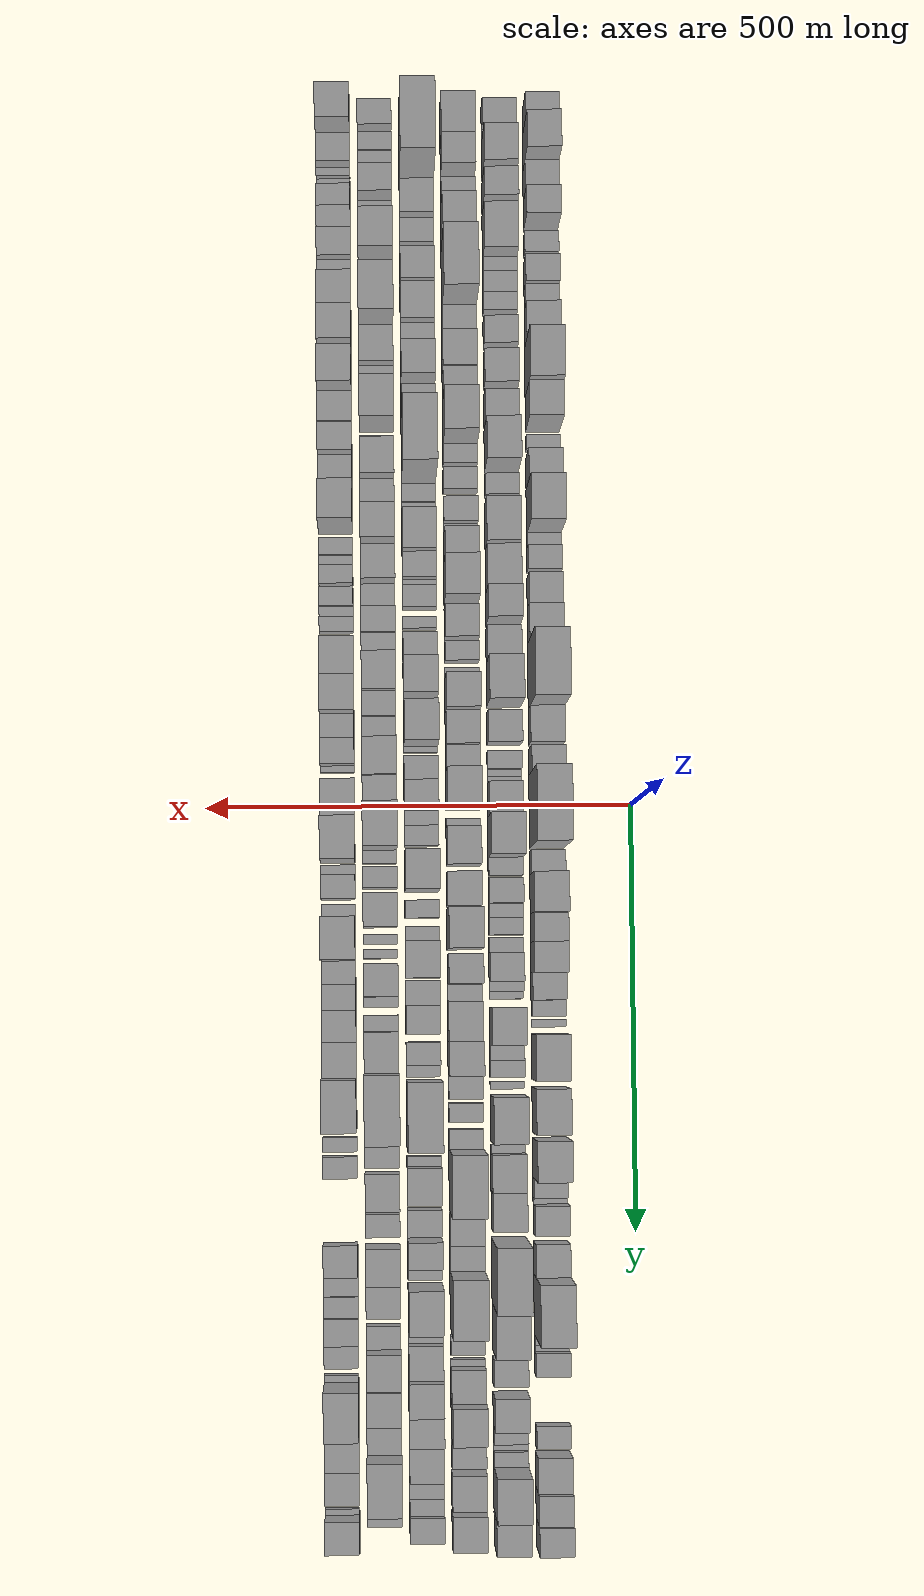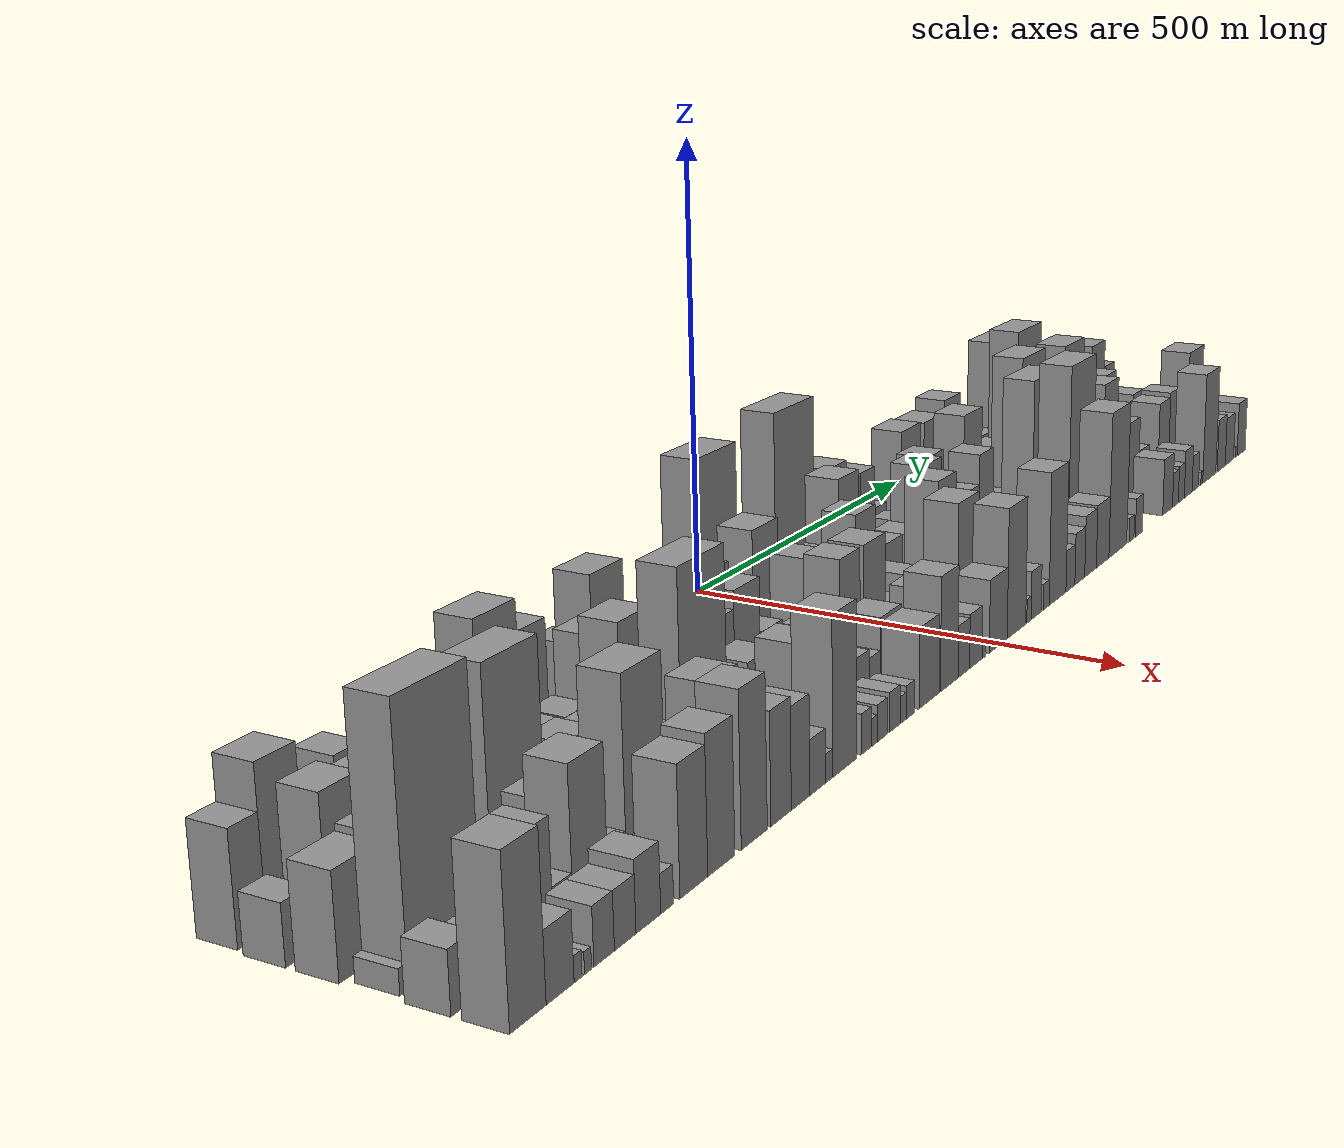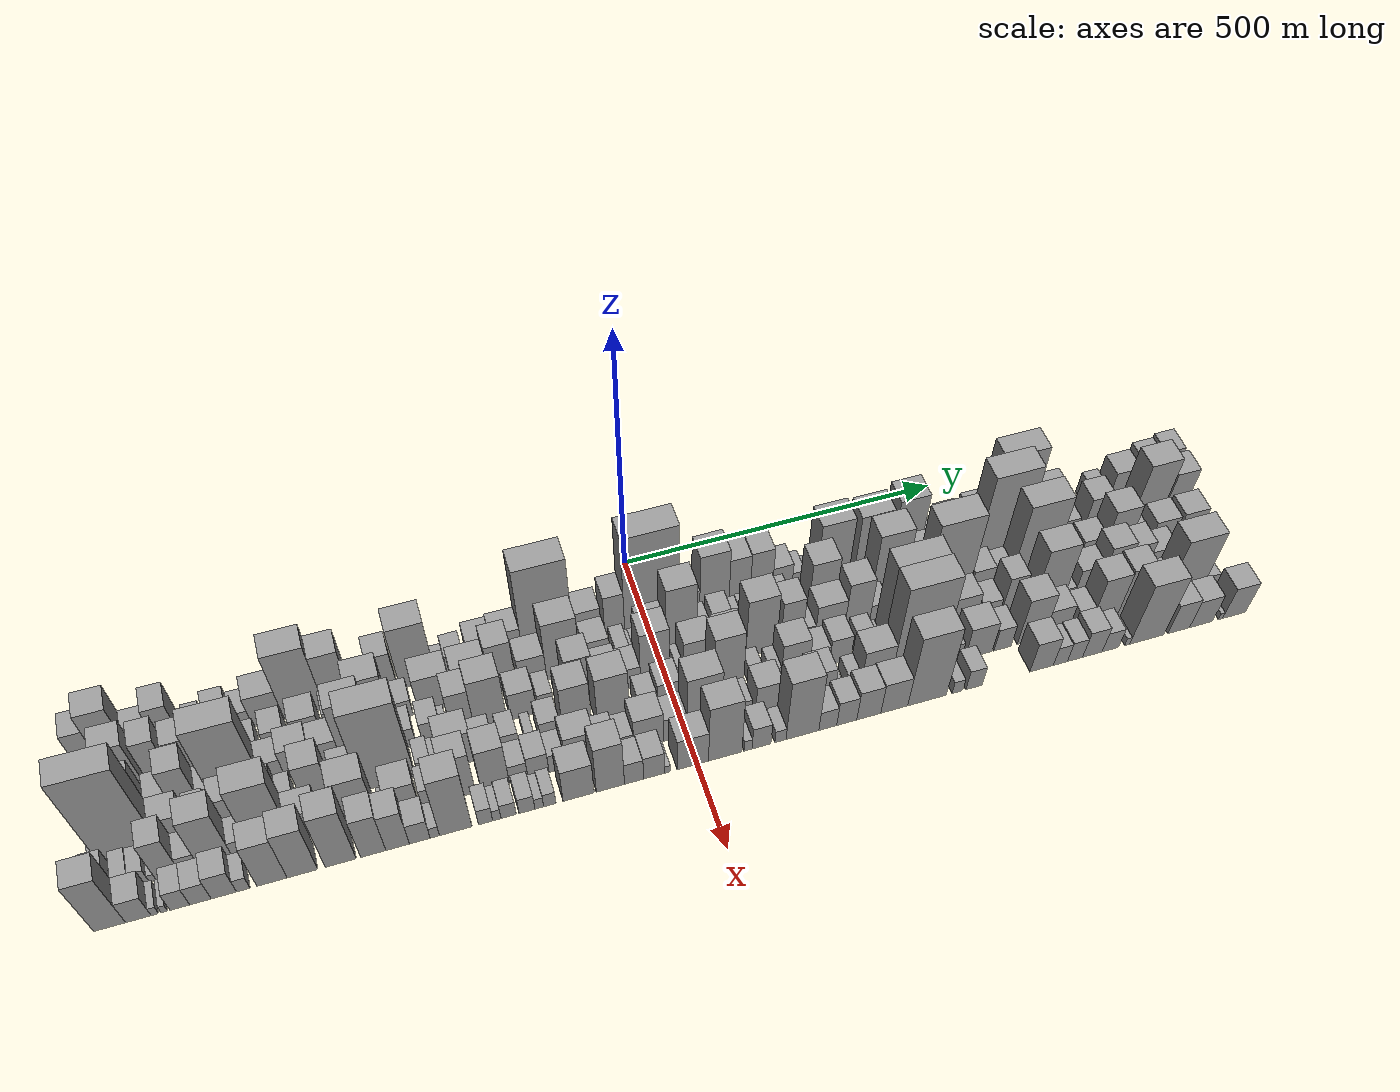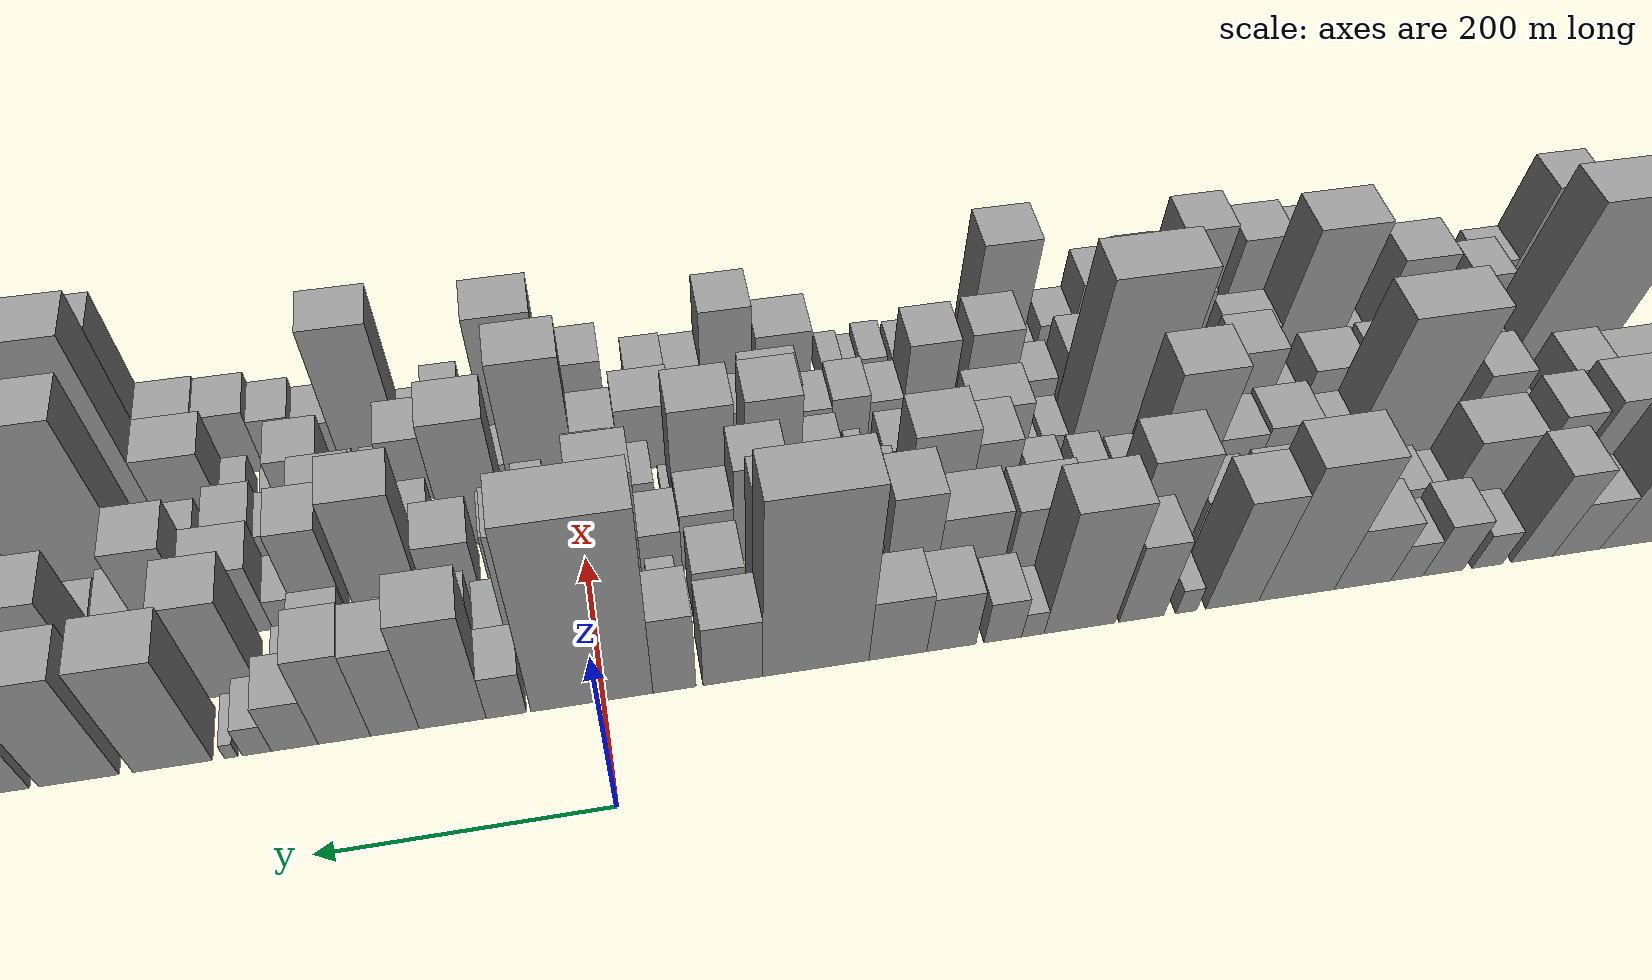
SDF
<sdf version="1.6">
 <world name="default">
  <scene>
   <sky><clouds><speed>12</speed></clouds></sky>
   <ambient>0.4 0.4 0.4 1</ambient>
   <background>0.7 0.7 0.7 1</background>
   <shadows>1</shadows>
  </scene>
  <gravity>0 0 -9.8066</gravity>
  <magnetic_field>6e-06 2.3e-05 -4.2e-05</magnetic_field>
  <physics default="0" name="default_physics" type="ode">
   <ode>
    <solver>
     <type>quick</type>
     <iters>10</iters>
     <sor>1.0</sor>
     <use_dynamic_moi_rescaling>0</use_dynamic_moi_rescaling>
    </solver>
    <constraints>
     <cfm>0</cfm>
     <erp>0.2</erp>
     <contact_max_correcting_vel>100</contact_max_correcting_vel>
     <contact_surface_layer>0.001</contact_surface_layer>
    </constraints>
   </ode>
   <max_step_size>0.004</max_step_size>
   <real_time_factor>1</real_time_factor>
   <real_time_update_rate>250</real_time_update_rate>
  </physics>
  <light name="sun" type="directional">
   <pose>0 0 10 0 0 0</pose>
   <diffuse>0.8 0.8 0.8 1</diffuse>
   <specular>0.2 0.2 0.2 1</specular>
   <attenuation>
    <range>1000</range>
    <constant>0.9</constant>
    <linear>0.01</linear>
    <quadratic>0.001</quadratic>
   </attenuation>
   <direction>-0.5 0.1 -0.9</direction>
  </light>
  <model name="building_1">
   <static>1</static>
   <pose>100.0000 -810.8486 0 0.000000 0.000000 0.000000</pose>
   <link name="link">
    <pose>0 0 48.00 0 0 0</pose>
    <collision name="collision"><geometry><box><size>40.0000 30.3027 96.0000</size></box></geometry></collision>
    <visual name="visual">
     <cast_shadows>0</cast_shadows>
     <geometry><box><size>40.0000 30.3027 96.0000</size></box></geometry>
     <material>
      <script>
       <uri>model://grey_wall/materials/scripts</uri>
       <uri>model://grey_wall/materials/textures</uri>
       <name>vrc/grey_wall</name>
      </script>
     </material>
    </visual>
   </link>
  </model>
  <model name="building_2">
   <static>1</static>
   <pose>100.0000 -774.1942 0 0.000000 0.000000 0.000000</pose>
   <link name="link">
    <pose>0 0 67.50 0 0 0</pose>
    <collision name="collision"><geometry><box><size>40.0000 43.0061 135.0000</size></box></geometry></collision>
    <visual name="visual">
     <cast_shadows>0</cast_shadows>
     <geometry><box><size>40.0000 43.0061 135.0000</size></box></geometry>
     <material>
      <script>
       <uri>model://grey_wall/materials/scripts</uri>
       <uri>model://grey_wall/materials/textures</uri>
       <name>vrc/grey_wall</name>
      </script>
     </material>
    </visual>
   </link>
  </model>
  <model name="building_3">
   <static>1</static>
   <pose>100.0000 -733.5180 0 0.000000 0.000000 0.000000</pose>
   <link name="link">
    <pose>0 0 33.00 0 0 0</pose>
    <collision name="collision"><geometry><box><size>40.0000 38.3464 66.0000</size></box></geometry></collision>
    <visual name="visual">
     <cast_shadows>0</cast_shadows>
     <geometry><box><size>40.0000 38.3464 66.0000</size></box></geometry>
     <material>
      <script>
       <uri>model://grey_wall/materials/scripts</uri>
       <uri>model://grey_wall/materials/textures</uri>
       <name>vrc/grey_wall</name>
      </script>
     </material>
    </visual>
   </link>
  </model>
  <model name="building_4">
   <static>1</static>
   <pose>100.0000 -697.7857 0 0.000000 0.000000 0.000000</pose>
   <link name="link">
    <pose>0 0 54.00 0 0 0</pose>
    <collision name="collision"><geometry><box><size>40.0000 33.1181 108.0000</size></box></geometry></collision>
    <visual name="visual">
     <cast_shadows>0</cast_shadows>
     <geometry><box><size>40.0000 33.1181 108.0000</size></box></geometry>
     <material>
      <script>
       <uri>model://grey_wall/materials/scripts</uri>
       <uri>model://grey_wall/materials/textures</uri>
       <name>vrc/grey_wall</name>
      </script>
     </material>
    </visual>
   </link>
  </model>
  <model name="building_5">
   <static>1</static>
   <pose>100.0000 -661.9748 0 0.000000 0.000000 0.000000</pose>
   <link name="link">
    <pose>0 0 21.00 0 0 0</pose>
    <collision name="collision"><geometry><box><size>40.0000 24.5038 42.0000</size></box></geometry></collision>
    <visual name="visual">
     <cast_shadows>0</cast_shadows>
     <geometry><box><size>40.0000 24.5038 42.0000</size></box></geometry>
     <material>
      <script>
       <uri>model://grey_wall/materials/scripts</uri>
       <uri>model://grey_wall/materials/textures</uri>
       <name>vrc/grey_wall</name>
      </script>
     </material>
    </visual>
   </link>
  </model>
  <model name="building_6">
   <static>1</static>
   <pose>100.0000 -626.8014 0 0.000000 0.000000 0.000000</pose>
   <link name="link">
    <pose>0 0 31.50 0 0 0</pose>
    <collision name="collision"><geometry><box><size>40.0000 31.8430 63.0000</size></box></geometry></collision>
    <visual name="visual">
     <cast_shadows>0</cast_shadows>
     <geometry><box><size>40.0000 31.8430 63.0000</size></box></geometry>
     <material>
      <script>
       <uri>model://grey_wall/materials/scripts</uri>
       <uri>model://grey_wall/materials/textures</uri>
       <name>vrc/grey_wall</name>
      </script>
     </material>
    </visual>
   </link>
  </model>
  <model name="building_7">
   <static>1</static>
   <pose>100.0000 -598.2045 0 0.000000 0.000000 0.000000</pose>
   <link name="link">
    <pose>0 0 22.50 0 0 0</pose>
    <collision name="collision"><geometry><box><size>40.0000 25.3507 45.0000</size></box></geometry></collision>
    <visual name="visual">
     <cast_shadows>0</cast_shadows>
     <geometry><box><size>40.0000 25.3507 45.0000</size></box></geometry>
     <material>
      <script>
       <uri>model://grey_wall/materials/scripts</uri>
       <uri>model://grey_wall/materials/textures</uri>
       <name>vrc/grey_wall</name>
      </script>
     </material>
    </visual>
   </link>
  </model>
  <model name="building_8">
   <static>1</static>
   <pose>100.0000 -563.3122 0 0.000000 0.000000 0.000000</pose>
   <link name="link">
    <pose>0 0 37.50 0 0 0</pose>
    <collision name="collision"><geometry><box><size>40.0000 44.4339 75.0000</size></box></geometry></collision>
    <visual name="visual">
     <cast_shadows>0</cast_shadows>
     <geometry><box><size>40.0000 44.4339 75.0000</size></box></geometry>
     <material>
      <script>
       <uri>model://grey_wall/materials/scripts</uri>
       <uri>model://grey_wall/materials/textures</uri>
       <name>vrc/grey_wall</name>
      </script>
     </material>
    </visual>
   </link>
  </model>
  <model name="building_9">
   <static>1</static>
   <pose>100.0000 -511.8582 0 0.000000 0.000000 0.000000</pose>
   <link name="link">
    <pose>0 0 81.00 0 0 0</pose>
    <collision name="collision"><geometry><box><size>40.0000 58.4741 162.0000</size></box></geometry></collision>
    <visual name="visual">
     <cast_shadows>0</cast_shadows>
     <geometry><box><size>40.0000 58.4741 162.0000</size></box></geometry>
     <material>
      <script>
       <uri>model://grey_wall/materials/scripts</uri>
       <uri>model://grey_wall/materials/textures</uri>
       <name>vrc/grey_wall</name>
      </script>
     </material>
    </visual>
   </link>
  </model>
  <model name="building_10">
   <static>1</static>
   <pose>100.0000 -462.2591 0 0.000000 0.000000 0.000000</pose>
   <link name="link">
    <pose>0 0 66.00 0 0 0</pose>
    <collision name="collision"><geometry><box><size>40.0000 40.7242 132.0000</size></box></geometry></collision>
    <visual name="visual">
     <cast_shadows>0</cast_shadows>
     <geometry><box><size>40.0000 40.7242 132.0000</size></box></geometry>
     <material>
      <script>
       <uri>model://grey_wall/materials/scripts</uri>
       <uri>model://grey_wall/materials/textures</uri>
       <name>vrc/grey_wall</name>
      </script>
     </material>
    </visual>
   </link>
  </model>
  <model name="building_11">
   <static>1</static>
   <pose>100.0000 -426.9195 0 0.000000 0.000000 0.000000</pose>
   <link name="link">
    <pose>0 0 15.00 0 0 0</pose>
    <collision name="collision"><geometry><box><size>40.0000 15.9549 30.0000</size></box></geometry></collision>
    <visual name="visual">
     <cast_shadows>0</cast_shadows>
     <geometry><box><size>40.0000 15.9549 30.0000</size></box></geometry>
     <material>
      <script>
       <uri>model://grey_wall/materials/scripts</uri>
       <uri>model://grey_wall/materials/textures</uri>
       <name>vrc/grey_wall</name>
      </script>
     </material>
    </visual>
   </link>
  </model>
  <model name="building_12">
   <static>1</static>
   <pose>100.0000 -392.8973 0 0.000000 0.000000 0.000000</pose>
   <link name="link">
    <pose>0 0 48.00 0 0 0</pose>
    <collision name="collision"><geometry><box><size>40.0000 34.0896 96.0000</size></box></geometry></collision>
    <visual name="visual">
     <cast_shadows>0</cast_shadows>
     <geometry><box><size>40.0000 34.0896 96.0000</size></box></geometry>
     <material>
      <script>
       <uri>model://grey_wall/materials/scripts</uri>
       <uri>model://grey_wall/materials/textures</uri>
       <name>vrc/grey_wall</name>
      </script>
     </material>
    </visual>
   </link>
  </model>
  <model name="building_13">
   <static>1</static>
   <pose>100.0000 -346.2073 0 0.000000 0.000000 0.000000</pose>
   <link name="link">
    <pose>0 0 75.00 0 0 0</pose>
    <collision name="collision"><geometry><box><size>40.0000 53.2903 150.0000</size></box></geometry></collision>
    <visual name="visual">
     <cast_shadows>0</cast_shadows>
     <geometry><box><size>40.0000 53.2903 150.0000</size></box></geometry>
     <material>
      <script>
       <uri>model://grey_wall/materials/scripts</uri>
       <uri>model://grey_wall/materials/textures</uri>
       <name>vrc/grey_wall</name>
      </script>
     </material>
    </visual>
   </link>
  </model>
  <model name="building_14">
   <static>1</static>
   <pose>100.0000 -311.1829 0 0.000000 0.000000 0.000000</pose>
   <link name="link">
    <pose>0 0 15.00 0 0 0</pose>
    <collision name="collision"><geometry><box><size>40.0000 16.7586 30.0000</size></box></geometry></collision>
    <visual name="visual">
     <cast_shadows>0</cast_shadows>
     <geometry><box><size>40.0000 16.7586 30.0000</size></box></geometry>
     <material>
      <script>
       <uri>model://grey_wall/materials/scripts</uri>
       <uri>model://grey_wall/materials/textures</uri>
       <name>vrc/grey_wall</name>
      </script>
     </material>
    </visual>
   </link>
  </model>
  <model name="building_15">
   <static>1</static>
   <pose>100.0000 -288.7752 0 0.000000 0.000000 0.000000</pose>
   <link name="link">
    <pose>0 0 25.50 0 0 0</pose>
    <collision name="collision"><geometry><box><size>40.0000 28.0567 51.0000</size></box></geometry></collision>
    <visual name="visual">
     <cast_shadows>0</cast_shadows>
     <geometry><box><size>40.0000 28.0567 51.0000</size></box></geometry>
     <material>
      <script>
       <uri>model://grey_wall/materials/scripts</uri>
       <uri>model://grey_wall/materials/textures</uri>
       <name>vrc/grey_wall</name>
      </script>
     </material>
    </visual>
   </link>
  </model>
  <model name="building_16">
   <static>1</static>
   <pose>100.0000 -250.5899 0 0.000000 0.000000 0.000000</pose>
   <link name="link">
    <pose>0 0 34.50 0 0 0</pose>
    <collision name="collision"><geometry><box><size>40.0000 36.3140 69.0000</size></box></geometry></collision>
    <visual name="visual">
     <cast_shadows>0</cast_shadows>
     <geometry><box><size>40.0000 36.3140 69.0000</size></box></geometry>
     <material>
      <script>
       <uri>model://grey_wall/materials/scripts</uri>
       <uri>model://grey_wall/materials/textures</uri>
       <name>vrc/grey_wall</name>
      </script>
     </material>
    </visual>
   </link>
  </model>
  <model name="building_17">
   <static>1</static>
   <pose>100.0000 -211.2901 0 0.000000 0.000000 0.000000</pose>
   <link name="link">
    <pose>0 0 37.50 0 0 0</pose>
    <collision name="collision"><geometry><box><size>40.0000 42.2855 75.0000</size></box></geometry></collision>
    <visual name="visual">
     <cast_shadows>0</cast_shadows>
     <geometry><box><size>40.0000 42.2855 75.0000</size></box></geometry>
     <material>
      <script>
       <uri>model://grey_wall/materials/scripts</uri>
       <uri>model://grey_wall/materials/textures</uri>
       <name>vrc/grey_wall</name>
      </script>
     </material>
    </visual>
   </link>
  </model>
  <model name="building_18">
   <static>1</static>
   <pose>100.0000 -151.5598 0 0.000000 0.000000 0.000000</pose>
   <link name="link">
    <pose>0 0 106.50 0 0 0</pose>
    <collision name="collision"><geometry><box><size>40.0000 77.1752 213.0000</size></box></geometry></collision>
    <visual name="visual">
     <cast_shadows>0</cast_shadows>
     <geometry><box><size>40.0000 77.1752 213.0000</size></box></geometry>
     <material>
      <script>
       <uri>model://grey_wall/materials/scripts</uri>
       <uri>model://grey_wall/materials/textures</uri>
       <name>vrc/grey_wall</name>
      </script>
     </material>
    </visual>
   </link>
  </model>
  <model name="building_19">
   <static>1</static>
   <pose>100.0000 -91.7813 0 0.000000 0.000000 0.000000</pose>
   <link name="link">
    <pose>0 0 37.50 0 0 0</pose>
    <collision name="collision"><geometry><box><size>40.0000 42.3817 75.0000</size></box></geometry></collision>
    <visual name="visual">
     <cast_shadows>0</cast_shadows>
     <geometry><box><size>40.0000 42.3817 75.0000</size></box></geometry>
     <material>
      <script>
       <uri>model://grey_wall/materials/scripts</uri>
       <uri>model://grey_wall/materials/textures</uri>
       <name>vrc/grey_wall</name>
      </script>
     </material>
    </visual>
   </link>
  </model>
  <model name="building_20">
   <static>1</static>
   <pose>100.0000 -50.3472 0 0.000000 0.000000 0.000000</pose>
   <link name="link">
    <pose>0 0 48.00 0 0 0</pose>
    <collision name="collision"><geometry><box><size>40.0000 30.4866 96.0000</size></box></geometry></collision>
    <visual name="visual">
     <cast_shadows>0</cast_shadows>
     <geometry><box><size>40.0000 30.4866 96.0000</size></box></geometry>
     <material>
      <script>
       <uri>model://grey_wall/materials/scripts</uri>
       <uri>model://grey_wall/materials/textures</uri>
       <name>vrc/grey_wall</name>
      </script>
     </material>
    </visual>
   </link>
  </model>
  <model name="building_21">
   <static>1</static>
   <pose>100.0000 7.7180 0 0.000000 0.000000 0.000000</pose>
   <link name="link">
    <pose>0 0 112.50 0 0 0</pose>
    <collision name="collision"><geometry><box><size>40.0000 85.6436 225.0000</size></box></geometry></collision>
    <visual name="visual">
     <cast_shadows>0</cast_shadows>
     <geometry><box><size>40.0000 85.6436 225.0000</size></box></geometry>
     <material>
      <script>
       <uri>model://grey_wall/materials/scripts</uri>
       <uri>model://grey_wall/materials/textures</uri>
       <name>vrc/grey_wall</name>
      </script>
     </material>
    </visual>
   </link>
  </model>
  <model name="building_22">
   <static>1</static>
   <pose>100.0000 67.5564 0 0.000000 0.000000 0.000000</pose>
   <link name="link">
    <pose>0 0 27.00 0 0 0</pose>
    <collision name="collision"><geometry><box><size>40.0000 28.0332 54.0000</size></box></geometry></collision>
    <visual name="visual">
     <cast_shadows>0</cast_shadows>
     <geometry><box><size>40.0000 28.0332 54.0000</size></box></geometry>
     <material>
      <script>
       <uri>model://grey_wall/materials/scripts</uri>
       <uri>model://grey_wall/materials/textures</uri>
       <name>vrc/grey_wall</name>
      </script>
     </material>
    </visual>
   </link>
  </model>
  <model name="building_23">
   <static>1</static>
   <pose>100.0000 104.6432 0 0.000000 0.000000 0.000000</pose>
   <link name="link">
    <pose>0 0 67.50 0 0 0</pose>
    <collision name="collision"><geometry><box><size>40.0000 46.1405 135.0000</size></box></geometry></collision>
    <visual name="visual">
     <cast_shadows>0</cast_shadows>
     <geometry><box><size>40.0000 46.1405 135.0000</size></box></geometry>
     <material>
      <script>
       <uri>model://grey_wall/materials/scripts</uri>
       <uri>model://grey_wall/materials/textures</uri>
       <name>vrc/grey_wall</name>
      </script>
     </material>
    </visual>
   </link>
  </model>
  <model name="building_24">
   <static>1</static>
   <pose>100.0000 144.3165 0 0.000000 0.000000 0.000000</pose>
   <link name="link">
    <pose>0 0 54.00 0 0 0</pose>
    <collision name="collision"><geometry><box><size>40.0000 33.2061 108.0000</size></box></geometry></collision>
    <visual name="visual">
     <cast_shadows>0</cast_shadows>
     <geometry><box><size>40.0000 33.2061 108.0000</size></box></geometry>
     <material>
      <script>
       <uri>model://grey_wall/materials/scripts</uri>
       <uri>model://grey_wall/materials/textures</uri>
       <name>vrc/grey_wall</name>
      </script>
     </material>
    </visual>
   </link>
  </model>
  <model name="building_25">
   <static>1</static>
   <pose>100.0000 178.6561 0 0.000000 0.000000 0.000000</pose>
   <link name="link">
    <pose>0 0 55.50 0 0 0</pose>
    <collision name="collision"><geometry><box><size>40.0000 35.4731 111.0000</size></box></geometry></collision>
    <visual name="visual">
     <cast_shadows>0</cast_shadows>
     <geometry><box><size>40.0000 35.4731 111.0000</size></box></geometry>
     <material>
      <script>
       <uri>model://grey_wall/materials/scripts</uri>
       <uri>model://grey_wall/materials/textures</uri>
       <name>vrc/grey_wall</name>
      </script>
     </material>
    </visual>
   </link>
  </model>
  <model name="building_26">
   <static>1</static>
   <pose>100.0000 212.2045 0 0.000000 0.000000 0.000000</pose>
   <link name="link">
    <pose>0 0 30.00 0 0 0</pose>
    <collision name="collision"><geometry><box><size>40.0000 31.6237 60.0000</size></box></geometry></collision>
    <visual name="visual">
     <cast_shadows>0</cast_shadows>
     <geometry><box><size>40.0000 31.6237 60.0000</size></box></geometry>
     <material>
      <script>
       <uri>model://grey_wall/materials/scripts</uri>
       <uri>model://grey_wall/materials/textures</uri>
       <name>vrc/grey_wall</name>
      </script>
     </material>
    </visual>
   </link>
  </model>
  <model name="building_27">
   <static>1</static>
   <pose>100.0000 237.7429 0 0.000000 0.000000 0.000000</pose>
   <link name="link">
    <pose>0 0 18.00 0 0 0</pose>
    <collision name="collision"><geometry><box><size>40.0000 19.4531 36.0000</size></box></geometry></collision>
    <visual name="visual">
     <cast_shadows>0</cast_shadows>
     <geometry><box><size>40.0000 19.4531 36.0000</size></box></geometry>
     <material>
      <script>
       <uri>model://grey_wall/materials/scripts</uri>
       <uri>model://grey_wall/materials/textures</uri>
       <name>vrc/grey_wall</name>
      </script>
     </material>
    </visual>
   </link>
  </model>
  <model name="building_28">
   <static>1</static>
   <pose>100.0000 254.9642 0 0.000000 0.000000 0.000000</pose>
   <link name="link">
    <pose>0 0 9.00 0 0 0</pose>
    <collision name="collision"><geometry><box><size>40.0000 8.9894 18.0000</size></box></geometry></collision>
    <visual name="visual">
     <cast_shadows>0</cast_shadows>
     <geometry><box><size>40.0000 8.9894 18.0000</size></box></geometry>
     <material>
      <script>
       <uri>model://grey_wall/materials/scripts</uri>
       <uri>model://grey_wall/materials/textures</uri>
       <name>vrc/grey_wall</name>
      </script>
     </material>
    </visual>
   </link>
  </model>
  <model name="building_29">
   <static>1</static>
   <pose>100.0000 293.9010 0 0.000000 0.000000 0.000000</pose>
   <link name="link">
    <pose>0 0 67.50 0 0 0</pose>
    <collision name="collision"><geometry><box><size>40.0000 52.8842 135.0000</size></box></geometry></collision>
    <visual name="visual">
     <cast_shadows>0</cast_shadows>
     <geometry><box><size>40.0000 52.8842 135.0000</size></box></geometry>
     <material>
      <script>
       <uri>model://grey_wall/materials/scripts</uri>
       <uri>model://grey_wall/materials/textures</uri>
       <name>vrc/grey_wall</name>
      </script>
     </material>
    </visual>
   </link>
  </model>
  <model name="building_30">
   <static>1</static>
   <pose>100.0000 355.6914 0 0.000000 0.000000 0.000000</pose>
   <link name="link">
    <pose>0 0 66.00 0 0 0</pose>
    <collision name="collision"><geometry><box><size>40.0000 52.6967 132.0000</size></box></geometry></collision>
    <visual name="visual">
     <cast_shadows>0</cast_shadows>
     <geometry><box><size>40.0000 52.6967 132.0000</size></box></geometry>
     <material>
      <script>
       <uri>model://grey_wall/materials/scripts</uri>
       <uri>model://grey_wall/materials/textures</uri>
       <name>vrc/grey_wall</name>
      </script>
     </material>
    </visual>
   </link>
  </model>
  <model name="building_31">
   <static>1</static>
   <pose>100.0000 411.5241 0 0.000000 0.000000 0.000000</pose>
   <link name="link">
    <pose>0 0 73.50 0 0 0</pose>
    <collision name="collision"><geometry><box><size>40.0000 46.9688 147.0000</size></box></geometry></collision>
    <visual name="visual">
     <cast_shadows>0</cast_shadows>
     <geometry><box><size>40.0000 46.9688 147.0000</size></box></geometry>
     <material>
      <script>
       <uri>model://grey_wall/materials/scripts</uri>
       <uri>model://grey_wall/materials/textures</uri>
       <name>vrc/grey_wall</name>
      </script>
     </material>
    </visual>
   </link>
  </model>
  <model name="building_32">
   <static>1</static>
   <pose>100.0000 446.6023 0 0.000000 0.000000 0.000000</pose>
   <link name="link">
    <pose>0 0 19.50 0 0 0</pose>
    <collision name="collision"><geometry><box><size>40.0000 23.1874 39.0000</size></box></geometry></collision>
    <visual name="visual">
     <cast_shadows>0</cast_shadows>
     <geometry><box><size>40.0000 23.1874 39.0000</size></box></geometry>
     <material>
      <script>
       <uri>model://grey_wall/materials/scripts</uri>
       <uri>model://grey_wall/materials/textures</uri>
       <name>vrc/grey_wall</name>
      </script>
     </material>
    </visual>
   </link>
  </model>
  <model name="building_33">
   <static>1</static>
   <pose>100.0000 461.7570 0 0.000000 0.000000 0.000000</pose>
   <link name="link">
    <pose>0 0 7.50 0 0 0</pose>
    <collision name="collision"><geometry><box><size>40.0000 7.1221 15.0000</size></box></geometry></collision>
    <visual name="visual">
     <cast_shadows>0</cast_shadows>
     <geometry><box><size>40.0000 7.1221 15.0000</size></box></geometry>
     <material>
      <script>
       <uri>model://grey_wall/materials/scripts</uri>
       <uri>model://grey_wall/materials/textures</uri>
       <name>vrc/grey_wall</name>
      </script>
     </material>
    </visual>
   </link>
  </model>
  <model name="building_34">
   <static>1</static>
   <pose>100.0000 482.5764 0 0.000000 0.000000 0.000000</pose>
   <link name="link">
    <pose>0 0 33.00 0 0 0</pose>
    <collision name="collision"><geometry><box><size>40.0000 34.5167 66.0000</size></box></geometry></collision>
    <visual name="visual">
     <cast_shadows>0</cast_shadows>
     <geometry><box><size>40.0000 34.5167 66.0000</size></box></geometry>
     <material>
      <script>
       <uri>model://grey_wall/materials/scripts</uri>
       <uri>model://grey_wall/materials/textures</uri>
       <name>vrc/grey_wall</name>
      </script>
     </material>
    </visual>
   </link>
  </model>
  <model name="building_35">
   <static>1</static>
   <pose>100.0000 527.8713 0 0.000000 0.000000 0.000000</pose>
   <link name="link">
    <pose>0 0 37.50 0 0 0</pose>
    <collision name="collision"><geometry><box><size>40.0000 38.0731 75.0000</size></box></geometry></collision>
    <visual name="visual">
     <cast_shadows>0</cast_shadows>
     <geometry><box><size>40.0000 38.0731 75.0000</size></box></geometry>
     <material>
      <script>
       <uri>model://grey_wall/materials/scripts</uri>
       <uri>model://grey_wall/materials/textures</uri>
       <name>vrc/grey_wall</name>
      </script>
     </material>
    </visual>
   </link>
  </model>
  <model name="building_36">
   <static>1</static>
   <pose>100.0000 582.0169 0 0.000000 0.000000 0.000000</pose>
   <link name="link">
    <pose>0 0 94.50 0 0 0</pose>
    <collision name="collision"><geometry><box><size>40.0000 70.2179 189.0000</size></box></geometry></collision>
    <visual name="visual">
     <cast_shadows>0</cast_shadows>
     <geometry><box><size>40.0000 70.2179 189.0000</size></box></geometry>
     <material>
      <script>
       <uri>model://grey_wall/materials/scripts</uri>
       <uri>model://grey_wall/materials/textures</uri>
       <name>vrc/grey_wall</name>
      </script>
     </material>
    </visual>
   </link>
  </model>
  <model name="building_37">
   <static>1</static>
   <pose>100.0000 622.5473 0 0.000000 0.000000 0.000000</pose>
   <link name="link">
    <pose>0 0 13.50 0 0 0</pose>
    <collision name="collision"><geometry><box><size>40.0000 10.8430 27.0000</size></box></geometry></collision>
    <visual name="visual">
     <cast_shadows>0</cast_shadows>
     <geometry><box><size>40.0000 10.8430 27.0000</size></box></geometry>
     <material>
      <script>
       <uri>model://grey_wall/materials/scripts</uri>
       <uri>model://grey_wall/materials/textures</uri>
       <name>vrc/grey_wall</name>
      </script>
     </material>
    </visual>
   </link>
  </model>
  <model name="building_38">
   <static>1</static>
   <pose>100.0000 631.7565 0 0.000000 0.000000 0.000000</pose>
   <link name="link">
    <pose>0 0 9.00 0 0 0</pose>
    <collision name="collision"><geometry><box><size>40.0000 7.5754 18.0000</size></box></geometry></collision>
    <visual name="visual">
     <cast_shadows>0</cast_shadows>
     <geometry><box><size>40.0000 7.5754 18.0000</size></box></geometry>
     <material>
      <script>
       <uri>model://grey_wall/materials/scripts</uri>
       <uri>model://grey_wall/materials/textures</uri>
       <name>vrc/grey_wall</name>
      </script>
     </material>
    </visual>
   </link>
  </model>
  <model name="building_39">
   <static>1</static>
   <pose>100.0000 648.9793 0 0.000000 0.000000 0.000000</pose>
   <link name="link">
    <pose>0 0 25.50 0 0 0</pose>
    <collision name="collision"><geometry><box><size>40.0000 26.8701 51.0000</size></box></geometry></collision>
    <visual name="visual">
     <cast_shadows>0</cast_shadows>
     <geometry><box><size>40.0000 26.8701 51.0000</size></box></geometry>
     <material>
      <script>
       <uri>model://grey_wall/materials/scripts</uri>
       <uri>model://grey_wall/materials/textures</uri>
       <name>vrc/grey_wall</name>
      </script>
     </material>
    </visual>
   </link>
  </model>
  <model name="building_40">
   <static>1</static>
   <pose>100.0000 732.4830 0 0.000000 0.000000 0.000000</pose>
   <link name="link">
    <pose>0 0 24.00 0 0 0</pose>
    <collision name="collision"><geometry><box><size>40.0000 26.0458 48.0000</size></box></geometry></collision>
    <visual name="visual">
     <cast_shadows>0</cast_shadows>
     <geometry><box><size>40.0000 26.0458 48.0000</size></box></geometry>
     <material>
      <script>
       <uri>model://grey_wall/materials/scripts</uri>
       <uri>model://grey_wall/materials/textures</uri>
       <name>vrc/grey_wall</name>
      </script>
     </material>
    </visual>
   </link>
  </model>
  <model name="building_41">
   <static>1</static>
   <pose>100.0000 772.8730 0 0.000000 0.000000 0.000000</pose>
   <link name="link">
    <pose>0 0 39.00 0 0 0</pose>
    <collision name="collision"><geometry><box><size>40.0000 40.7342 78.0000</size></box></geometry></collision>
    <visual name="visual">
     <cast_shadows>0</cast_shadows>
     <geometry><box><size>40.0000 40.7342 78.0000</size></box></geometry>
     <material>
      <script>
       <uri>model://grey_wall/materials/scripts</uri>
       <uri>model://grey_wall/materials/textures</uri>
       <name>vrc/grey_wall</name>
      </script>
     </material>
    </visual>
   </link>
  </model>
  <model name="building_42">
   <static>1</static>
   <pose>100.0000 810.9288 0 0.000000 0.000000 0.000000</pose>
   <link name="link">
    <pose>0 0 46.50 0 0 0</pose>
    <collision name="collision"><geometry><box><size>40.0000 35.3773 93.0000</size></box></geometry></collision>
    <visual name="visual">
     <cast_shadows>0</cast_shadows>
     <geometry><box><size>40.0000 35.3773 93.0000</size></box></geometry>
     <material>
      <script>
       <uri>model://grey_wall/materials/scripts</uri>
       <uri>model://grey_wall/materials/textures</uri>
       <name>vrc/grey_wall</name>
      </script>
     </material>
    </visual>
   </link>
  </model>
  <model name="building_43">
   <static>1</static>
   <pose>100.0000 845.0833 0 0.000000 0.000000 0.000000</pose>
   <link name="link">
    <pose>0 0 51.00 0 0 0</pose>
    <collision name="collision"><geometry><box><size>40.0000 32.9317 102.0000</size></box></geometry></collision>
    <visual name="visual">
     <cast_shadows>0</cast_shadows>
     <geometry><box><size>40.0000 32.9317 102.0000</size></box></geometry>
     <material>
      <script>
       <uri>model://grey_wall/materials/scripts</uri>
       <uri>model://grey_wall/materials/textures</uri>
       <name>vrc/grey_wall</name>
      </script>
     </material>
    </visual>
   </link>
  </model>
  <model name="building_44">
   <static>1</static>
   <pose>149.0000 -815.3887 0 0.000000 0.000000 0.000000</pose>
   <link name="link">
    <pose>0 0 25.50 0 0 0</pose>
    <collision name="collision"><geometry><box><size>40.0000 29.2225 51.0000</size></box></geometry></collision>
    <visual name="visual">
     <cast_shadows>0</cast_shadows>
     <geometry><box><size>40.0000 29.2225 51.0000</size></box></geometry>
     <material>
      <script>
       <uri>model://grey_wall/materials/scripts</uri>
       <uri>model://grey_wall/materials/textures</uri>
       <name>vrc/grey_wall</name>
      </script>
     </material>
    </visual>
   </link>
  </model>
  <model name="building_45">
   <static>1</static>
   <pose>149.0000 -796.7744 0 0.000000 0.000000 0.000000</pose>
   <link name="link">
    <pose>0 0 9.00 0 0 0</pose>
    <collision name="collision"><geometry><box><size>40.0000 8.0061 18.0000</size></box></geometry></collision>
    <visual name="visual">
     <cast_shadows>0</cast_shadows>
     <geometry><box><size>40.0000 8.0061 18.0000</size></box></geometry>
     <material>
      <script>
       <uri>model://grey_wall/materials/scripts</uri>
       <uri>model://grey_wall/materials/textures</uri>
       <name>vrc/grey_wall</name>
      </script>
     </material>
    </visual>
   </link>
  </model>
  <model name="building_46">
   <static>1</static>
   <pose>149.0000 -763.4466 0 0.000000 0.000000 0.000000</pose>
   <link name="link">
    <pose>0 0 58.50 0 0 0</pose>
    <collision name="collision"><geometry><box><size>40.0000 42.6495 117.0000</size></box></geometry></collision>
    <visual name="visual">
     <cast_shadows>0</cast_shadows>
     <geometry><box><size>40.0000 42.6495 117.0000</size></box></geometry>
     <material>
      <script>
       <uri>model://grey_wall/materials/scripts</uri>
       <uri>model://grey_wall/materials/textures</uri>
       <name>vrc/grey_wall</name>
      </script>
     </material>
    </visual>
   </link>
  </model>
  <model name="building_47">
   <static>1</static>
   <pose>149.0000 -719.6608 0 0.000000 0.000000 0.000000</pose>
   <link name="link">
    <pose>0 0 54.00 0 0 0</pose>
    <collision name="collision"><geometry><box><size>40.0000 32.9222 108.0000</size></box></geometry></collision>
    <visual name="visual">
     <cast_shadows>0</cast_shadows>
     <geometry><box><size>40.0000 32.9222 108.0000</size></box></geometry>
     <material>
      <script>
       <uri>model://grey_wall/materials/scripts</uri>
       <uri>model://grey_wall/materials/textures</uri>
       <name>vrc/grey_wall</name>
      </script>
     </material>
    </visual>
   </link>
  </model>
  <model name="building_48">
   <static>1</static>
   <pose>149.0000 -672.5919 0 0.000000 0.000000 0.000000</pose>
   <link name="link">
    <pose>0 0 45.00 0 0 0</pose>
    <collision name="collision"><geometry><box><size>40.0000 53.2155 90.0000</size></box></geometry></collision>
    <visual name="visual">
     <cast_shadows>0</cast_shadows>
     <geometry><box><size>40.0000 53.2155 90.0000</size></box></geometry>
     <material>
      <script>
       <uri>model://grey_wall/materials/scripts</uri>
       <uri>model://grey_wall/materials/textures</uri>
       <name>vrc/grey_wall</name>
      </script>
     </material>
    </visual>
   </link>
  </model>
  <model name="building_49">
   <static>1</static>
   <pose>149.0000 -636.8021 0 0.000000 0.000000 0.000000</pose>
   <link name="link">
    <pose>0 0 16.50 0 0 0</pose>
    <collision name="collision"><geometry><box><size>40.0000 18.3640 33.0000</size></box></geometry></collision>
    <visual name="visual">
     <cast_shadows>0</cast_shadows>
     <geometry><box><size>40.0000 18.3640 33.0000</size></box></geometry>
     <material>
      <script>
       <uri>model://grey_wall/materials/scripts</uri>
       <uri>model://grey_wall/materials/textures</uri>
       <name>vrc/grey_wall</name>
      </script>
     </material>
    </visual>
   </link>
  </model>
  <model name="building_50">
   <static>1</static>
   <pose>149.0000 -615.2574 0 0.000000 0.000000 0.000000</pose>
   <link name="link">
    <pose>0 0 21.00 0 0 0</pose>
    <collision name="collision"><geometry><box><size>40.0000 24.7254 42.0000</size></box></geometry></collision>
    <visual name="visual">
     <cast_shadows>0</cast_shadows>
     <geometry><box><size>40.0000 24.7254 42.0000</size></box></geometry>
     <material>
      <script>
       <uri>model://grey_wall/materials/scripts</uri>
       <uri>model://grey_wall/materials/textures</uri>
       <name>vrc/grey_wall</name>
      </script>
     </material>
    </visual>
   </link>
  </model>
  <model name="building_51">
   <static>1</static>
   <pose>149.0000 -592.1713 0 0.000000 0.000000 0.000000</pose>
   <link name="link">
    <pose>0 0 19.50 0 0 0</pose>
    <collision name="collision"><geometry><box><size>40.0000 21.4468 39.0000</size></box></geometry></collision>
    <visual name="visual">
     <cast_shadows>0</cast_shadows>
     <geometry><box><size>40.0000 21.4468 39.0000</size></box></geometry>
     <material>
      <script>
       <uri>model://grey_wall/materials/scripts</uri>
       <uri>model://grey_wall/materials/textures</uri>
       <name>vrc/grey_wall</name>
      </script>
     </material>
    </visual>
   </link>
  </model>
  <model name="building_52">
   <static>1</static>
   <pose>149.0000 -556.4604 0 0.000000 0.000000 0.000000</pose>
   <link name="link">
    <pose>0 0 27.00 0 0 0</pose>
    <collision name="collision"><geometry><box><size>40.0000 31.9750 54.0000</size></box></geometry></collision>
    <visual name="visual">
     <cast_shadows>0</cast_shadows>
     <geometry><box><size>40.0000 31.9750 54.0000</size></box></geometry>
     <material>
      <script>
       <uri>model://grey_wall/materials/scripts</uri>
       <uri>model://grey_wall/materials/textures</uri>
       <name>vrc/grey_wall</name>
      </script>
     </material>
    </visual>
   </link>
  </model>
  <model name="building_53">
   <static>1</static>
   <pose>149.0000 -512.0067 0 0.000000 0.000000 0.000000</pose>
   <link name="link">
    <pose>0 0 33.00 0 0 0</pose>
    <collision name="collision"><geometry><box><size>40.0000 38.9326 66.0000</size></box></geometry></collision>
    <visual name="visual">
     <cast_shadows>0</cast_shadows>
     <geometry><box><size>40.0000 38.9326 66.0000</size></box></geometry>
     <material>
      <script>
       <uri>model://grey_wall/materials/scripts</uri>
       <uri>model://grey_wall/materials/textures</uri>
       <name>vrc/grey_wall</name>
      </script>
     </material>
    </visual>
   </link>
  </model>
  <model name="building_54">
   <static>1</static>
   <pose>149.0000 -465.9677 0 0.000000 0.000000 0.000000</pose>
   <link name="link">
    <pose>0 0 31.50 0 0 0</pose>
    <collision name="collision"><geometry><box><size>40.0000 37.1453 63.0000</size></box></geometry></collision>
    <visual name="visual">
     <cast_shadows>0</cast_shadows>
     <geometry><box><size>40.0000 37.1453 63.0000</size></box></geometry>
     <material>
      <script>
       <uri>model://grey_wall/materials/scripts</uri>
       <uri>model://grey_wall/materials/textures</uri>
       <name>vrc/grey_wall</name>
      </script>
     </material>
    </visual>
   </link>
  </model>
  <model name="building_55">
   <static>1</static>
   <pose>149.0000 -418.8858 0 0.000000 0.000000 0.000000</pose>
   <link name="link">
    <pose>0 0 61.50 0 0 0</pose>
    <collision name="collision"><geometry><box><size>40.0000 49.0186 123.0000</size></box></geometry></collision>
    <visual name="visual">
     <cast_shadows>0</cast_shadows>
     <geometry><box><size>40.0000 49.0186 123.0000</size></box></geometry>
     <material>
      <script>
       <uri>model://grey_wall/materials/scripts</uri>
       <uri>model://grey_wall/materials/textures</uri>
       <name>vrc/grey_wall</name>
      </script>
     </material>
    </visual>
   </link>
  </model>
  <model name="building_56">
   <static>1</static>
   <pose>149.0000 -376.0090 0 0.000000 0.000000 0.000000</pose>
   <link name="link">
    <pose>0 0 21.00 0 0 0</pose>
    <collision name="collision"><geometry><box><size>40.0000 24.7349 42.0000</size></box></geometry></collision>
    <visual name="visual">
     <cast_shadows>0</cast_shadows>
     <geometry><box><size>40.0000 24.7349 42.0000</size></box></geometry>
     <material>
      <script>
       <uri>model://grey_wall/materials/scripts</uri>
       <uri>model://grey_wall/materials/textures</uri>
       <name>vrc/grey_wall</name>
      </script>
     </material>
    </visual>
   </link>
  </model>
  <model name="building_57">
   <static>1</static>
   <pose>149.0000 -329.7334 0 0.000000 0.000000 0.000000</pose>
   <link name="link">
    <pose>0 0 43.50 0 0 0</pose>
    <collision name="collision"><geometry><box><size>40.0000 51.8163 87.0000</size></box></geometry></collision>
    <visual name="visual">
     <cast_shadows>0</cast_shadows>
     <geometry><box><size>40.0000 51.8163 87.0000</size></box></geometry>
     <material>
      <script>
       <uri>model://grey_wall/materials/scripts</uri>
       <uri>model://grey_wall/materials/textures</uri>
       <name>vrc/grey_wall</name>
      </script>
     </material>
    </visual>
   </link>
  </model>
  <model name="building_58">
   <static>1</static>
   <pose>149.0000 -274.5626 0 0.000000 0.000000 0.000000</pose>
   <link name="link">
    <pose>0 0 45.00 0 0 0</pose>
    <collision name="collision"><geometry><box><size>40.0000 50.5255 90.0000</size></box></geometry></collision>
    <visual name="visual">
     <cast_shadows>0</cast_shadows>
     <geometry><box><size>40.0000 50.5255 90.0000</size></box></geometry>
     <material>
      <script>
       <uri>model://grey_wall/materials/scripts</uri>
       <uri>model://grey_wall/materials/textures</uri>
       <name>vrc/grey_wall</name>
      </script>
     </material>
    </visual>
   </link>
  </model>
  <model name="building_59">
   <static>1</static>
   <pose>149.0000 -230.4755 0 0.000000 0.000000 0.000000</pose>
   <link name="link">
    <pose>0 0 61.50 0 0 0</pose>
    <collision name="collision"><geometry><box><size>40.0000 37.6487 123.0000</size></box></geometry></collision>
    <visual name="visual">
     <cast_shadows>0</cast_shadows>
     <geometry><box><size>40.0000 37.6487 123.0000</size></box></geometry>
     <material>
      <script>
       <uri>model://grey_wall/materials/scripts</uri>
       <uri>model://grey_wall/materials/textures</uri>
       <name>vrc/grey_wall</name>
      </script>
     </material>
    </visual>
   </link>
  </model>
  <model name="building_60">
   <static>1</static>
   <pose>149.0000 -187.1930 0 0.000000 0.000000 0.000000</pose>
   <link name="link">
    <pose>0 0 34.50 0 0 0</pose>
    <collision name="collision"><geometry><box><size>40.0000 40.9164 69.0000</size></box></geometry></collision>
    <visual name="visual">
     <cast_shadows>0</cast_shadows>
     <geometry><box><size>40.0000 40.9164 69.0000</size></box></geometry>
     <material>
      <script>
       <uri>model://grey_wall/materials/scripts</uri>
       <uri>model://grey_wall/materials/textures</uri>
       <name>vrc/grey_wall</name>
      </script>
     </material>
    </visual>
   </link>
  </model>
  <model name="building_61">
   <static>1</static>
   <pose>149.0000 -141.3337 0 0.000000 0.000000 0.000000</pose>
   <link name="link">
    <pose>0 0 70.50 0 0 0</pose>
    <collision name="collision"><geometry><box><size>40.0000 50.8022 141.0000</size></box></geometry></collision>
    <visual name="visual">
     <cast_shadows>0</cast_shadows>
     <geometry><box><size>40.0000 50.8022 141.0000</size></box></geometry>
     <material>
      <script>
       <uri>model://grey_wall/materials/scripts</uri>
       <uri>model://grey_wall/materials/textures</uri>
       <name>vrc/grey_wall</name>
      </script>
     </material>
    </visual>
   </link>
  </model>
  <model name="building_62">
   <static>1</static>
   <pose>149.0000 -90.3710 0 0.000000 0.000000 0.000000</pose>
   <link name="link">
    <pose>0 0 34.50 0 0 0</pose>
    <collision name="collision"><geometry><box><size>40.0000 37.1232 69.0000</size></box></geometry></collision>
    <visual name="visual">
     <cast_shadows>0</cast_shadows>
     <geometry><box><size>40.0000 37.1232 69.0000</size></box></geometry>
     <material>
      <script>
       <uri>model://grey_wall/materials/scripts</uri>
       <uri>model://grey_wall/materials/textures</uri>
       <name>vrc/grey_wall</name>
      </script>
     </material>
    </visual>
   </link>
  </model>
  <model name="building_63">
   <static>1</static>
   <pose>149.0000 -52.3961 0 0.000000 0.000000 0.000000</pose>
   <link name="link">
    <pose>0 0 18.00 0 0 0</pose>
    <collision name="collision"><geometry><box><size>40.0000 20.8265 36.0000</size></box></geometry></collision>
    <visual name="visual">
     <cast_shadows>0</cast_shadows>
     <geometry><box><size>40.0000 20.8265 36.0000</size></box></geometry>
     <material>
      <script>
       <uri>model://grey_wall/materials/scripts</uri>
       <uri>model://grey_wall/materials/textures</uri>
       <name>vrc/grey_wall</name>
      </script>
     </material>
    </visual>
   </link>
  </model>
  <model name="building_64">
   <static>1</static>
   <pose>149.0000 -38.1881 0 0.000000 0.000000 0.000000</pose>
   <link name="link">
    <pose>0 0 9.00 0 0 0</pose>
    <collision name="collision"><geometry><box><size>40.0000 7.5896 18.0000</size></box></geometry></collision>
    <visual name="visual">
     <cast_shadows>0</cast_shadows>
     <geometry><box><size>40.0000 7.5896 18.0000</size></box></geometry>
     <material>
      <script>
       <uri>model://grey_wall/materials/scripts</uri>
       <uri>model://grey_wall/materials/textures</uri>
       <name>vrc/grey_wall</name>
      </script>
     </material>
    </visual>
   </link>
  </model>
  <model name="building_65">
   <static>1</static>
   <pose>149.0000 -29.9354 0 0.000000 0.000000 0.000000</pose>
   <link name="link">
    <pose>0 0 9.00 0 0 0</pose>
    <collision name="collision"><geometry><box><size>40.0000 8.9158 18.0000</size></box></geometry></collision>
    <visual name="visual">
     <cast_shadows>0</cast_shadows>
     <geometry><box><size>40.0000 8.9158 18.0000</size></box></geometry>
     <material>
      <script>
       <uri>model://grey_wall/materials/scripts</uri>
       <uri>model://grey_wall/materials/textures</uri>
       <name>vrc/grey_wall</name>
      </script>
     </material>
    </visual>
   </link>
  </model>
  <model name="building_66">
   <static>1</static>
   <pose>149.0000 -5.5144 0 0.000000 0.000000 0.000000</pose>
   <link name="link">
    <pose>0 0 36.00 0 0 0</pose>
    <collision name="collision"><geometry><box><size>40.0000 39.9262 72.0000</size></box></geometry></collision>
    <visual name="visual">
     <cast_shadows>0</cast_shadows>
     <geometry><box><size>40.0000 39.9262 72.0000</size></box></geometry>
     <material>
      <script>
       <uri>model://grey_wall/materials/scripts</uri>
       <uri>model://grey_wall/materials/textures</uri>
       <name>vrc/grey_wall</name>
      </script>
     </material>
    </visual>
   </link>
  </model>
  <model name="building_67">
   <static>1</static>
   <pose>149.0000 37.9203 0 0.000000 0.000000 0.000000</pose>
   <link name="link">
    <pose>0 0 73.50 0 0 0</pose>
    <collision name="collision"><geometry><box><size>40.0000 46.9433 147.0000</size></box></geometry></collision>
    <visual name="visual">
     <cast_shadows>0</cast_shadows>
     <geometry><box><size>40.0000 46.9433 147.0000</size></box></geometry>
     <material>
      <script>
       <uri>model://grey_wall/materials/scripts</uri>
       <uri>model://grey_wall/materials/textures</uri>
       <name>vrc/grey_wall</name>
      </script>
     </material>
    </visual>
   </link>
  </model>
  <model name="building_68">
   <static>1</static>
   <pose>149.0000 71.8959 0 0.000000 0.000000 0.000000</pose>
   <link name="link">
    <pose>0 0 19.50 0 0 0</pose>
    <collision name="collision"><geometry><box><size>40.0000 21.0079 39.0000</size></box></geometry></collision>
    <visual name="visual">
     <cast_shadows>0</cast_shadows>
     <geometry><box><size>40.0000 21.0079 39.0000</size></box></geometry>
     <material>
      <script>
       <uri>model://grey_wall/materials/scripts</uri>
       <uri>model://grey_wall/materials/textures</uri>
       <name>vrc/grey_wall</name>
      </script>
     </material>
    </visual>
   </link>
  </model>
  <model name="building_69">
   <static>1</static>
   <pose>149.0000 100.2830 0 0.000000 0.000000 0.000000</pose>
   <link name="link">
    <pose>0 0 27.00 0 0 0</pose>
    <collision name="collision"><geometry><box><size>40.0000 29.7663 54.0000</size></box></geometry></collision>
    <visual name="visual">
     <cast_shadows>0</cast_shadows>
     <geometry><box><size>40.0000 29.7663 54.0000</size></box></geometry>
     <material>
      <script>
       <uri>model://grey_wall/materials/scripts</uri>
       <uri>model://grey_wall/materials/textures</uri>
       <name>vrc/grey_wall</name>
      </script>
     </material>
    </visual>
   </link>
  </model>
  <model name="building_70">
   <static>1</static>
   <pose>149.0000 123.4607 0 0.000000 0.000000 0.000000</pose>
   <link name="link">
    <pose>0 0 16.50 0 0 0</pose>
    <collision name="collision"><geometry><box><size>40.0000 16.5891 33.0000</size></box></geometry></collision>
    <visual name="visual">
     <cast_shadows>0</cast_shadows>
     <geometry><box><size>40.0000 16.5891 33.0000</size></box></geometry>
     <material>
      <script>
       <uri>model://grey_wall/materials/scripts</uri>
       <uri>model://grey_wall/materials/textures</uri>
       <name>vrc/grey_wall</name>
      </script>
     </material>
    </visual>
   </link>
  </model>
  <model name="building_71">
   <static>1</static>
   <pose>149.0000 141.8349 0 0.000000 0.000000 0.000000</pose>
   <link name="link">
    <pose>0 0 18.00 0 0 0</pose>
    <collision name="collision"><geometry><box><size>40.0000 20.1593 36.0000</size></box></geometry></collision>
    <visual name="visual">
     <cast_shadows>0</cast_shadows>
     <geometry><box><size>40.0000 20.1593 36.0000</size></box></geometry>
     <material>
      <script>
       <uri>model://grey_wall/materials/scripts</uri>
       <uri>model://grey_wall/materials/textures</uri>
       <name>vrc/grey_wall</name>
      </script>
     </material>
    </visual>
   </link>
  </model>
  <model name="building_72">
   <static>1</static>
   <pose>149.0000 163.6154 0 0.000000 0.000000 0.000000</pose>
   <link name="link">
    <pose>0 0 16.50 0 0 0</pose>
    <collision name="collision"><geometry><box><size>40.0000 17.4017 33.0000</size></box></geometry></collision>
    <visual name="visual">
     <cast_shadows>0</cast_shadows>
     <geometry><box><size>40.0000 17.4017 33.0000</size></box></geometry>
     <material>
      <script>
       <uri>model://grey_wall/materials/scripts</uri>
       <uri>model://grey_wall/materials/textures</uri>
       <name>vrc/grey_wall</name>
      </script>
     </material>
    </visual>
   </link>
  </model>
  <model name="building_73">
   <static>1</static>
   <pose>149.0000 189.3897 0 0.000000 0.000000 0.000000</pose>
   <link name="link">
    <pose>0 0 28.50 0 0 0</pose>
    <collision name="collision"><geometry><box><size>40.0000 34.1471 57.0000</size></box></geometry></collision>
    <visual name="visual">
     <cast_shadows>0</cast_shadows>
     <geometry><box><size>40.0000 34.1471 57.0000</size></box></geometry>
     <material>
      <script>
       <uri>model://grey_wall/materials/scripts</uri>
       <uri>model://grey_wall/materials/textures</uri>
       <name>vrc/grey_wall</name>
      </script>
     </material>
    </visual>
   </link>
  </model>
  <model name="building_74">
   <static>1</static>
   <pose>149.0000 212.2500 0 0.000000 0.000000 0.000000</pose>
   <link name="link">
    <pose>0 0 13.50 0 0 0</pose>
    <collision name="collision"><geometry><box><size>40.0000 11.5734 27.0000</size></box></geometry></collision>
    <visual name="visual">
     <cast_shadows>0</cast_shadows>
     <geometry><box><size>40.0000 11.5734 27.0000</size></box></geometry>
     <material>
      <script>
       <uri>model://grey_wall/materials/scripts</uri>
       <uri>model://grey_wall/materials/textures</uri>
       <name>vrc/grey_wall</name>
      </script>
     </material>
    </visual>
   </link>
  </model>
  <model name="building_75">
   <static>1</static>
   <pose>149.0000 222.2428 0 0.000000 0.000000 0.000000</pose>
   <link name="link">
    <pose>0 0 9.00 0 0 0</pose>
    <collision name="collision"><geometry><box><size>40.0000 8.4123 18.0000</size></box></geometry></collision>
    <visual name="visual">
     <cast_shadows>0</cast_shadows>
     <geometry><box><size>40.0000 8.4123 18.0000</size></box></geometry>
     <material>
      <script>
       <uri>model://grey_wall/materials/scripts</uri>
       <uri>model://grey_wall/materials/textures</uri>
       <name>vrc/grey_wall</name>
      </script>
     </material>
    </visual>
   </link>
  </model>
  <model name="building_76">
   <static>1</static>
   <pose>149.0000 258.2133 0 0.000000 0.000000 0.000000</pose>
   <link name="link">
    <pose>0 0 58.50 0 0 0</pose>
    <collision name="collision"><geometry><box><size>40.0000 43.5285 117.0000</size></box></geometry></collision>
    <visual name="visual">
     <cast_shadows>0</cast_shadows>
     <geometry><box><size>40.0000 43.5285 117.0000</size></box></geometry>
     <material>
      <script>
       <uri>model://grey_wall/materials/scripts</uri>
       <uri>model://grey_wall/materials/textures</uri>
       <name>vrc/grey_wall</name>
      </script>
     </material>
    </visual>
   </link>
  </model>
  <model name="building_77">
   <static>1</static>
   <pose>149.0000 288.9747 0 0.000000 0.000000 0.000000</pose>
   <link name="link">
    <pose>0 0 16.50 0 0 0</pose>
    <collision name="collision"><geometry><box><size>40.0000 17.9943 33.0000</size></box></geometry></collision>
    <visual name="visual">
     <cast_shadows>0</cast_shadows>
     <geometry><box><size>40.0000 17.9943 33.0000</size></box></geometry>
     <material>
      <script>
       <uri>model://grey_wall/materials/scripts</uri>
       <uri>model://grey_wall/materials/textures</uri>
       <name>vrc/grey_wall</name>
      </script>
     </material>
    </visual>
   </link>
  </model>
  <model name="building_78">
   <static>1</static>
   <pose>149.0000 307.7852 0 0.000000 0.000000 0.000000</pose>
   <link name="link">
    <pose>0 0 18.00 0 0 0</pose>
    <collision name="collision"><geometry><box><size>40.0000 19.6269 36.0000</size></box></geometry></collision>
    <visual name="visual">
     <cast_shadows>0</cast_shadows>
     <geometry><box><size>40.0000 19.6269 36.0000</size></box></geometry>
     <material>
      <script>
       <uri>model://grey_wall/materials/scripts</uri>
       <uri>model://grey_wall/materials/textures</uri>
       <name>vrc/grey_wall</name>
      </script>
     </material>
    </visual>
   </link>
  </model>
  <model name="building_79">
   <static>1</static>
   <pose>149.0000 326.9042 0 0.000000 0.000000 0.000000</pose>
   <link name="link">
    <pose>0 0 10.50 0 0 0</pose>
    <collision name="collision"><geometry><box><size>40.0000 8.6111 21.0000</size></box></geometry></collision>
    <visual name="visual">
     <cast_shadows>0</cast_shadows>
     <geometry><box><size>40.0000 8.6111 21.0000</size></box></geometry>
     <material>
      <script>
       <uri>model://grey_wall/materials/scripts</uri>
       <uri>model://grey_wall/materials/textures</uri>
       <name>vrc/grey_wall</name>
      </script>
     </material>
    </visual>
   </link>
  </model>
  <model name="building_80">
   <static>1</static>
   <pose>149.0000 364.9617 0 0.000000 0.000000 0.000000</pose>
   <link name="link">
    <pose>0 0 72.00 0 0 0</pose>
    <collision name="collision"><geometry><box><size>40.0000 53.5039 144.0000</size></box></geometry></collision>
    <visual name="visual">
     <cast_shadows>0</cast_shadows>
     <geometry><box><size>40.0000 53.5039 144.0000</size></box></geometry>
     <material>
      <script>
       <uri>model://grey_wall/materials/scripts</uri>
       <uri>model://grey_wall/materials/textures</uri>
       <name>vrc/grey_wall</name>
      </script>
     </material>
    </visual>
   </link>
  </model>
  <model name="building_81">
   <static>1</static>
   <pose>149.0000 400.6756 0 0.000000 0.000000 0.000000</pose>
   <link name="link">
    <pose>0 0 10.50 0 0 0</pose>
    <collision name="collision"><geometry><box><size>40.0000 9.9239 21.0000</size></box></geometry></collision>
    <visual name="visual">
     <cast_shadows>0</cast_shadows>
     <geometry><box><size>40.0000 9.9239 21.0000</size></box></geometry>
     <material>
      <script>
       <uri>model://grey_wall/materials/scripts</uri>
       <uri>model://grey_wall/materials/textures</uri>
       <name>vrc/grey_wall</name>
      </script>
     </material>
    </visual>
   </link>
  </model>
  <model name="building_82">
   <static>1</static>
   <pose>149.0000 427.5921 0 0.000000 0.000000 0.000000</pose>
   <link name="link">
    <pose>0 0 39.00 0 0 0</pose>
    <collision name="collision"><geometry><box><size>40.0000 43.9089 78.0000</size></box></geometry></collision>
    <visual name="visual">
     <cast_shadows>0</cast_shadows>
     <geometry><box><size>40.0000 43.9089 78.0000</size></box></geometry>
     <material>
      <script>
       <uri>model://grey_wall/materials/scripts</uri>
       <uri>model://grey_wall/materials/textures</uri>
       <name>vrc/grey_wall</name>
      </script>
     </material>
    </visual>
   </link>
  </model>
  <model name="building_83">
   <static>1</static>
   <pose>149.0000 471.7200 0 0.000000 0.000000 0.000000</pose>
   <link name="link">
    <pose>0 0 39.00 0 0 0</pose>
    <collision name="collision"><geometry><box><size>40.0000 44.3469 78.0000</size></box></geometry></collision>
    <visual name="visual">
     <cast_shadows>0</cast_shadows>
     <geometry><box><size>40.0000 44.3469 78.0000</size></box></geometry>
     <material>
      <script>
       <uri>model://grey_wall/materials/scripts</uri>
       <uri>model://grey_wall/materials/textures</uri>
       <name>vrc/grey_wall</name>
      </script>
     </material>
    </visual>
   </link>
  </model>
  <model name="building_84">
   <static>1</static>
   <pose>149.0000 541.4995 0 0.000000 0.000000 0.000000</pose>
   <link name="link">
    <pose>0 0 108.00 0 0 0</pose>
    <collision name="collision"><geometry><box><size>40.0000 75.2121 216.0000</size></box></geometry></collision>
    <visual name="visual">
     <cast_shadows>0</cast_shadows>
     <geometry><box><size>40.0000 75.2121 216.0000</size></box></geometry>
     <material>
      <script>
       <uri>model://grey_wall/materials/scripts</uri>
       <uri>model://grey_wall/materials/textures</uri>
       <name>vrc/grey_wall</name>
      </script>
     </material>
    </visual>
   </link>
  </model>
  <model name="building_85">
   <static>1</static>
   <pose>149.0000 606.3390 0 0.000000 0.000000 0.000000</pose>
   <link name="link">
    <pose>0 0 73.50 0 0 0</pose>
    <collision name="collision"><geometry><box><size>40.0000 54.4669 147.0000</size></box></geometry></collision>
    <visual name="visual">
     <cast_shadows>0</cast_shadows>
     <geometry><box><size>40.0000 54.4669 147.0000</size></box></geometry>
     <material>
      <script>
       <uri>model://grey_wall/materials/scripts</uri>
       <uri>model://grey_wall/materials/textures</uri>
       <name>vrc/grey_wall</name>
      </script>
     </material>
    </visual>
   </link>
  </model>
  <model name="building_86">
   <static>1</static>
   <pose>149.0000 657.2133 0 0.000000 0.000000 0.000000</pose>
   <link name="link">
    <pose>0 0 30.00 0 0 0</pose>
    <collision name="collision"><geometry><box><size>40.0000 31.2817 60.0000</size></box></geometry></collision>
    <visual name="visual">
     <cast_shadows>0</cast_shadows>
     <geometry><box><size>40.0000 31.2817 60.0000</size></box></geometry>
     <material>
      <script>
       <uri>model://grey_wall/materials/scripts</uri>
       <uri>model://grey_wall/materials/textures</uri>
       <name>vrc/grey_wall</name>
      </script>
     </material>
    </visual>
   </link>
  </model>
  <model name="building_87">
   <static>1</static>
   <pose>149.0000 701.8061 0 0.000000 0.000000 0.000000</pose>
   <link name="link">
    <pose>0 0 49.50 0 0 0</pose>
    <collision name="collision"><geometry><box><size>40.0000 37.9039 99.0000</size></box></geometry></collision>
    <visual name="visual">
     <cast_shadows>0</cast_shadows>
     <geometry><box><size>40.0000 37.9039 99.0000</size></box></geometry>
     <material>
      <script>
       <uri>model://grey_wall/materials/scripts</uri>
       <uri>model://grey_wall/materials/textures</uri>
       <name>vrc/grey_wall</name>
      </script>
     </material>
    </visual>
   </link>
  </model>
  <model name="building_88">
   <static>1</static>
   <pose>149.0000 730.8676 0 0.000000 0.000000 0.000000</pose>
   <link name="link">
    <pose>0 0 19.50 0 0 0</pose>
    <collision name="collision"><geometry><box><size>40.0000 20.2190 39.0000</size></box></geometry></collision>
    <visual name="visual">
     <cast_shadows>0</cast_shadows>
     <geometry><box><size>40.0000 20.2190 39.0000</size></box></geometry>
     <material>
      <script>
       <uri>model://grey_wall/materials/scripts</uri>
       <uri>model://grey_wall/materials/textures</uri>
       <name>vrc/grey_wall</name>
      </script>
     </material>
    </visual>
   </link>
  </model>
  <model name="building_89">
   <static>1</static>
   <pose>149.0000 745.3936 0 0.000000 0.000000 0.000000</pose>
   <link name="link">
    <pose>0 0 9.00 0 0 0</pose>
    <collision name="collision"><geometry><box><size>40.0000 8.8329 18.0000</size></box></geometry></collision>
    <visual name="visual">
     <cast_shadows>0</cast_shadows>
     <geometry><box><size>40.0000 8.8329 18.0000</size></box></geometry>
     <material>
      <script>
       <uri>model://grey_wall/materials/scripts</uri>
       <uri>model://grey_wall/materials/textures</uri>
       <name>vrc/grey_wall</name>
      </script>
     </material>
    </visual>
   </link>
  </model>
  <model name="building_90">
   <static>1</static>
   <pose>149.0000 758.5510 0 0.000000 0.000000 0.000000</pose>
   <link name="link">
    <pose>0 0 16.50 0 0 0</pose>
    <collision name="collision"><geometry><box><size>40.0000 17.4819 33.0000</size></box></geometry></collision>
    <visual name="visual">
     <cast_shadows>0</cast_shadows>
     <geometry><box><size>40.0000 17.4819 33.0000</size></box></geometry>
     <material>
      <script>
       <uri>model://grey_wall/materials/scripts</uri>
       <uri>model://grey_wall/materials/textures</uri>
       <name>vrc/grey_wall</name>
      </script>
     </material>
    </visual>
   </link>
  </model>
  <model name="building_91">
   <static>1</static>
   <pose>149.0000 793.0292 0 0.000000 0.000000 0.000000</pose>
   <link name="link">
    <pose>0 0 73.50 0 0 0</pose>
    <collision name="collision"><geometry><box><size>40.0000 51.4746 147.0000</size></box></geometry></collision>
    <visual name="visual">
     <cast_shadows>0</cast_shadows>
     <geometry><box><size>40.0000 51.4746 147.0000</size></box></geometry>
     <material>
      <script>
       <uri>model://grey_wall/materials/scripts</uri>
       <uri>model://grey_wall/materials/textures</uri>
       <name>vrc/grey_wall</name>
      </script>
     </material>
    </visual>
   </link>
  </model>
  <model name="building_92">
   <static>1</static>
   <pose>149.0000 840.5833 0 0.000000 0.000000 0.000000</pose>
   <link name="link">
    <pose>0 0 54.00 0 0 0</pose>
    <collision name="collision"><geometry><box><size>40.0000 37.6337 108.0000</size></box></geometry></collision>
    <visual name="visual">
     <cast_shadows>0</cast_shadows>
     <geometry><box><size>40.0000 37.6337 108.0000</size></box></geometry>
     <material>
      <script>
       <uri>model://grey_wall/materials/scripts</uri>
       <uri>model://grey_wall/materials/textures</uri>
       <name>vrc/grey_wall</name>
      </script>
     </material>
    </visual>
   </link>
  </model>
  <model name="building_93">
   <static>1</static>
   <pose>198.0000 -805.1397 0 0.000000 0.000000 0.000000</pose>
   <link name="link">
    <pose>0 0 43.50 0 0 0</pose>
    <collision name="collision"><geometry><box><size>40.0000 49.7205 87.0000</size></box></geometry></collision>
    <visual name="visual">
     <cast_shadows>0</cast_shadows>
     <geometry><box><size>40.0000 49.7205 87.0000</size></box></geometry>
     <material>
      <script>
       <uri>model://grey_wall/materials/scripts</uri>
       <uri>model://grey_wall/materials/textures</uri>
       <name>vrc/grey_wall</name>
      </script>
     </material>
    </visual>
   </link>
  </model>
  <model name="building_94">
   <static>1</static>
   <pose>198.0000 -761.9925 0 0.000000 0.000000 0.000000</pose>
   <link name="link">
    <pose>0 0 46.50 0 0 0</pose>
    <collision name="collision"><geometry><box><size>40.0000 36.5740 93.0000</size></box></geometry></collision>
    <visual name="visual">
     <cast_shadows>0</cast_shadows>
     <geometry><box><size>40.0000 36.5740 93.0000</size></box></geometry>
     <material>
      <script>
       <uri>model://grey_wall/materials/scripts</uri>
       <uri>model://grey_wall/materials/textures</uri>
       <name>vrc/grey_wall</name>
      </script>
     </material>
    </visual>
   </link>
  </model>
  <model name="building_95">
   <static>1</static>
   <pose>198.0000 -723.4073 0 0.000000 0.000000 0.000000</pose>
   <link name="link">
    <pose>0 0 24.00 0 0 0</pose>
    <collision name="collision"><geometry><box><size>40.0000 28.5965 48.0000</size></box></geometry></collision>
    <visual name="visual">
     <cast_shadows>0</cast_shadows>
     <geometry><box><size>40.0000 28.5965 48.0000</size></box></geometry>
     <material>
      <script>
       <uri>model://grey_wall/materials/scripts</uri>
       <uri>model://grey_wall/materials/textures</uri>
       <name>vrc/grey_wall</name>
      </script>
     </material>
    </visual>
   </link>
  </model>
  <model name="building_96">
   <static>1</static>
   <pose>198.0000 -690.9135 0 0.000000 0.000000 0.000000</pose>
   <link name="link">
    <pose>0 0 51.00 0 0 0</pose>
    <collision name="collision"><geometry><box><size>40.0000 36.3909 102.0000</size></box></geometry></collision>
    <visual name="visual">
     <cast_shadows>0</cast_shadows>
     <geometry><box><size>40.0000 36.3909 102.0000</size></box></geometry>
     <material>
      <script>
       <uri>model://grey_wall/materials/scripts</uri>
       <uri>model://grey_wall/materials/textures</uri>
       <name>vrc/grey_wall</name>
      </script>
     </material>
    </visual>
   </link>
  </model>
  <model name="building_97">
   <static>1</static>
   <pose>198.0000 -664.4490 0 0.000000 0.000000 0.000000</pose>
   <link name="link">
    <pose>0 0 16.50 0 0 0</pose>
    <collision name="collision"><geometry><box><size>40.0000 16.5383 33.0000</size></box></geometry></collision>
    <visual name="visual">
     <cast_shadows>0</cast_shadows>
     <geometry><box><size>40.0000 16.5383 33.0000</size></box></geometry>
     <material>
      <script>
       <uri>model://grey_wall/materials/scripts</uri>
       <uri>model://grey_wall/materials/textures</uri>
       <name>vrc/grey_wall</name>
      </script>
     </material>
    </visual>
   </link>
  </model>
  <model name="building_98">
   <static>1</static>
   <pose>198.0000 -620.3530 0 0.000000 0.000000 0.000000</pose>
   <link name="link">
    <pose>0 0 90.00 0 0 0</pose>
    <collision name="collision"><geometry><box><size>40.0000 71.6537 180.0000</size></box></geometry></collision>
    <visual name="visual">
     <cast_shadows>0</cast_shadows>
     <geometry><box><size>40.0000 71.6537 180.0000</size></box></geometry>
     <material>
      <script>
       <uri>model://grey_wall/materials/scripts</uri>
       <uri>model://grey_wall/materials/textures</uri>
       <name>vrc/grey_wall</name>
      </script>
     </material>
    </visual>
   </link>
  </model>
  <model name="building_99">
   <static>1</static>
   <pose>198.0000 -568.9089 0 0.000000 0.000000 0.000000</pose>
   <link name="link">
    <pose>0 0 28.50 0 0 0</pose>
    <collision name="collision"><geometry><box><size>40.0000 31.2344 57.0000</size></box></geometry></collision>
    <visual name="visual">
     <cast_shadows>0</cast_shadows>
     <geometry><box><size>40.0000 31.2344 57.0000</size></box></geometry>
     <material>
      <script>
       <uri>model://grey_wall/materials/scripts</uri>
       <uri>model://grey_wall/materials/textures</uri>
       <name>vrc/grey_wall</name>
      </script>
     </material>
    </visual>
   </link>
  </model>
  <model name="building_100">
   <static>1</static>
   <pose>198.0000 -532.1586 0 0.000000 0.000000 0.000000</pose>
   <link name="link">
    <pose>0 0 37.50 0 0 0</pose>
    <collision name="collision"><geometry><box><size>40.0000 42.2663 75.0000</size></box></geometry></collision>
    <visual name="visual">
     <cast_shadows>0</cast_shadows>
     <geometry><box><size>40.0000 42.2663 75.0000</size></box></geometry>
     <material>
      <script>
       <uri>model://grey_wall/materials/scripts</uri>
       <uri>model://grey_wall/materials/textures</uri>
       <name>vrc/grey_wall</name>
      </script>
     </material>
    </visual>
   </link>
  </model>
  <model name="building_101">
   <static>1</static>
   <pose>198.0000 -492.3566 0 0.000000 0.000000 0.000000</pose>
   <link name="link">
    <pose>0 0 34.50 0 0 0</pose>
    <collision name="collision"><geometry><box><size>40.0000 37.3378 69.0000</size></box></geometry></collision>
    <visual name="visual">
     <cast_shadows>0</cast_shadows>
     <geometry><box><size>40.0000 37.3378 69.0000</size></box></geometry>
     <material>
      <script>
       <uri>model://grey_wall/materials/scripts</uri>
       <uri>model://grey_wall/materials/textures</uri>
       <name>vrc/grey_wall</name>
      </script>
     </material>
    </visual>
   </link>
  </model>
  <model name="building_102">
   <static>1</static>
   <pose>198.0000 -448.8772 0 0.000000 0.000000 0.000000</pose>
   <link name="link">
    <pose>0 0 76.50 0 0 0</pose>
    <collision name="collision"><geometry><box><size>40.0000 49.6210 153.0000</size></box></geometry></collision>
    <visual name="visual">
     <cast_shadows>0</cast_shadows>
     <geometry><box><size>40.0000 49.6210 153.0000</size></box></geometry>
     <material>
      <script>
       <uri>model://grey_wall/materials/scripts</uri>
       <uri>model://grey_wall/materials/textures</uri>
       <name>vrc/grey_wall</name>
      </script>
     </material>
    </visual>
   </link>
  </model>
  <model name="building_103">
   <static>1</static>
   <pose>198.0000 -412.6466 0 0.000000 0.000000 0.000000</pose>
   <link name="link">
    <pose>0 0 19.50 0 0 0</pose>
    <collision name="collision"><geometry><box><size>40.0000 22.8403 39.0000</size></box></geometry></collision>
    <visual name="visual">
     <cast_shadows>0</cast_shadows>
     <geometry><box><size>40.0000 22.8403 39.0000</size></box></geometry>
     <material>
      <script>
       <uri>model://grey_wall/materials/scripts</uri>
       <uri>model://grey_wall/materials/textures</uri>
       <name>vrc/grey_wall</name>
      </script>
     </material>
    </visual>
   </link>
  </model>
  <model name="building_104">
   <static>1</static>
   <pose>198.0000 -382.3272 0 0.000000 0.000000 0.000000</pose>
   <link name="link">
    <pose>0 0 24.00 0 0 0</pose>
    <collision name="collision"><geometry><box><size>40.0000 25.7984 48.0000</size></box></geometry></collision>
    <visual name="visual">
     <cast_shadows>0</cast_shadows>
     <geometry><box><size>40.0000 25.7984 48.0000</size></box></geometry>
     <material>
      <script>
       <uri>model://grey_wall/materials/scripts</uri>
       <uri>model://grey_wall/materials/textures</uri>
       <name>vrc/grey_wall</name>
      </script>
     </material>
    </visual>
   </link>
  </model>
  <model name="building_105">
   <static>1</static>
   <pose>198.0000 -345.8460 0 0.000000 0.000000 0.000000</pose>
   <link name="link">
    <pose>0 0 25.50 0 0 0</pose>
    <collision name="collision"><geometry><box><size>40.0000 29.1640 51.0000</size></box></geometry></collision>
    <visual name="visual">
     <cast_shadows>0</cast_shadows>
     <geometry><box><size>40.0000 29.1640 51.0000</size></box></geometry>
     <material>
      <script>
       <uri>model://grey_wall/materials/scripts</uri>
       <uri>model://grey_wall/materials/textures</uri>
       <name>vrc/grey_wall</name>
      </script>
     </material>
    </visual>
   </link>
  </model>
  <model name="building_106">
   <static>1</static>
   <pose>198.0000 -326.2091 0 0.000000 0.000000 0.000000</pose>
   <link name="link">
    <pose>0 0 12.00 0 0 0</pose>
    <collision name="collision"><geometry><box><size>40.0000 10.1097 24.0000</size></box></geometry></collision>
    <visual name="visual">
     <cast_shadows>0</cast_shadows>
     <geometry><box><size>40.0000 10.1097 24.0000</size></box></geometry>
     <material>
      <script>
       <uri>model://grey_wall/materials/scripts</uri>
       <uri>model://grey_wall/materials/textures</uri>
       <name>vrc/grey_wall</name>
      </script>
     </material>
    </visual>
   </link>
  </model>
  <model name="building_107">
   <static>1</static>
   <pose>198.0000 -301.8444 0 0.000000 0.000000 0.000000</pose>
   <link name="link">
    <pose>0 0 52.50 0 0 0</pose>
    <collision name="collision"><geometry><box><size>40.0000 32.6197 105.0000</size></box></geometry></collision>
    <visual name="visual">
     <cast_shadows>0</cast_shadows>
     <geometry><box><size>40.0000 32.6197 105.0000</size></box></geometry>
     <material>
      <script>
       <uri>model://grey_wall/materials/scripts</uri>
       <uri>model://grey_wall/materials/textures</uri>
       <name>vrc/grey_wall</name>
      </script>
     </material>
    </visual>
   </link>
  </model>
  <model name="building_108">
   <static>1</static>
   <pose>198.0000 -261.7759 0 0.000000 0.000000 0.000000</pose>
   <link name="link">
    <pose>0 0 61.50 0 0 0</pose>
    <collision name="collision"><geometry><box><size>40.0000 47.5175 123.0000</size></box></geometry></collision>
    <visual name="visual">
     <cast_shadows>0</cast_shadows>
     <geometry><box><size>40.0000 47.5175 123.0000</size></box></geometry>
     <material>
      <script>
       <uri>model://grey_wall/materials/scripts</uri>
       <uri>model://grey_wall/materials/textures</uri>
       <name>vrc/grey_wall</name>
      </script>
     </material>
    </visual>
   </link>
  </model>
  <model name="building_109">
   <static>1</static>
   <pose>198.0000 -213.8869 0 0.000000 0.000000 0.000000</pose>
   <link name="link">
    <pose>0 0 33.00 0 0 0</pose>
    <collision name="collision"><geometry><box><size>40.0000 38.2605 66.0000</size></box></geometry></collision>
    <visual name="visual">
     <cast_shadows>0</cast_shadows>
     <geometry><box><size>40.0000 38.2605 66.0000</size></box></geometry>
     <material>
      <script>
       <uri>model://grey_wall/materials/scripts</uri>
       <uri>model://grey_wall/materials/textures</uri>
       <name>vrc/grey_wall</name>
      </script>
     </material>
    </visual>
   </link>
  </model>
  <model name="building_110">
   <static>1</static>
   <pose>198.0000 -180.2762 0 0.000000 0.000000 0.000000</pose>
   <link name="link">
    <pose>0 0 22.50 0 0 0</pose>
    <collision name="collision"><geometry><box><size>40.0000 22.9608 45.0000</size></box></geometry></collision>
    <visual name="visual">
     <cast_shadows>0</cast_shadows>
     <geometry><box><size>40.0000 22.9608 45.0000</size></box></geometry>
     <material>
      <script>
       <uri>model://grey_wall/materials/scripts</uri>
       <uri>model://grey_wall/materials/textures</uri>
       <name>vrc/grey_wall</name>
      </script>
     </material>
    </visual>
   </link>
  </model>
  <model name="building_111">
   <static>1</static>
   <pose>198.0000 -156.7101 0 0.000000 0.000000 0.000000</pose>
   <link name="link">
    <pose>0 0 12.00 0 0 0</pose>
    <collision name="collision"><geometry><box><size>40.0000 10.1714 24.0000</size></box></geometry></collision>
    <visual name="visual">
     <cast_shadows>0</cast_shadows>
     <geometry><box><size>40.0000 10.1714 24.0000</size></box></geometry>
     <material>
      <script>
       <uri>model://grey_wall/materials/scripts</uri>
       <uri>model://grey_wall/materials/textures</uri>
       <name>vrc/grey_wall</name>
      </script>
     </material>
    </visual>
   </link>
  </model>
  <model name="building_112">
   <static>1</static>
   <pose>198.0000 -128.9068 0 0.000000 0.000000 0.000000</pose>
   <link name="link">
    <pose>0 0 57.00 0 0 0</pose>
    <collision name="collision"><geometry><box><size>40.0000 39.4353 114.0000</size></box></geometry></collision>
    <visual name="visual">
     <cast_shadows>0</cast_shadows>
     <geometry><box><size>40.0000 39.4353 114.0000</size></box></geometry>
     <material>
      <script>
       <uri>model://grey_wall/materials/scripts</uri>
       <uri>model://grey_wall/materials/textures</uri>
       <name>vrc/grey_wall</name>
      </script>
     </material>
    </visual>
   </link>
  </model>
  <model name="building_113">
   <static>1</static>
   <pose>198.0000 -89.5917 0 0.000000 0.000000 0.000000</pose>
   <link name="link">
    <pose>0 0 34.50 0 0 0</pose>
    <collision name="collision"><geometry><box><size>40.0000 39.1950 69.0000</size></box></geometry></collision>
    <visual name="visual">
     <cast_shadows>0</cast_shadows>
     <geometry><box><size>40.0000 39.1950 69.0000</size></box></geometry>
     <material>
      <script>
       <uri>model://grey_wall/materials/scripts</uri>
       <uri>model://grey_wall/materials/textures</uri>
       <name>vrc/grey_wall</name>
      </script>
     </material>
    </visual>
   </link>
  </model>
  <model name="building_114">
   <static>1</static>
   <pose>198.0000 -54.7384 0 0.000000 0.000000 0.000000</pose>
   <link name="link">
    <pose>0 0 25.50 0 0 0</pose>
    <collision name="collision"><geometry><box><size>40.0000 30.5116 51.0000</size></box></geometry></collision>
    <visual name="visual">
     <cast_shadows>0</cast_shadows>
     <geometry><box><size>40.0000 30.5116 51.0000</size></box></geometry>
     <material>
      <script>
       <uri>model://grey_wall/materials/scripts</uri>
       <uri>model://grey_wall/materials/textures</uri>
       <name>vrc/grey_wall</name>
      </script>
     </material>
    </visual>
   </link>
  </model>
  <model name="building_115">
   <static>1</static>
   <pose>198.0000 -17.2766 0 0.000000 0.000000 0.000000</pose>
   <link name="link">
    <pose>0 0 64.50 0 0 0</pose>
    <collision name="collision"><geometry><box><size>40.0000 44.4120 129.0000</size></box></geometry></collision>
    <visual name="visual">
     <cast_shadows>0</cast_shadows>
     <geometry><box><size>40.0000 44.4120 129.0000</size></box></geometry>
     <material>
      <script>
       <uri>model://grey_wall/materials/scripts</uri>
       <uri>model://grey_wall/materials/textures</uri>
       <name>vrc/grey_wall</name>
      </script>
     </material>
    </visual>
   </link>
  </model>
  <model name="building_116">
   <static>1</static>
   <pose>198.0000 20.4674 0 0.000000 0.000000 0.000000</pose>
   <link name="link">
    <pose>0 0 12.00 0 0 0</pose>
    <collision name="collision"><geometry><box><size>40.0000 11.0760 24.0000</size></box></geometry></collision>
    <visual name="visual">
     <cast_shadows>0</cast_shadows>
     <geometry><box><size>40.0000 11.0760 24.0000</size></box></geometry>
     <material>
      <script>
       <uri>model://grey_wall/materials/scripts</uri>
       <uri>model://grey_wall/materials/textures</uri>
       <name>vrc/grey_wall</name>
      </script>
     </material>
    </visual>
   </link>
  </model>
  <model name="building_117">
   <static>1</static>
   <pose>198.0000 48.2510 0 0.000000 0.000000 0.000000</pose>
   <link name="link">
    <pose>0 0 39.00 0 0 0</pose>
    <collision name="collision"><geometry><box><size>40.0000 44.4912 78.0000</size></box></geometry></collision>
    <visual name="visual">
     <cast_shadows>0</cast_shadows>
     <geometry><box><size>40.0000 44.4912 78.0000</size></box></geometry>
     <material>
      <script>
       <uri>model://grey_wall/materials/scripts</uri>
       <uri>model://grey_wall/materials/textures</uri>
       <name>vrc/grey_wall</name>
      </script>
     </material>
    </visual>
   </link>
  </model>
  <model name="building_118">
   <static>1</static>
   <pose>198.0000 98.2552 0 0.000000 0.000000 0.000000</pose>
   <link name="link">
    <pose>0 0 37.50 0 0 0</pose>
    <collision name="collision"><geometry><box><size>40.0000 39.5170 75.0000</size></box></geometry></collision>
    <visual name="visual">
     <cast_shadows>0</cast_shadows>
     <geometry><box><size>40.0000 39.5170 75.0000</size></box></geometry>
     <material>
      <script>
       <uri>model://grey_wall/materials/scripts</uri>
       <uri>model://grey_wall/materials/textures</uri>
       <name>vrc/grey_wall</name>
      </script>
     </material>
    </visual>
   </link>
  </model>
  <model name="building_119">
   <static>1</static>
   <pose>198.0000 144.7241 0 0.000000 0.000000 0.000000</pose>
   <link name="link">
    <pose>0 0 70.50 0 0 0</pose>
    <collision name="collision"><geometry><box><size>40.0000 47.4208 141.0000</size></box></geometry></collision>
    <visual name="visual">
     <cast_shadows>0</cast_shadows>
     <geometry><box><size>40.0000 47.4208 141.0000</size></box></geometry>
     <material>
      <script>
       <uri>model://grey_wall/materials/scripts</uri>
       <uri>model://grey_wall/materials/textures</uri>
       <name>vrc/grey_wall</name>
      </script>
     </material>
    </visual>
   </link>
  </model>
  <model name="building_120">
   <static>1</static>
   <pose>198.0000 191.6738 0 0.000000 0.000000 0.000000</pose>
   <link name="link">
    <pose>0 0 57.00 0 0 0</pose>
    <collision name="collision"><geometry><box><size>40.0000 34.4785 114.0000</size></box></geometry></collision>
    <visual name="visual">
     <cast_shadows>0</cast_shadows>
     <geometry><box><size>40.0000 34.4785 114.0000</size></box></geometry>
     <material>
      <script>
       <uri>model://grey_wall/materials/scripts</uri>
       <uri>model://grey_wall/materials/textures</uri>
       <name>vrc/grey_wall</name>
      </script>
     </material>
    </visual>
   </link>
  </model>
  <model name="building_121">
   <static>1</static>
   <pose>198.0000 218.9628 0 0.000000 0.000000 0.000000</pose>
   <link name="link">
    <pose>0 0 18.00 0 0 0</pose>
    <collision name="collision"><geometry><box><size>40.0000 20.0996 36.0000</size></box></geometry></collision>
    <visual name="visual">
     <cast_shadows>0</cast_shadows>
     <geometry><box><size>40.0000 20.0996 36.0000</size></box></geometry>
     <material>
      <script>
       <uri>model://grey_wall/materials/scripts</uri>
       <uri>model://grey_wall/materials/textures</uri>
       <name>vrc/grey_wall</name>
      </script>
     </material>
    </visual>
   </link>
  </model>
  <model name="building_122">
   <static>1</static>
   <pose>198.0000 252.0391 0 0.000000 0.000000 0.000000</pose>
   <link name="link">
    <pose>0 0 40.50 0 0 0</pose>
    <collision name="collision"><geometry><box><size>40.0000 46.0528 81.0000</size></box></geometry></collision>
    <visual name="visual">
     <cast_shadows>0</cast_shadows>
     <geometry><box><size>40.0000 46.0528 81.0000</size></box></geometry>
     <material>
      <script>
       <uri>model://grey_wall/materials/scripts</uri>
       <uri>model://grey_wall/materials/textures</uri>
       <name>vrc/grey_wall</name>
      </script>
     </material>
    </visual>
   </link>
  </model>
  <model name="building_123">
   <static>1</static>
   <pose>198.0000 294.8490 0 0.000000 0.000000 0.000000</pose>
   <link name="link">
    <pose>0 0 58.50 0 0 0</pose>
    <collision name="collision"><geometry><box><size>40.0000 39.5671 117.0000</size></box></geometry></collision>
    <visual name="visual">
     <cast_shadows>0</cast_shadows>
     <geometry><box><size>40.0000 39.5671 117.0000</size></box></geometry>
     <material>
      <script>
       <uri>model://grey_wall/materials/scripts</uri>
       <uri>model://grey_wall/materials/textures</uri>
       <name>vrc/grey_wall</name>
      </script>
     </material>
    </visual>
   </link>
  </model>
  <model name="building_124">
   <static>1</static>
   <pose>198.0000 328.3532 0 0.000000 0.000000 0.000000</pose>
   <link name="link">
    <pose>0 0 24.00 0 0 0</pose>
    <collision name="collision"><geometry><box><size>40.0000 27.4412 48.0000</size></box></geometry></collision>
    <visual name="visual">
     <cast_shadows>0</cast_shadows>
     <geometry><box><size>40.0000 27.4412 48.0000</size></box></geometry>
     <material>
      <script>
       <uri>model://grey_wall/materials/scripts</uri>
       <uri>model://grey_wall/materials/textures</uri>
       <name>vrc/grey_wall</name>
      </script>
     </material>
    </visual>
   </link>
  </model>
  <model name="building_125">
   <static>1</static>
   <pose>198.0000 358.3124 0 0.000000 0.000000 0.000000</pose>
   <link name="link">
    <pose>0 0 19.50 0 0 0</pose>
    <collision name="collision"><geometry><box><size>40.0000 22.4773 39.0000</size></box></geometry></collision>
    <visual name="visual">
     <cast_shadows>0</cast_shadows>
     <geometry><box><size>40.0000 22.4773 39.0000</size></box></geometry>
     <material>
      <script>
       <uri>model://grey_wall/materials/scripts</uri>
       <uri>model://grey_wall/materials/textures</uri>
       <name>vrc/grey_wall</name>
      </script>
     </material>
    </visual>
   </link>
  </model>
  <model name="building_126">
   <static>1</static>
   <pose>198.0000 389.0401 0 0.000000 0.000000 0.000000</pose>
   <link name="link">
    <pose>0 0 21.00 0 0 0</pose>
    <collision name="collision"><geometry><box><size>40.0000 22.9780 42.0000</size></box></geometry></collision>
    <visual name="visual">
     <cast_shadows>0</cast_shadows>
     <geometry><box><size>40.0000 22.9780 42.0000</size></box></geometry>
     <material>
      <script>
       <uri>model://grey_wall/materials/scripts</uri>
       <uri>model://grey_wall/materials/textures</uri>
       <name>vrc/grey_wall</name>
      </script>
     </material>
    </visual>
   </link>
  </model>
  <model name="building_127">
   <static>1</static>
   <pose>198.0000 436.0220 0 0.000000 0.000000 0.000000</pose>
   <link name="link">
    <pose>0 0 103.50 0 0 0</pose>
    <collision name="collision"><geometry><box><size>40.0000 70.9859 207.0000</size></box></geometry></collision>
    <visual name="visual">
     <cast_shadows>0</cast_shadows>
     <geometry><box><size>40.0000 70.9859 207.0000</size></box></geometry>
     <material>
      <script>
       <uri>model://grey_wall/materials/scripts</uri>
       <uri>model://grey_wall/materials/textures</uri>
       <name>vrc/grey_wall</name>
      </script>
     </material>
    </visual>
   </link>
  </model>
  <model name="building_128">
   <static>1</static>
   <pose>198.0000 493.1059 0 0.000000 0.000000 0.000000</pose>
   <link name="link">
    <pose>0 0 33.00 0 0 0</pose>
    <collision name="collision"><geometry><box><size>40.0000 35.1818 66.0000</size></box></geometry></collision>
    <visual name="visual">
     <cast_shadows>0</cast_shadows>
     <geometry><box><size>40.0000 35.1818 66.0000</size></box></geometry>
     <material>
      <script>
       <uri>model://grey_wall/materials/scripts</uri>
       <uri>model://grey_wall/materials/textures</uri>
       <name>vrc/grey_wall</name>
      </script>
     </material>
    </visual>
   </link>
  </model>
  <model name="building_129">
   <static>1</static>
   <pose>198.0000 525.6254 0 0.000000 0.000000 0.000000</pose>
   <link name="link">
    <pose>0 0 27.00 0 0 0</pose>
    <collision name="collision"><geometry><box><size>40.0000 29.8573 54.0000</size></box></geometry></collision>
    <visual name="visual">
     <cast_shadows>0</cast_shadows>
     <geometry><box><size>40.0000 29.8573 54.0000</size></box></geometry>
     <material>
      <script>
       <uri>model://grey_wall/materials/scripts</uri>
       <uri>model://grey_wall/materials/textures</uri>
       <name>vrc/grey_wall</name>
      </script>
     </material>
    </visual>
   </link>
  </model>
  <model name="building_130">
   <static>1</static>
   <pose>198.0000 574.1125 0 0.000000 0.000000 0.000000</pose>
   <link name="link">
    <pose>0 0 97.50 0 0 0</pose>
    <collision name="collision"><geometry><box><size>40.0000 67.1168 195.0000</size></box></geometry></collision>
    <visual name="visual">
     <cast_shadows>0</cast_shadows>
     <geometry><box><size>40.0000 67.1168 195.0000</size></box></geometry>
     <material>
      <script>
       <uri>model://grey_wall/materials/scripts</uri>
       <uri>model://grey_wall/materials/textures</uri>
       <name>vrc/grey_wall</name>
      </script>
     </material>
    </visual>
   </link>
  </model>
  <model name="building_131">
   <static>1</static>
   <pose>198.0000 627.4312 0 0.000000 0.000000 0.000000</pose>
   <link name="link">
    <pose>0 0 18.00 0 0 0</pose>
    <collision name="collision"><geometry><box><size>40.0000 21.5207 36.0000</size></box></geometry></collision>
    <visual name="visual">
     <cast_shadows>0</cast_shadows>
     <geometry><box><size>40.0000 21.5207 36.0000</size></box></geometry>
     <material>
      <script>
       <uri>model://grey_wall/materials/scripts</uri>
       <uri>model://grey_wall/materials/textures</uri>
       <name>vrc/grey_wall</name>
      </script>
     </material>
    </visual>
   </link>
  </model>
  <model name="building_132">
   <static>1</static>
   <pose>198.0000 648.4040 0 0.000000 0.000000 0.000000</pose>
   <link name="link">
    <pose>0 0 9.00 0 0 0</pose>
    <collision name="collision"><geometry><box><size>40.0000 8.4249 18.0000</size></box></geometry></collision>
    <visual name="visual">
     <cast_shadows>0</cast_shadows>
     <geometry><box><size>40.0000 8.4249 18.0000</size></box></geometry>
     <material>
      <script>
       <uri>model://grey_wall/materials/scripts</uri>
       <uri>model://grey_wall/materials/textures</uri>
       <name>vrc/grey_wall</name>
      </script>
     </material>
    </visual>
   </link>
  </model>
  <model name="building_133">
   <static>1</static>
   <pose>198.0000 671.7233 0 0.000000 0.000000 0.000000</pose>
   <link name="link">
    <pose>0 0 34.50 0 0 0</pose>
    <collision name="collision"><geometry><box><size>40.0000 38.2138 69.0000</size></box></geometry></collision>
    <visual name="visual">
     <cast_shadows>0</cast_shadows>
     <geometry><box><size>40.0000 38.2138 69.0000</size></box></geometry>
     <material>
      <script>
       <uri>model://grey_wall/materials/scripts</uri>
       <uri>model://grey_wall/materials/textures</uri>
       <name>vrc/grey_wall</name>
      </script>
     </material>
    </visual>
   </link>
  </model>
  <model name="building_134">
   <static>1</static>
   <pose>198.0000 712.3337 0 0.000000 0.000000 0.000000</pose>
   <link name="link">
    <pose>0 0 63.00 0 0 0</pose>
    <collision name="collision"><geometry><box><size>40.0000 43.0070 126.0000</size></box></geometry></collision>
    <visual name="visual">
     <cast_shadows>0</cast_shadows>
     <geometry><box><size>40.0000 43.0070 126.0000</size></box></geometry>
     <material>
      <script>
       <uri>model://grey_wall/materials/scripts</uri>
       <uri>model://grey_wall/materials/textures</uri>
       <name>vrc/grey_wall</name>
      </script>
     </material>
    </visual>
   </link>
  </model>
  <model name="building_135">
   <static>1</static>
   <pose>198.0000 737.2312 0 0.000000 0.000000 0.000000</pose>
   <link name="link">
    <pose>0 0 7.50 0 0 0</pose>
    <collision name="collision"><geometry><box><size>40.0000 6.7880 15.0000</size></box></geometry></collision>
    <visual name="visual">
     <cast_shadows>0</cast_shadows>
     <geometry><box><size>40.0000 6.7880 15.0000</size></box></geometry>
     <material>
      <script>
       <uri>model://grey_wall/materials/scripts</uri>
       <uri>model://grey_wall/materials/textures</uri>
       <name>vrc/grey_wall</name>
      </script>
     </material>
    </visual>
   </link>
  </model>
  <model name="building_136">
   <static>1</static>
   <pose>198.0000 753.7801 0 0.000000 0.000000 0.000000</pose>
   <link name="link">
    <pose>0 0 25.50 0 0 0</pose>
    <collision name="collision"><geometry><box><size>40.0000 26.3097 51.0000</size></box></geometry></collision>
    <visual name="visual">
     <cast_shadows>0</cast_shadows>
     <geometry><box><size>40.0000 26.3097 51.0000</size></box></geometry>
     <material>
      <script>
       <uri>model://grey_wall/materials/scripts</uri>
       <uri>model://grey_wall/materials/textures</uri>
       <name>vrc/grey_wall</name>
      </script>
     </material>
    </visual>
   </link>
  </model>
  <model name="building_137">
   <static>1</static>
   <pose>198.0000 793.5846 0 0.000000 0.000000 0.000000</pose>
   <link name="link">
    <pose>0 0 34.50 0 0 0</pose>
    <collision name="collision"><geometry><box><size>40.0000 41.2993 69.0000</size></box></geometry></collision>
    <visual name="visual">
     <cast_shadows>0</cast_shadows>
     <geometry><box><size>40.0000 41.2993 69.0000</size></box></geometry>
     <material>
      <script>
       <uri>model://grey_wall/materials/scripts</uri>
       <uri>model://grey_wall/materials/textures</uri>
       <name>vrc/grey_wall</name>
      </script>
     </material>
    </visual>
   </link>
  </model>
  <model name="building_138">
   <static>1</static>
   <pose>198.0000 839.7698 0 0.000000 0.000000 0.000000</pose>
   <link name="link">
    <pose>0 0 36.00 0 0 0</pose>
    <collision name="collision"><geometry><box><size>40.0000 41.0711 72.0000</size></box></geometry></collision>
    <visual name="visual">
     <cast_shadows>0</cast_shadows>
     <geometry><box><size>40.0000 41.0711 72.0000</size></box></geometry>
     <material>
      <script>
       <uri>model://grey_wall/materials/scripts</uri>
       <uri>model://grey_wall/materials/textures</uri>
       <name>vrc/grey_wall</name>
      </script>
     </material>
    </visual>
   </link>
  </model>
  <model name="building_139">
   <static>1</static>
   <pose>247.0000 -819.3957 0 0.000000 0.000000 0.000000</pose>
   <link name="link">
    <pose>0 0 10.50 0 0 0</pose>
    <collision name="collision"><geometry><box><size>40.0000 9.2087 21.0000</size></box></geometry></collision>
    <visual name="visual">
     <cast_shadows>0</cast_shadows>
     <geometry><box><size>40.0000 9.2087 21.0000</size></box></geometry>
     <material>
      <script>
       <uri>model://grey_wall/materials/scripts</uri>
       <uri>model://grey_wall/materials/textures</uri>
       <name>vrc/grey_wall</name>
      </script>
     </material>
    </visual>
   </link>
  </model>
  <model name="building_140">
   <static>1</static>
   <pose>247.0000 -773.5808 0 0.000000 0.000000 0.000000</pose>
   <link name="link">
    <pose>0 0 109.50 0 0 0</pose>
    <collision name="collision"><geometry><box><size>40.0000 82.4210 219.0000</size></box></geometry></collision>
    <visual name="visual">
     <cast_shadows>0</cast_shadows>
     <geometry><box><size>40.0000 82.4210 219.0000</size></box></geometry>
     <material>
      <script>
       <uri>model://grey_wall/materials/scripts</uri>
       <uri>model://grey_wall/materials/textures</uri>
       <name>vrc/grey_wall</name>
      </script>
     </material>
    </visual>
   </link>
  </model>
  <model name="building_141">
   <static>1</static>
   <pose>247.0000 -712.7684 0 0.000000 0.000000 0.000000</pose>
   <link name="link">
    <pose>0 0 33.00 0 0 0</pose>
    <collision name="collision"><geometry><box><size>40.0000 39.2038 66.0000</size></box></geometry></collision>
    <visual name="visual">
     <cast_shadows>0</cast_shadows>
     <geometry><box><size>40.0000 39.2038 66.0000</size></box></geometry>
     <material>
      <script>
       <uri>model://grey_wall/materials/scripts</uri>
       <uri>model://grey_wall/materials/textures</uri>
       <name>vrc/grey_wall</name>
      </script>
     </material>
    </visual>
   </link>
  </model>
  <model name="building_142">
   <static>1</static>
   <pose>247.0000 -674.0075 0 0.000000 0.000000 0.000000</pose>
   <link name="link">
    <pose>0 0 27.00 0 0 0</pose>
    <collision name="collision"><geometry><box><size>40.0000 28.3180 54.0000</size></box></geometry></collision>
    <visual name="visual">
     <cast_shadows>0</cast_shadows>
     <geometry><box><size>40.0000 28.3180 54.0000</size></box></geometry>
     <material>
      <script>
       <uri>model://grey_wall/materials/scripts</uri>
       <uri>model://grey_wall/materials/textures</uri>
       <name>vrc/grey_wall</name>
      </script>
     </material>
    </visual>
   </link>
  </model>
  <model name="building_143">
   <static>1</static>
   <pose>247.0000 -631.9404 0 0.000000 0.000000 0.000000</pose>
   <link name="link">
    <pose>0 0 37.50 0 0 0</pose>
    <collision name="collision"><geometry><box><size>40.0000 37.8161 75.0000</size></box></geometry></collision>
    <visual name="visual">
     <cast_shadows>0</cast_shadows>
     <geometry><box><size>40.0000 37.8161 75.0000</size></box></geometry>
     <material>
      <script>
       <uri>model://grey_wall/materials/scripts</uri>
       <uri>model://grey_wall/materials/textures</uri>
       <name>vrc/grey_wall</name>
      </script>
     </material>
    </visual>
   </link>
  </model>
  <model name="building_144">
   <static>1</static>
   <pose>247.0000 -588.4529 0 0.000000 0.000000 0.000000</pose>
   <link name="link">
    <pose>0 0 36.00 0 0 0</pose>
    <collision name="collision"><geometry><box><size>40.0000 43.1588 72.0000</size></box></geometry></collision>
    <visual name="visual">
     <cast_shadows>0</cast_shadows>
     <geometry><box><size>40.0000 43.1588 72.0000</size></box></geometry>
     <material>
      <script>
       <uri>model://grey_wall/materials/scripts</uri>
       <uri>model://grey_wall/materials/textures</uri>
       <name>vrc/grey_wall</name>
      </script>
     </material>
    </visual>
   </link>
  </model>
  <model name="building_145">
   <static>1</static>
   <pose>247.0000 -556.4458 0 0.000000 0.000000 0.000000</pose>
   <link name="link">
    <pose>0 0 19.50 0 0 0</pose>
    <collision name="collision"><geometry><box><size>40.0000 20.8554 39.0000</size></box></geometry></collision>
    <visual name="visual">
     <cast_shadows>0</cast_shadows>
     <geometry><box><size>40.0000 20.8554 39.0000</size></box></geometry>
     <material>
      <script>
       <uri>model://grey_wall/materials/scripts</uri>
       <uri>model://grey_wall/materials/textures</uri>
       <name>vrc/grey_wall</name>
      </script>
     </material>
    </visual>
   </link>
  </model>
  <model name="building_146">
   <static>1</static>
   <pose>247.0000 -516.2407 0 0.000000 0.000000 0.000000</pose>
   <link name="link">
    <pose>0 0 52.50 0 0 0</pose>
    <collision name="collision"><geometry><box><size>40.0000 39.5548 105.0000</size></box></geometry></collision>
    <visual name="visual">
     <cast_shadows>0</cast_shadows>
     <geometry><box><size>40.0000 39.5548 105.0000</size></box></geometry>
     <material>
      <script>
       <uri>model://grey_wall/materials/scripts</uri>
       <uri>model://grey_wall/materials/textures</uri>
       <name>vrc/grey_wall</name>
      </script>
     </material>
    </visual>
   </link>
  </model>
  <model name="building_147">
   <static>1</static>
   <pose>247.0000 -473.5901 0 0.000000 0.000000 0.000000</pose>
   <link name="link">
    <pose>0 0 33.00 0 0 0</pose>
    <collision name="collision"><geometry><box><size>40.0000 33.7464 66.0000</size></box></geometry></collision>
    <visual name="visual">
     <cast_shadows>0</cast_shadows>
     <geometry><box><size>40.0000 33.7464 66.0000</size></box></geometry>
     <material>
      <script>
       <uri>model://grey_wall/materials/scripts</uri>
       <uri>model://grey_wall/materials/textures</uri>
       <name>vrc/grey_wall</name>
      </script>
     </material>
    </visual>
   </link>
  </model>
  <model name="building_148">
   <static>1</static>
   <pose>247.0000 -418.9582 0 0.000000 0.000000 0.000000</pose>
   <link name="link">
    <pose>0 0 102.00 0 0 0</pose>
    <collision name="collision"><geometry><box><size>40.0000 75.5174 204.0000</size></box></geometry></collision>
    <visual name="visual">
     <cast_shadows>0</cast_shadows>
     <geometry><box><size>40.0000 75.5174 204.0000</size></box></geometry>
     <material>
      <script>
       <uri>model://grey_wall/materials/scripts</uri>
       <uri>model://grey_wall/materials/textures</uri>
       <name>vrc/grey_wall</name>
      </script>
     </material>
    </visual>
   </link>
  </model>
  <model name="building_149">
   <static>1</static>
   <pose>247.0000 -366.7356 0 0.000000 0.000000 0.000000</pose>
   <link name="link">
    <pose>0 0 18.00 0 0 0</pose>
    <collision name="collision"><geometry><box><size>40.0000 20.9279 36.0000</size></box></geometry></collision>
    <visual name="visual">
     <cast_shadows>0</cast_shadows>
     <geometry><box><size>40.0000 20.9279 36.0000</size></box></geometry>
     <material>
      <script>
       <uri>model://grey_wall/materials/scripts</uri>
       <uri>model://grey_wall/materials/textures</uri>
       <name>vrc/grey_wall</name>
      </script>
     </material>
    </visual>
   </link>
  </model>
  <model name="building_150">
   <static>1</static>
   <pose>247.0000 -350.3217 0 0.000000 0.000000 0.000000</pose>
   <link name="link">
    <pose>0 0 13.50 0 0 0</pose>
    <collision name="collision"><geometry><box><size>40.0000 11.8999 27.0000</size></box></geometry></collision>
    <visual name="visual">
     <cast_shadows>0</cast_shadows>
     <geometry><box><size>40.0000 11.8999 27.0000</size></box></geometry>
     <material>
      <script>
       <uri>model://grey_wall/materials/scripts</uri>
       <uri>model://grey_wall/materials/textures</uri>
       <name>vrc/grey_wall</name>
      </script>
     </material>
    </visual>
   </link>
  </model>
  <model name="building_151">
   <static>1</static>
   <pose>247.0000 -320.2752 0 0.000000 0.000000 0.000000</pose>
   <link name="link">
    <pose>0 0 40.50 0 0 0</pose>
    <collision name="collision"><geometry><box><size>40.0000 48.1930 81.0000</size></box></geometry></collision>
    <visual name="visual">
     <cast_shadows>0</cast_shadows>
     <geometry><box><size>40.0000 48.1930 81.0000</size></box></geometry>
     <material>
      <script>
       <uri>model://grey_wall/materials/scripts</uri>
       <uri>model://grey_wall/materials/textures</uri>
       <name>vrc/grey_wall</name>
      </script>
     </material>
    </visual>
   </link>
  </model>
  <model name="building_152">
   <static>1</static>
   <pose>247.0000 -281.2591 0 0.000000 0.000000 0.000000</pose>
   <link name="link">
    <pose>0 0 25.50 0 0 0</pose>
    <collision name="collision"><geometry><box><size>40.0000 29.8394 51.0000</size></box></geometry></collision>
    <visual name="visual">
     <cast_shadows>0</cast_shadows>
     <geometry><box><size>40.0000 29.8394 51.0000</size></box></geometry>
     <material>
      <script>
       <uri>model://grey_wall/materials/scripts</uri>
       <uri>model://grey_wall/materials/textures</uri>
       <name>vrc/grey_wall</name>
      </script>
     </material>
    </visual>
   </link>
  </model>
  <model name="building_153">
   <static>1</static>
   <pose>247.0000 -261.9431 0 0.000000 0.000000 0.000000</pose>
   <link name="link">
    <pose>0 0 9.00 0 0 0</pose>
    <collision name="collision"><geometry><box><size>40.0000 8.7926 18.0000</size></box></geometry></collision>
    <visual name="visual">
     <cast_shadows>0</cast_shadows>
     <geometry><box><size>40.0000 8.7926 18.0000</size></box></geometry>
     <material>
      <script>
       <uri>model://grey_wall/materials/scripts</uri>
       <uri>model://grey_wall/materials/textures</uri>
       <name>vrc/grey_wall</name>
      </script>
     </material>
    </visual>
   </link>
  </model>
  <model name="building_154">
   <static>1</static>
   <pose>247.0000 -244.6733 0 0.000000 0.000000 0.000000</pose>
   <link name="link">
    <pose>0 0 22.50 0 0 0</pose>
    <collision name="collision"><geometry><box><size>40.0000 25.7469 45.0000</size></box></geometry></collision>
    <visual name="visual">
     <cast_shadows>0</cast_shadows>
     <geometry><box><size>40.0000 25.7469 45.0000</size></box></geometry>
     <material>
      <script>
       <uri>model://grey_wall/materials/scripts</uri>
       <uri>model://grey_wall/materials/textures</uri>
       <name>vrc/grey_wall</name>
      </script>
     </material>
    </visual>
   </link>
  </model>
  <model name="building_155">
   <static>1</static>
   <pose>247.0000 -215.1373 0 0.000000 0.000000 0.000000</pose>
   <link name="link">
    <pose>0 0 13.50 0 0 0</pose>
    <collision name="collision"><geometry><box><size>40.0000 13.3252 27.0000</size></box></geometry></collision>
    <visual name="visual">
     <cast_shadows>0</cast_shadows>
     <geometry><box><size>40.0000 13.3252 27.0000</size></box></geometry>
     <material>
      <script>
       <uri>model://grey_wall/materials/scripts</uri>
       <uri>model://grey_wall/materials/textures</uri>
       <name>vrc/grey_wall</name>
      </script>
     </material>
    </visual>
   </link>
  </model>
  <model name="building_156">
   <static>1</static>
   <pose>247.0000 -186.2793 0 0.000000 0.000000 0.000000</pose>
   <link name="link">
    <pose>0 0 25.50 0 0 0</pose>
    <collision name="collision"><geometry><box><size>40.0000 30.3909 51.0000</size></box></geometry></collision>
    <visual name="visual">
     <cast_shadows>0</cast_shadows>
     <geometry><box><size>40.0000 30.3909 51.0000</size></box></geometry>
     <material>
      <script>
       <uri>model://grey_wall/materials/scripts</uri>
       <uri>model://grey_wall/materials/textures</uri>
       <name>vrc/grey_wall</name>
      </script>
     </material>
    </visual>
   </link>
  </model>
  <model name="building_157">
   <static>1</static>
   <pose>247.0000 -146.9115 0 0.000000 0.000000 0.000000</pose>
   <link name="link">
    <pose>0 0 63.00 0 0 0</pose>
    <collision name="collision"><geometry><box><size>40.0000 42.3447 126.0000</size></box></geometry></collision>
    <visual name="visual">
     <cast_shadows>0</cast_shadows>
     <geometry><box><size>40.0000 42.3447 126.0000</size></box></geometry>
     <material>
      <script>
       <uri>model://grey_wall/materials/scripts</uri>
       <uri>model://grey_wall/materials/textures</uri>
       <name>vrc/grey_wall</name>
      </script>
     </material>
    </visual>
   </link>
  </model>
  <model name="building_158">
   <static>1</static>
   <pose>247.0000 -93.8946 0 0.000000 0.000000 0.000000</pose>
   <link name="link">
    <pose>0 0 63.00 0 0 0</pose>
    <collision name="collision"><geometry><box><size>40.0000 47.6892 126.0000</size></box></geometry></collision>
    <visual name="visual">
     <cast_shadows>0</cast_shadows>
     <geometry><box><size>40.0000 47.6892 126.0000</size></box></geometry>
     <material>
      <script>
       <uri>model://grey_wall/materials/scripts</uri>
       <uri>model://grey_wall/materials/textures</uri>
       <name>vrc/grey_wall</name>
      </script>
     </material>
    </visual>
   </link>
  </model>
  <model name="building_159">
   <static>1</static>
   <pose>247.0000 -66.5783 0 0.000000 0.000000 0.000000</pose>
   <link name="link">
    <pose>0 0 7.50 0 0 0</pose>
    <collision name="collision"><geometry><box><size>40.0000 6.9434 15.0000</size></box></geometry></collision>
    <visual name="visual">
     <cast_shadows>0</cast_shadows>
     <geometry><box><size>40.0000 6.9434 15.0000</size></box></geometry>
     <material>
      <script>
       <uri>model://grey_wall/materials/scripts</uri>
       <uri>model://grey_wall/materials/textures</uri>
       <name>vrc/grey_wall</name>
      </script>
     </material>
    </visual>
   </link>
  </model>
  <model name="building_160">
   <static>1</static>
   <pose>247.0000 -42.8499 0 0.000000 0.000000 0.000000</pose>
   <link name="link">
    <pose>0 0 24.00 0 0 0</pose>
    <collision name="collision"><geometry><box><size>40.0000 28.5135 48.0000</size></box></geometry></collision>
    <visual name="visual">
     <cast_shadows>0</cast_shadows>
     <geometry><box><size>40.0000 28.5135 48.0000</size></box></geometry>
     <material>
      <script>
       <uri>model://grey_wall/materials/scripts</uri>
       <uri>model://grey_wall/materials/textures</uri>
       <name>vrc/grey_wall</name>
      </script>
     </material>
    </visual>
   </link>
  </model>
  <model name="building_161">
   <static>1</static>
   <pose>247.0000 -11.1434 0 0.000000 0.000000 0.000000</pose>
   <link name="link">
    <pose>0 0 34.50 0 0 0</pose>
    <collision name="collision"><geometry><box><size>40.0000 34.8994 69.0000</size></box></geometry></collision>
    <visual name="visual">
     <cast_shadows>0</cast_shadows>
     <geometry><box><size>40.0000 34.8994 69.0000</size></box></geometry>
     <material>
      <script>
       <uri>model://grey_wall/materials/scripts</uri>
       <uri>model://grey_wall/materials/textures</uri>
       <name>vrc/grey_wall</name>
      </script>
     </material>
    </visual>
   </link>
  </model>
  <model name="building_162">
   <static>1</static>
   <pose>247.0000 14.8649 0 0.000000 0.000000 0.000000</pose>
   <link name="link">
    <pose>0 0 16.50 0 0 0</pose>
    <collision name="collision"><geometry><box><size>40.0000 17.1173 33.0000</size></box></geometry></collision>
    <visual name="visual">
     <cast_shadows>0</cast_shadows>
     <geometry><box><size>40.0000 17.1173 33.0000</size></box></geometry>
     <material>
      <script>
       <uri>model://grey_wall/materials/scripts</uri>
       <uri>model://grey_wall/materials/textures</uri>
       <name>vrc/grey_wall</name>
      </script>
     </material>
    </visual>
   </link>
  </model>
  <model name="building_163">
   <static>1</static>
   <pose>247.0000 35.3036 0 0.000000 0.000000 0.000000</pose>
   <link name="link">
    <pose>0 0 21.00 0 0 0</pose>
    <collision name="collision"><geometry><box><size>40.0000 23.7601 42.0000</size></box></geometry></collision>
    <visual name="visual">
     <cast_shadows>0</cast_shadows>
     <geometry><box><size>40.0000 23.7601 42.0000</size></box></geometry>
     <material>
      <script>
       <uri>model://grey_wall/materials/scripts</uri>
       <uri>model://grey_wall/materials/textures</uri>
       <name>vrc/grey_wall</name>
      </script>
     </material>
    </visual>
   </link>
  </model>
  <model name="building_164">
   <static>1</static>
   <pose>247.0000 77.8672 0 0.000000 0.000000 0.000000</pose>
   <link name="link">
    <pose>0 0 73.50 0 0 0</pose>
    <collision name="collision"><geometry><box><size>40.0000 45.3671 147.0000</size></box></geometry></collision>
    <visual name="visual">
     <cast_shadows>0</cast_shadows>
     <geometry><box><size>40.0000 45.3671 147.0000</size></box></geometry>
     <material>
      <script>
       <uri>model://grey_wall/materials/scripts</uri>
       <uri>model://grey_wall/materials/textures</uri>
       <name>vrc/grey_wall</name>
      </script>
     </material>
    </visual>
   </link>
  </model>
  <model name="building_165">
   <static>1</static>
   <pose>247.0000 121.0301 0 0.000000 0.000000 0.000000</pose>
   <link name="link">
    <pose>0 0 19.50 0 0 0</pose>
    <collision name="collision"><geometry><box><size>40.0000 20.9587 39.0000</size></box></geometry></collision>
    <visual name="visual">
     <cast_shadows>0</cast_shadows>
     <geometry><box><size>40.0000 20.9587 39.0000</size></box></geometry>
     <material>
      <script>
       <uri>model://grey_wall/materials/scripts</uri>
       <uri>model://grey_wall/materials/textures</uri>
       <name>vrc/grey_wall</name>
      </script>
     </material>
    </visual>
   </link>
  </model>
  <model name="building_166">
   <static>1</static>
   <pose>247.0000 149.9940 0 0.000000 0.000000 0.000000</pose>
   <link name="link">
    <pose>0 0 15.00 0 0 0</pose>
    <collision name="collision"><geometry><box><size>40.0000 16.9693 30.0000</size></box></geometry></collision>
    <visual name="visual">
     <cast_shadows>0</cast_shadows>
     <geometry><box><size>40.0000 16.9693 30.0000</size></box></geometry>
     <material>
      <script>
       <uri>model://grey_wall/materials/scripts</uri>
       <uri>model://grey_wall/materials/textures</uri>
       <name>vrc/grey_wall</name>
      </script>
     </material>
    </visual>
   </link>
  </model>
  <model name="building_167">
   <static>1</static>
   <pose>247.0000 180.0418 0 0.000000 0.000000 0.000000</pose>
   <link name="link">
    <pose>0 0 42.00 0 0 0</pose>
    <collision name="collision"><geometry><box><size>40.0000 43.1262 84.0000</size></box></geometry></collision>
    <visual name="visual">
     <cast_shadows>0</cast_shadows>
     <geometry><box><size>40.0000 43.1262 84.0000</size></box></geometry>
     <material>
      <script>
       <uri>model://grey_wall/materials/scripts</uri>
       <uri>model://grey_wall/materials/textures</uri>
       <name>vrc/grey_wall</name>
      </script>
     </material>
    </visual>
   </link>
  </model>
  <model name="building_168">
   <static>1</static>
   <pose>247.0000 218.8734 0 0.000000 0.000000 0.000000</pose>
   <link name="link">
    <pose>0 0 24.00 0 0 0</pose>
    <collision name="collision"><geometry><box><size>40.0000 28.5371 48.0000</size></box></geometry></collision>
    <visual name="visual">
     <cast_shadows>0</cast_shadows>
     <geometry><box><size>40.0000 28.5371 48.0000</size></box></geometry>
     <material>
      <script>
       <uri>model://grey_wall/materials/scripts</uri>
       <uri>model://grey_wall/materials/textures</uri>
       <name>vrc/grey_wall</name>
      </script>
     </material>
    </visual>
   </link>
  </model>
  <model name="building_169">
   <static>1</static>
   <pose>247.0000 249.9482 0 0.000000 0.000000 0.000000</pose>
   <link name="link">
    <pose>0 0 31.50 0 0 0</pose>
    <collision name="collision"><geometry><box><size>40.0000 33.6125 63.0000</size></box></geometry></collision>
    <visual name="visual">
     <cast_shadows>0</cast_shadows>
     <geometry><box><size>40.0000 33.6125 63.0000</size></box></geometry>
     <material>
      <script>
       <uri>model://grey_wall/materials/scripts</uri>
       <uri>model://grey_wall/materials/textures</uri>
       <name>vrc/grey_wall</name>
      </script>
     </material>
    </visual>
   </link>
  </model>
  <model name="building_170">
   <static>1</static>
   <pose>247.0000 289.3841 0 0.000000 0.000000 0.000000</pose>
   <link name="link">
    <pose>0 0 25.50 0 0 0</pose>
    <collision name="collision"><geometry><box><size>40.0000 27.2592 51.0000</size></box></geometry></collision>
    <visual name="visual">
     <cast_shadows>0</cast_shadows>
     <geometry><box><size>40.0000 27.2592 51.0000</size></box></geometry>
     <material>
      <script>
       <uri>model://grey_wall/materials/scripts</uri>
       <uri>model://grey_wall/materials/textures</uri>
       <name>vrc/grey_wall</name>
      </script>
     </material>
    </visual>
   </link>
  </model>
  <model name="building_171">
   <static>1</static>
   <pose>247.0000 309.7288 0 0.000000 0.000000 0.000000</pose>
   <link name="link">
    <pose>0 0 13.50 0 0 0</pose>
    <collision name="collision"><geometry><box><size>40.0000 13.4303 27.0000</size></box></geometry></collision>
    <visual name="visual">
     <cast_shadows>0</cast_shadows>
     <geometry><box><size>40.0000 13.4303 27.0000</size></box></geometry>
     <material>
      <script>
       <uri>model://grey_wall/materials/scripts</uri>
       <uri>model://grey_wall/materials/textures</uri>
       <name>vrc/grey_wall</name>
      </script>
     </material>
    </visual>
   </link>
  </model>
  <model name="building_172">
   <static>1</static>
   <pose>247.0000 359.0023 0 0.000000 0.000000 0.000000</pose>
   <link name="link">
    <pose>0 0 100.50 0 0 0</pose>
    <collision name="collision"><geometry><box><size>40.0000 79.1168 201.0000</size></box></geometry></collision>
    <visual name="visual">
     <cast_shadows>0</cast_shadows>
     <geometry><box><size>40.0000 79.1168 201.0000</size></box></geometry>
     <material>
      <script>
       <uri>model://grey_wall/materials/scripts</uri>
       <uri>model://grey_wall/materials/textures</uri>
       <name>vrc/grey_wall</name>
      </script>
     </material>
    </visual>
   </link>
  </model>
  <model name="building_173">
   <static>1</static>
   <pose>247.0000 414.3676 0 0.000000 0.000000 0.000000</pose>
   <link name="link">
    <pose>0 0 13.50 0 0 0</pose>
    <collision name="collision"><geometry><box><size>40.0000 11.6138 27.0000</size></box></geometry></collision>
    <visual name="visual">
     <cast_shadows>0</cast_shadows>
     <geometry><box><size>40.0000 11.6138 27.0000</size></box></geometry>
     <material>
      <script>
       <uri>model://grey_wall/materials/scripts</uri>
       <uri>model://grey_wall/materials/textures</uri>
       <name>vrc/grey_wall</name>
      </script>
     </material>
    </visual>
   </link>
  </model>
  <model name="building_174">
   <static>1</static>
   <pose>247.0000 441.8218 0 0.000000 0.000000 0.000000</pose>
   <link name="link">
    <pose>0 0 42.00 0 0 0</pose>
    <collision name="collision"><geometry><box><size>40.0000 43.2946 84.0000</size></box></geometry></collision>
    <visual name="visual">
     <cast_shadows>0</cast_shadows>
     <geometry><box><size>40.0000 43.2946 84.0000</size></box></geometry>
     <material>
      <script>
       <uri>model://grey_wall/materials/scripts</uri>
       <uri>model://grey_wall/materials/textures</uri>
       <name>vrc/grey_wall</name>
      </script>
     </material>
    </visual>
   </link>
  </model>
  <model name="building_175">
   <static>1</static>
   <pose>247.0000 485.3087 0 0.000000 0.000000 0.000000</pose>
   <link name="link">
    <pose>0 0 27.00 0 0 0</pose>
    <collision name="collision"><geometry><box><size>40.0000 31.6792 54.0000</size></box></geometry></collision>
    <visual name="visual">
     <cast_shadows>0</cast_shadows>
     <geometry><box><size>40.0000 31.6792 54.0000</size></box></geometry>
     <material>
      <script>
       <uri>model://grey_wall/materials/scripts</uri>
       <uri>model://grey_wall/materials/textures</uri>
       <name>vrc/grey_wall</name>
      </script>
     </material>
    </visual>
   </link>
  </model>
  <model name="building_176">
   <static>1</static>
   <pose>247.0000 519.5720 0 0.000000 0.000000 0.000000</pose>
   <link name="link">
    <pose>0 0 51.00 0 0 0</pose>
    <collision name="collision"><geometry><box><size>40.0000 30.8474 102.0000</size></box></geometry></collision>
    <visual name="visual">
     <cast_shadows>0</cast_shadows>
     <geometry><box><size>40.0000 30.8474 102.0000</size></box></geometry>
     <material>
      <script>
       <uri>model://grey_wall/materials/scripts</uri>
       <uri>model://grey_wall/materials/textures</uri>
       <name>vrc/grey_wall</name>
      </script>
     </material>
    </visual>
   </link>
  </model>
  <model name="building_177">
   <static>1</static>
   <pose>247.0000 543.6154 0 0.000000 0.000000 0.000000</pose>
   <link name="link">
    <pose>0 0 15.00 0 0 0</pose>
    <collision name="collision"><geometry><box><size>40.0000 17.2395 30.0000</size></box></geometry></collision>
    <visual name="visual">
     <cast_shadows>0</cast_shadows>
     <geometry><box><size>40.0000 17.2395 30.0000</size></box></geometry>
     <material>
      <script>
       <uri>model://grey_wall/materials/scripts</uri>
       <uri>model://grey_wall/materials/textures</uri>
       <name>vrc/grey_wall</name>
      </script>
     </material>
    </visual>
   </link>
  </model>
  <model name="building_178">
   <static>1</static>
   <pose>247.0000 581.5856 0 0.000000 0.000000 0.000000</pose>
   <link name="link">
    <pose>0 0 73.50 0 0 0</pose>
    <collision name="collision"><geometry><box><size>40.0000 50.7009 147.0000</size></box></geometry></collision>
    <visual name="visual">
     <cast_shadows>0</cast_shadows>
     <geometry><box><size>40.0000 50.7009 147.0000</size></box></geometry>
     <material>
      <script>
       <uri>model://grey_wall/materials/scripts</uri>
       <uri>model://grey_wall/materials/textures</uri>
       <name>vrc/grey_wall</name>
      </script>
     </material>
    </visual>
   </link>
  </model>
  <model name="building_179">
   <static>1</static>
   <pose>247.0000 615.5650 0 0.000000 0.000000 0.000000</pose>
   <link name="link">
    <pose>0 0 16.50 0 0 0</pose>
    <collision name="collision"><geometry><box><size>40.0000 17.2580 33.0000</size></box></geometry></collision>
    <visual name="visual">
     <cast_shadows>0</cast_shadows>
     <geometry><box><size>40.0000 17.2580 33.0000</size></box></geometry>
     <material>
      <script>
       <uri>model://grey_wall/materials/scripts</uri>
       <uri>model://grey_wall/materials/textures</uri>
       <name>vrc/grey_wall</name>
      </script>
     </material>
    </visual>
   </link>
  </model>
  <model name="building_180">
   <static>1</static>
   <pose>247.0000 644.1094 0 0.000000 0.000000 0.000000</pose>
   <link name="link">
    <pose>0 0 36.00 0 0 0</pose>
    <collision name="collision"><geometry><box><size>40.0000 39.8307 72.0000</size></box></geometry></collision>
    <visual name="visual">
     <cast_shadows>0</cast_shadows>
     <geometry><box><size>40.0000 39.8307 72.0000</size></box></geometry>
     <material>
      <script>
       <uri>model://grey_wall/materials/scripts</uri>
       <uri>model://grey_wall/materials/textures</uri>
       <name>vrc/grey_wall</name>
      </script>
     </material>
    </visual>
   </link>
  </model>
  <model name="building_181">
   <static>1</static>
   <pose>247.0000 683.8051 0 0.000000 0.000000 0.000000</pose>
   <link name="link">
    <pose>0 0 55.50 0 0 0</pose>
    <collision name="collision"><geometry><box><size>40.0000 39.5608 111.0000</size></box></geometry></collision>
    <visual name="visual">
     <cast_shadows>0</cast_shadows>
     <geometry><box><size>40.0000 39.5608 111.0000</size></box></geometry>
     <material>
      <script>
       <uri>model://grey_wall/materials/scripts</uri>
       <uri>model://grey_wall/materials/textures</uri>
       <name>vrc/grey_wall</name>
      </script>
     </material>
    </visual>
   </link>
  </model>
  <model name="building_182">
   <static>1</static>
   <pose>247.0000 720.9724 0 0.000000 0.000000 0.000000</pose>
   <link name="link">
    <pose>0 0 49.50 0 0 0</pose>
    <collision name="collision"><geometry><box><size>40.0000 34.7738 99.0000</size></box></geometry></collision>
    <visual name="visual">
     <cast_shadows>0</cast_shadows>
     <geometry><box><size>40.0000 34.7738 99.0000</size></box></geometry>
     <material>
      <script>
       <uri>model://grey_wall/materials/scripts</uri>
       <uri>model://grey_wall/materials/textures</uri>
       <name>vrc/grey_wall</name>
      </script>
     </material>
    </visual>
   </link>
  </model>
  <model name="building_183">
   <static>1</static>
   <pose>247.0000 759.6722 0 0.000000 0.000000 0.000000</pose>
   <link name="link">
    <pose>0 0 36.00 0 0 0</pose>
    <collision name="collision"><geometry><box><size>40.0000 42.6259 72.0000</size></box></geometry></collision>
    <visual name="visual">
     <cast_shadows>0</cast_shadows>
     <geometry><box><size>40.0000 42.6259 72.0000</size></box></geometry>
     <material>
      <script>
       <uri>model://grey_wall/materials/scripts</uri>
       <uri>model://grey_wall/materials/textures</uri>
       <name>vrc/grey_wall</name>
      </script>
     </material>
    </visual>
   </link>
  </model>
  <model name="building_184">
   <static>1</static>
   <pose>247.0000 791.6658 0 0.000000 0.000000 0.000000</pose>
   <link name="link">
    <pose>0 0 19.50 0 0 0</pose>
    <collision name="collision"><geometry><box><size>40.0000 21.3612 39.0000</size></box></geometry></collision>
    <visual name="visual">
     <cast_shadows>0</cast_shadows>
     <geometry><box><size>40.0000 21.3612 39.0000</size></box></geometry>
     <material>
      <script>
       <uri>model://grey_wall/materials/scripts</uri>
       <uri>model://grey_wall/materials/textures</uri>
       <name>vrc/grey_wall</name>
      </script>
     </material>
    </visual>
   </link>
  </model>
  <model name="building_185">
   <static>1</static>
   <pose>247.0000 812.2053 0 0.000000 0.000000 0.000000</pose>
   <link name="link">
    <pose>0 0 19.50 0 0 0</pose>
    <collision name="collision"><geometry><box><size>40.0000 19.7178 39.0000</size></box></geometry></collision>
    <visual name="visual">
     <cast_shadows>0</cast_shadows>
     <geometry><box><size>40.0000 19.7178 39.0000</size></box></geometry>
     <material>
      <script>
       <uri>model://grey_wall/materials/scripts</uri>
       <uri>model://grey_wall/materials/textures</uri>
       <name>vrc/grey_wall</name>
      </script>
     </material>
    </visual>
   </link>
  </model>
  <model name="building_186">
   <static>1</static>
   <pose>247.0000 837.0298 0 0.000000 0.000000 0.000000</pose>
   <link name="link">
    <pose>0 0 27.00 0 0 0</pose>
    <collision name="collision"><geometry><box><size>40.0000 29.9312 54.0000</size></box></geometry></collision>
    <visual name="visual">
     <cast_shadows>0</cast_shadows>
     <geometry><box><size>40.0000 29.9312 54.0000</size></box></geometry>
     <material>
      <script>
       <uri>model://grey_wall/materials/scripts</uri>
       <uri>model://grey_wall/materials/textures</uri>
       <name>vrc/grey_wall</name>
      </script>
     </material>
    </visual>
   </link>
  </model>
  <model name="building_187">
   <static>1</static>
   <pose>296.0000 -815.0991 0 0.000000 0.000000 0.000000</pose>
   <link name="link">
    <pose>0 0 25.50 0 0 0</pose>
    <collision name="collision"><geometry><box><size>40.0000 29.8017 51.0000</size></box></geometry></collision>
    <visual name="visual">
     <cast_shadows>0</cast_shadows>
     <geometry><box><size>40.0000 29.8017 51.0000</size></box></geometry>
     <material>
      <script>
       <uri>model://grey_wall/materials/scripts</uri>
       <uri>model://grey_wall/materials/textures</uri>
       <name>vrc/grey_wall</name>
      </script>
     </material>
    </visual>
   </link>
  </model>
  <model name="building_188">
   <static>1</static>
   <pose>296.0000 -796.9288 0 0.000000 0.000000 0.000000</pose>
   <link name="link">
    <pose>0 0 7.50 0 0 0</pose>
    <collision name="collision"><geometry><box><size>40.0000 6.5389 15.0000</size></box></geometry></collision>
    <visual name="visual">
     <cast_shadows>0</cast_shadows>
     <geometry><box><size>40.0000 6.5389 15.0000</size></box></geometry>
     <material>
      <script>
       <uri>model://grey_wall/materials/scripts</uri>
       <uri>model://grey_wall/materials/textures</uri>
       <name>vrc/grey_wall</name>
      </script>
     </material>
    </visual>
   </link>
  </model>
  <model name="building_189">
   <static>1</static>
   <pose>296.0000 -783.1127 0 0.000000 0.000000 0.000000</pose>
   <link name="link">
    <pose>0 0 19.50 0 0 0</pose>
    <collision name="collision"><geometry><box><size>40.0000 21.0933 39.0000</size></box></geometry></collision>
    <visual name="visual">
     <cast_shadows>0</cast_shadows>
     <geometry><box><size>40.0000 21.0933 39.0000</size></box></geometry>
     <material>
      <script>
       <uri>model://grey_wall/materials/scripts</uri>
       <uri>model://grey_wall/materials/textures</uri>
       <name>vrc/grey_wall</name>
      </script>
     </material>
    </visual>
   </link>
  </model>
  <model name="building_190">
   <static>1</static>
   <pose>296.0000 -762.6320 0 0.000000 0.000000 0.000000</pose>
   <link name="link">
    <pose>0 0 18.00 0 0 0</pose>
    <collision name="collision"><geometry><box><size>40.0000 19.8681 36.0000</size></box></geometry></collision>
    <visual name="visual">
     <cast_shadows>0</cast_shadows>
     <geometry><box><size>40.0000 19.8681 36.0000</size></box></geometry>
     <material>
      <script>
       <uri>model://grey_wall/materials/scripts</uri>
       <uri>model://grey_wall/materials/textures</uri>
       <name>vrc/grey_wall</name>
      </script>
     </material>
    </visual>
   </link>
  </model>
  <model name="building_191">
   <static>1</static>
   <pose>296.0000 -748.2059 0 0.000000 0.000000 0.000000</pose>
   <link name="link">
    <pose>0 0 9.00 0 0 0</pose>
    <collision name="collision"><geometry><box><size>40.0000 8.9840 18.0000</size></box></geometry></collision>
    <visual name="visual">
     <cast_shadows>0</cast_shadows>
     <geometry><box><size>40.0000 8.9840 18.0000</size></box></geometry>
     <material>
      <script>
       <uri>model://grey_wall/materials/scripts</uri>
       <uri>model://grey_wall/materials/textures</uri>
       <name>vrc/grey_wall</name>
      </script>
     </material>
    </visual>
   </link>
  </model>
  <model name="building_192">
   <static>1</static>
   <pose>296.0000 -727.4353 0 0.000000 0.000000 0.000000</pose>
   <link name="link">
    <pose>0 0 49.50 0 0 0</pose>
    <collision name="collision"><geometry><box><size>40.0000 32.5571 99.0000</size></box></geometry></collision>
    <visual name="visual">
     <cast_shadows>0</cast_shadows>
     <geometry><box><size>40.0000 32.5571 99.0000</size></box></geometry>
     <material>
      <script>
       <uri>model://grey_wall/materials/scripts</uri>
       <uri>model://grey_wall/materials/textures</uri>
       <name>vrc/grey_wall</name>
      </script>
     </material>
    </visual>
   </link>
  </model>
  <model name="building_193">
   <static>1</static>
   <pose>296.0000 -698.5770 0 0.000000 0.000000 0.000000</pose>
   <link name="link">
    <pose>0 0 21.00 0 0 0</pose>
    <collision name="collision"><geometry><box><size>40.0000 25.1596 42.0000</size></box></geometry></collision>
    <visual name="visual">
     <cast_shadows>0</cast_shadows>
     <geometry><box><size>40.0000 25.1596 42.0000</size></box></geometry>
     <material>
      <script>
       <uri>model://grey_wall/materials/scripts</uri>
       <uri>model://grey_wall/materials/textures</uri>
       <name>vrc/grey_wall</name>
      </script>
     </material>
    </visual>
   </link>
  </model>
  <model name="building_194">
   <static>1</static>
   <pose>296.0000 -663.1906 0 0.000000 0.000000 0.000000</pose>
   <link name="link">
    <pose>0 0 64.50 0 0 0</pose>
    <collision name="collision"><geometry><box><size>40.0000 45.6131 129.0000</size></box></geometry></collision>
    <visual name="visual">
     <cast_shadows>0</cast_shadows>
     <geometry><box><size>40.0000 45.6131 129.0000</size></box></geometry>
     <material>
      <script>
       <uri>model://grey_wall/materials/scripts</uri>
       <uri>model://grey_wall/materials/textures</uri>
       <name>vrc/grey_wall</name>
      </script>
     </material>
    </visual>
   </link>
  </model>
  <model name="building_195">
   <static>1</static>
   <pose>296.0000 -627.5845 0 0.000000 0.000000 0.000000</pose>
   <link name="link">
    <pose>0 0 22.50 0 0 0</pose>
    <collision name="collision"><geometry><box><size>40.0000 25.5991 45.0000</size></box></geometry></collision>
    <visual name="visual">
     <cast_shadows>0</cast_shadows>
     <geometry><box><size>40.0000 25.5991 45.0000</size></box></geometry>
     <material>
      <script>
       <uri>model://grey_wall/materials/scripts</uri>
       <uri>model://grey_wall/materials/textures</uri>
       <name>vrc/grey_wall</name>
      </script>
     </material>
    </visual>
   </link>
  </model>
  <model name="building_196">
   <static>1</static>
   <pose>296.0000 -586.7546 0 0.000000 0.000000 0.000000</pose>
   <link name="link">
    <pose>0 0 87.00 0 0 0</pose>
    <collision name="collision"><geometry><box><size>40.0000 56.0608 174.0000</size></box></geometry></collision>
    <visual name="visual">
     <cast_shadows>0</cast_shadows>
     <geometry><box><size>40.0000 56.0608 174.0000</size></box></geometry>
     <material>
      <script>
       <uri>model://grey_wall/materials/scripts</uri>
       <uri>model://grey_wall/materials/textures</uri>
       <name>vrc/grey_wall</name>
      </script>
     </material>
    </visual>
   </link>
  </model>
  <model name="building_197">
   <static>1</static>
   <pose>296.0000 -537.6436 0 0.000000 0.000000 0.000000</pose>
   <link name="link">
    <pose>0 0 36.00 0 0 0</pose>
    <collision name="collision"><geometry><box><size>40.0000 42.1612 72.0000</size></box></geometry></collision>
    <visual name="visual">
     <cast_shadows>0</cast_shadows>
     <geometry><box><size>40.0000 42.1612 72.0000</size></box></geometry>
     <material>
      <script>
       <uri>model://grey_wall/materials/scripts</uri>
       <uri>model://grey_wall/materials/textures</uri>
       <name>vrc/grey_wall</name>
      </script>
     </material>
    </visual>
   </link>
  </model>
  <model name="building_198">
   <static>1</static>
   <pose>296.0000 -504.7609 0 0.000000 0.000000 0.000000</pose>
   <link name="link">
    <pose>0 0 21.00 0 0 0</pose>
    <collision name="collision"><geometry><box><size>40.0000 23.6042 42.0000</size></box></geometry></collision>
    <visual name="visual">
     <cast_shadows>0</cast_shadows>
     <geometry><box><size>40.0000 23.6042 42.0000</size></box></geometry>
     <material>
      <script>
       <uri>model://grey_wall/materials/scripts</uri>
       <uri>model://grey_wall/materials/textures</uri>
       <name>vrc/grey_wall</name>
      </script>
     </material>
    </visual>
   </link>
  </model>
  <model name="building_199">
   <static>1</static>
   <pose>296.0000 -468.4548 0 0.000000 0.000000 0.000000</pose>
   <link name="link">
    <pose>0 0 61.50 0 0 0</pose>
    <collision name="collision"><geometry><box><size>40.0000 49.0080 123.0000</size></box></geometry></collision>
    <visual name="visual">
     <cast_shadows>0</cast_shadows>
     <geometry><box><size>40.0000 49.0080 123.0000</size></box></geometry>
     <material>
      <script>
       <uri>model://grey_wall/materials/scripts</uri>
       <uri>model://grey_wall/materials/textures</uri>
       <name>vrc/grey_wall</name>
      </script>
     </material>
    </visual>
   </link>
  </model>
  <model name="building_200">
   <static>1</static>
   <pose>296.0000 -434.5992 0 0.000000 0.000000 0.000000</pose>
   <link name="link">
    <pose>0 0 7.50 0 0 0</pose>
    <collision name="collision"><geometry><box><size>40.0000 6.7033 15.0000</size></box></geometry></collision>
    <visual name="visual">
     <cast_shadows>0</cast_shadows>
     <geometry><box><size>40.0000 6.7033 15.0000</size></box></geometry>
     <material>
      <script>
       <uri>model://grey_wall/materials/scripts</uri>
       <uri>model://grey_wall/materials/textures</uri>
       <name>vrc/grey_wall</name>
      </script>
     </material>
    </visual>
   </link>
  </model>
  <model name="building_201">
   <static>1</static>
   <pose>296.0000 -406.8649 0 0.000000 0.000000 0.000000</pose>
   <link name="link">
    <pose>0 0 36.00 0 0 0</pose>
    <collision name="collision"><geometry><box><size>40.0000 42.7651 72.0000</size></box></geometry></collision>
    <visual name="visual">
     <cast_shadows>0</cast_shadows>
     <geometry><box><size>40.0000 42.7651 72.0000</size></box></geometry>
     <material>
      <script>
       <uri>model://grey_wall/materials/scripts</uri>
       <uri>model://grey_wall/materials/textures</uri>
       <name>vrc/grey_wall</name>
      </script>
     </material>
    </visual>
   </link>
  </model>
  <model name="building_202">
   <static>1</static>
   <pose>296.0000 -369.1136 0 0.000000 0.000000 0.000000</pose>
   <link name="link">
    <pose>0 0 22.50 0 0 0</pose>
    <collision name="collision"><geometry><box><size>40.0000 26.7375 45.0000</size></box></geometry></collision>
    <visual name="visual">
     <cast_shadows>0</cast_shadows>
     <geometry><box><size>40.0000 26.7375 45.0000</size></box></geometry>
     <material>
      <script>
       <uri>model://grey_wall/materials/scripts</uri>
       <uri>model://grey_wall/materials/textures</uri>
       <name>vrc/grey_wall</name>
      </script>
     </material>
    </visual>
   </link>
  </model>
  <model name="building_203">
   <static>1</static>
   <pose>296.0000 -351.3477 0 0.000000 0.000000 0.000000</pose>
   <link name="link">
    <pose>0 0 10.50 0 0 0</pose>
    <collision name="collision"><geometry><box><size>40.0000 8.7945 21.0000</size></box></geometry></collision>
    <visual name="visual">
     <cast_shadows>0</cast_shadows>
     <geometry><box><size>40.0000 8.7945 21.0000</size></box></geometry>
     <material>
      <script>
       <uri>model://grey_wall/materials/scripts</uri>
       <uri>model://grey_wall/materials/textures</uri>
       <name>vrc/grey_wall</name>
      </script>
     </material>
    </visual>
   </link>
  </model>
  <model name="building_204">
   <static>1</static>
   <pose>296.0000 -326.7406 0 0.000000 0.000000 0.000000</pose>
   <link name="link">
    <pose>0 0 54.00 0 0 0</pose>
    <collision name="collision"><geometry><box><size>40.0000 40.4198 108.0000</size></box></geometry></collision>
    <visual name="visual">
     <cast_shadows>0</cast_shadows>
     <geometry><box><size>40.0000 40.4198 108.0000</size></box></geometry>
     <material>
      <script>
       <uri>model://grey_wall/materials/scripts</uri>
       <uri>model://grey_wall/materials/textures</uri>
       <name>vrc/grey_wall</name>
      </script>
     </material>
    </visual>
   </link>
  </model>
  <model name="building_205">
   <static>1</static>
   <pose>296.0000 -278.6136 0 0.000000 0.000000 0.000000</pose>
   <link name="link">
    <pose>0 0 52.50 0 0 0</pose>
    <collision name="collision"><geometry><box><size>40.0000 39.8341 105.0000</size></box></geometry></collision>
    <visual name="visual">
     <cast_shadows>0</cast_shadows>
     <geometry><box><size>40.0000 39.8341 105.0000</size></box></geometry>
     <material>
      <script>
       <uri>model://grey_wall/materials/scripts</uri>
       <uri>model://grey_wall/materials/textures</uri>
       <name>vrc/grey_wall</name>
      </script>
     </material>
    </visual>
   </link>
  </model>
  <model name="building_206">
   <static>1</static>
   <pose>296.0000 -245.4065 0 0.000000 0.000000 0.000000</pose>
   <link name="link">
    <pose>0 0 22.50 0 0 0</pose>
    <collision name="collision"><geometry><box><size>40.0000 26.5802 45.0000</size></box></geometry></collision>
    <visual name="visual">
     <cast_shadows>0</cast_shadows>
     <geometry><box><size>40.0000 26.5802 45.0000</size></box></geometry>
     <material>
      <script>
       <uri>model://grey_wall/materials/scripts</uri>
       <uri>model://grey_wall/materials/textures</uri>
       <name>vrc/grey_wall</name>
      </script>
     </material>
    </visual>
   </link>
  </model>
  <model name="building_207">
   <static>1</static>
   <pose>296.0000 -217.0110 0 0.000000 0.000000 0.000000</pose>
   <link name="link">
    <pose>0 0 27.00 0 0 0</pose>
    <collision name="collision"><geometry><box><size>40.0000 30.2107 54.0000</size></box></geometry></collision>
    <visual name="visual">
     <cast_shadows>0</cast_shadows>
     <geometry><box><size>40.0000 30.2107 54.0000</size></box></geometry>
     <material>
      <script>
       <uri>model://grey_wall/materials/scripts</uri>
       <uri>model://grey_wall/materials/textures</uri>
       <name>vrc/grey_wall</name>
      </script>
     </material>
    </visual>
   </link>
  </model>
  <model name="building_208">
   <static>1</static>
   <pose>296.0000 -189.9625 0 0.000000 0.000000 0.000000</pose>
   <link name="link">
    <pose>0 0 22.50 0 0 0</pose>
    <collision name="collision"><geometry><box><size>40.0000 23.8864 45.0000</size></box></geometry></collision>
    <visual name="visual">
     <cast_shadows>0</cast_shadows>
     <geometry><box><size>40.0000 23.8864 45.0000</size></box></geometry>
     <material>
      <script>
       <uri>model://grey_wall/materials/scripts</uri>
       <uri>model://grey_wall/materials/textures</uri>
       <name>vrc/grey_wall</name>
      </script>
     </material>
    </visual>
   </link>
  </model>
  <model name="building_209">
   <static>1</static>
   <pose>296.0000 -155.5872 0 0.000000 0.000000 0.000000</pose>
   <link name="link">
    <pose>0 0 39.00 0 0 0</pose>
    <collision name="collision"><geometry><box><size>40.0000 44.8641 78.0000</size></box></geometry></collision>
    <visual name="visual">
     <cast_shadows>0</cast_shadows>
     <geometry><box><size>40.0000 44.8641 78.0000</size></box></geometry>
     <material>
      <script>
       <uri>model://grey_wall/materials/scripts</uri>
       <uri>model://grey_wall/materials/textures</uri>
       <name>vrc/grey_wall</name>
      </script>
     </material>
    </visual>
   </link>
  </model>
  <model name="building_210">
   <static>1</static>
   <pose>296.0000 -118.3635 0 0.000000 0.000000 0.000000</pose>
   <link name="link">
    <pose>0 0 27.00 0 0 0</pose>
    <collision name="collision"><geometry><box><size>40.0000 29.5833 54.0000</size></box></geometry></collision>
    <visual name="visual">
     <cast_shadows>0</cast_shadows>
     <geometry><box><size>40.0000 29.5833 54.0000</size></box></geometry>
     <material>
      <script>
       <uri>model://grey_wall/materials/scripts</uri>
       <uri>model://grey_wall/materials/textures</uri>
       <name>vrc/grey_wall</name>
      </script>
     </material>
    </visual>
   </link>
  </model>
  <model name="building_211">
   <static>1</static>
   <pose>296.0000 -91.0387 0 0.000000 0.000000 0.000000</pose>
   <link name="link">
    <pose>0 0 21.00 0 0 0</pose>
    <collision name="collision"><geometry><box><size>40.0000 25.0661 42.0000</size></box></geometry></collision>
    <visual name="visual">
     <cast_shadows>0</cast_shadows>
     <geometry><box><size>40.0000 25.0661 42.0000</size></box></geometry>
     <material>
      <script>
       <uri>model://grey_wall/materials/scripts</uri>
       <uri>model://grey_wall/materials/textures</uri>
       <name>vrc/grey_wall</name>
      </script>
     </material>
    </visual>
   </link>
  </model>
  <model name="building_212">
   <static>1</static>
   <pose>296.0000 -56.4831 0 0.000000 0.000000 0.000000</pose>
   <link name="link">
    <pose>0 0 37.50 0 0 0</pose>
    <collision name="collision"><geometry><box><size>40.0000 44.0452 75.0000</size></box></geometry></collision>
    <visual name="visual">
     <cast_shadows>0</cast_shadows>
     <geometry><box><size>40.0000 44.0452 75.0000</size></box></geometry>
     <material>
      <script>
       <uri>model://grey_wall/materials/scripts</uri>
       <uri>model://grey_wall/materials/textures</uri>
       <name>vrc/grey_wall</name>
      </script>
     </material>
    </visual>
   </link>
  </model>
  <model name="building_213">
   <static>1</static>
   <pose>296.0000 -17.3652 0 0.000000 0.000000 0.000000</pose>
   <link name="link">
    <pose>0 0 28.50 0 0 0</pose>
    <collision name="collision"><geometry><box><size>40.0000 34.1905 57.0000</size></box></geometry></collision>
    <visual name="visual">
     <cast_shadows>0</cast_shadows>
     <geometry><box><size>40.0000 34.1905 57.0000</size></box></geometry>
     <material>
      <script>
       <uri>model://grey_wall/materials/scripts</uri>
       <uri>model://grey_wall/materials/textures</uri>
       <name>vrc/grey_wall</name>
      </script>
     </material>
    </visual>
   </link>
  </model>
  <model name="building_214">
   <static>1</static>
   <pose>296.0000 25.7202 0 0.000000 0.000000 0.000000</pose>
   <link name="link">
    <pose>0 0 72.00 0 0 0</pose>
    <collision name="collision"><geometry><box><size>40.0000 51.9804 144.0000</size></box></geometry></collision>
    <visual name="visual">
     <cast_shadows>0</cast_shadows>
     <geometry><box><size>40.0000 51.9804 144.0000</size></box></geometry>
     <material>
      <script>
       <uri>model://grey_wall/materials/scripts</uri>
       <uri>model://grey_wall/materials/textures</uri>
       <name>vrc/grey_wall</name>
      </script>
     </material>
    </visual>
   </link>
  </model>
  <model name="building_215">
   <static>1</static>
   <pose>296.0000 59.5621 0 0.000000 0.000000 0.000000</pose>
   <link name="link">
    <pose>0 0 15.00 0 0 0</pose>
    <collision name="collision"><geometry><box><size>40.0000 15.7033 30.0000</size></box></geometry></collision>
    <visual name="visual">
     <cast_shadows>0</cast_shadows>
     <geometry><box><size>40.0000 15.7033 30.0000</size></box></geometry>
     <material>
      <script>
       <uri>model://grey_wall/materials/scripts</uri>
       <uri>model://grey_wall/materials/textures</uri>
       <name>vrc/grey_wall</name>
      </script>
     </material>
    </visual>
   </link>
  </model>
  <model name="building_216">
   <static>1</static>
   <pose>296.0000 83.8780 0 0.000000 0.000000 0.000000</pose>
   <link name="link">
    <pose>0 0 24.00 0 0 0</pose>
    <collision name="collision"><geometry><box><size>40.0000 24.9285 48.0000</size></box></geometry></collision>
    <visual name="visual">
     <cast_shadows>0</cast_shadows>
     <geometry><box><size>40.0000 24.9285 48.0000</size></box></geometry>
     <material>
      <script>
       <uri>model://grey_wall/materials/scripts</uri>
       <uri>model://grey_wall/materials/textures</uri>
       <name>vrc/grey_wall</name>
      </script>
     </material>
    </visual>
   </link>
  </model>
  <model name="building_217">
   <static>1</static>
   <pose>296.0000 122.1025 0 0.000000 0.000000 0.000000</pose>
   <link name="link">
    <pose>0 0 37.50 0 0 0</pose>
    <collision name="collision"><geometry><box><size>40.0000 39.5205 75.0000</size></box></geometry></collision>
    <visual name="visual">
     <cast_shadows>0</cast_shadows>
     <geometry><box><size>40.0000 39.5205 75.0000</size></box></geometry>
     <material>
      <script>
       <uri>model://grey_wall/materials/scripts</uri>
       <uri>model://grey_wall/materials/textures</uri>
       <name>vrc/grey_wall</name>
      </script>
     </material>
    </visual>
   </link>
  </model>
  <model name="building_218">
   <static>1</static>
   <pose>296.0000 155.6376 0 0.000000 0.000000 0.000000</pose>
   <link name="link">
    <pose>0 0 12.00 0 0 0</pose>
    <collision name="collision"><geometry><box><size>40.0000 11.5498 24.0000</size></box></geometry></collision>
    <visual name="visual">
     <cast_shadows>0</cast_shadows>
     <geometry><box><size>40.0000 11.5498 24.0000</size></box></geometry>
     <material>
      <script>
       <uri>model://grey_wall/materials/scripts</uri>
       <uri>model://grey_wall/materials/textures</uri>
       <name>vrc/grey_wall</name>
      </script>
     </material>
    </visual>
   </link>
  </model>
  <model name="building_219">
   <static>1</static>
   <pose>296.0000 172.8524 0 0.000000 0.000000 0.000000</pose>
   <link name="link">
    <pose>0 0 12.00 0 0 0</pose>
    <collision name="collision"><geometry><box><size>40.0000 10.8798 24.0000</size></box></geometry></collision>
    <visual name="visual">
     <cast_shadows>0</cast_shadows>
     <geometry><box><size>40.0000 10.8798 24.0000</size></box></geometry>
     <material>
      <script>
       <uri>model://grey_wall/materials/scripts</uri>
       <uri>model://grey_wall/materials/textures</uri>
       <name>vrc/grey_wall</name>
      </script>
     </material>
    </visual>
   </link>
  </model>
  <model name="building_220">
   <static>1</static>
   <pose>296.0000 203.5890 0 0.000000 0.000000 0.000000</pose>
   <link name="link">
    <pose>0 0 34.50 0 0 0</pose>
    <collision name="collision"><geometry><box><size>40.0000 38.5934 69.0000</size></box></geometry></collision>
    <visual name="visual">
     <cast_shadows>0</cast_shadows>
     <geometry><box><size>40.0000 38.5934 69.0000</size></box></geometry>
     <material>
      <script>
       <uri>model://grey_wall/materials/scripts</uri>
       <uri>model://grey_wall/materials/textures</uri>
       <name>vrc/grey_wall</name>
      </script>
     </material>
    </visual>
   </link>
  </model>
  <model name="building_221">
   <static>1</static>
   <pose>296.0000 228.9687 0 0.000000 0.000000 0.000000</pose>
   <link name="link">
    <pose>0 0 13.50 0 0 0</pose>
    <collision name="collision"><geometry><box><size>40.0000 12.1661 27.0000</size></box></geometry></collision>
    <visual name="visual">
     <cast_shadows>0</cast_shadows>
     <geometry><box><size>40.0000 12.1661 27.0000</size></box></geometry>
     <material>
      <script>
       <uri>model://grey_wall/materials/scripts</uri>
       <uri>model://grey_wall/materials/textures</uri>
       <name>vrc/grey_wall</name>
      </script>
     </material>
    </visual>
   </link>
  </model>
  <model name="building_222">
   <static>1</static>
   <pose>296.0000 253.7210 0 0.000000 0.000000 0.000000</pose>
   <link name="link">
    <pose>0 0 16.50 0 0 0</pose>
    <collision name="collision"><geometry><box><size>40.0000 19.3385 33.0000</size></box></geometry></collision>
    <visual name="visual">
     <cast_shadows>0</cast_shadows>
     <geometry><box><size>40.0000 19.3385 33.0000</size></box></geometry>
     <material>
      <script>
       <uri>model://grey_wall/materials/scripts</uri>
       <uri>model://grey_wall/materials/textures</uri>
       <name>vrc/grey_wall</name>
      </script>
     </material>
    </visual>
   </link>
  </model>
  <model name="building_223">
   <static>1</static>
   <pose>296.0000 287.1692 0 0.000000 0.000000 0.000000</pose>
   <link name="link">
    <pose>0 0 45.00 0 0 0</pose>
    <collision name="collision"><geometry><box><size>40.0000 47.5577 90.0000</size></box></geometry></collision>
    <visual name="visual">
     <cast_shadows>0</cast_shadows>
     <geometry><box><size>40.0000 47.5577 90.0000</size></box></geometry>
     <material>
      <script>
       <uri>model://grey_wall/materials/scripts</uri>
       <uri>model://grey_wall/materials/textures</uri>
       <name>vrc/grey_wall</name>
      </script>
     </material>
    </visual>
   </link>
  </model>
  <model name="building_224">
   <static>1</static>
   <pose>296.0000 350.4895 0 0.000000 0.000000 0.000000</pose>
   <link name="link">
    <pose>0 0 112.50 0 0 0</pose>
    <collision name="collision"><geometry><box><size>40.0000 79.0831 225.0000</size></box></geometry></collision>
    <visual name="visual">
     <cast_shadows>0</cast_shadows>
     <geometry><box><size>40.0000 79.0831 225.0000</size></box></geometry>
     <material>
      <script>
       <uri>model://grey_wall/materials/scripts</uri>
       <uri>model://grey_wall/materials/textures</uri>
       <name>vrc/grey_wall</name>
      </script>
     </material>
    </visual>
   </link>
  </model>
  <model name="building_225">
   <static>1</static>
   <pose>296.0000 408.0934 0 0.000000 0.000000 0.000000</pose>
   <link name="link">
    <pose>0 0 22.50 0 0 0</pose>
    <collision name="collision"><geometry><box><size>40.0000 26.1248 45.0000</size></box></geometry></collision>
    <visual name="visual">
     <cast_shadows>0</cast_shadows>
     <geometry><box><size>40.0000 26.1248 45.0000</size></box></geometry>
     <material>
      <script>
       <uri>model://grey_wall/materials/scripts</uri>
       <uri>model://grey_wall/materials/textures</uri>
       <name>vrc/grey_wall</name>
      </script>
     </material>
    </visual>
   </link>
  </model>
  <model name="building_226">
   <static>1</static>
   <pose>296.0000 448.8718 0 0.000000 0.000000 0.000000</pose>
   <link name="link">
    <pose>0 0 37.50 0 0 0</pose>
    <collision name="collision"><geometry><box><size>40.0000 43.4319 75.0000</size></box></geometry></collision>
    <visual name="visual">
     <cast_shadows>0</cast_shadows>
     <geometry><box><size>40.0000 43.4319 75.0000</size></box></geometry>
     <material>
      <script>
       <uri>model://grey_wall/materials/scripts</uri>
       <uri>model://grey_wall/materials/textures</uri>
       <name>vrc/grey_wall</name>
      </script>
     </material>
    </visual>
   </link>
  </model>
  <model name="building_227">
   <static>1</static>
   <pose>296.0000 487.1956 0 0.000000 0.000000 0.000000</pose>
   <link name="link">
    <pose>0 0 27.00 0 0 0</pose>
    <collision name="collision"><geometry><box><size>40.0000 27.2157 54.0000</size></box></geometry></collision>
    <visual name="visual">
     <cast_shadows>0</cast_shadows>
     <geometry><box><size>40.0000 27.2157 54.0000</size></box></geometry>
     <material>
      <script>
       <uri>model://grey_wall/materials/scripts</uri>
       <uri>model://grey_wall/materials/textures</uri>
       <name>vrc/grey_wall</name>
      </script>
     </material>
    </visual>
   </link>
  </model>
  <model name="building_228">
   <static>1</static>
   <pose>296.0000 532.3442 0 0.000000 0.000000 0.000000</pose>
   <link name="link">
    <pose>0 0 55.50 0 0 0</pose>
    <collision name="collision"><geometry><box><size>40.0000 43.0815 111.0000</size></box></geometry></collision>
    <visual name="visual">
     <cast_shadows>0</cast_shadows>
     <geometry><box><size>40.0000 43.0815 111.0000</size></box></geometry>
     <material>
      <script>
       <uri>model://grey_wall/materials/scripts</uri>
       <uri>model://grey_wall/materials/textures</uri>
       <name>vrc/grey_wall</name>
      </script>
     </material>
    </visual>
   </link>
  </model>
  <model name="building_229">
   <static>1</static>
   <pose>296.0000 573.6216 0 0.000000 0.000000 0.000000</pose>
   <link name="link">
    <pose>0 0 33.00 0 0 0</pose>
    <collision name="collision"><geometry><box><size>40.0000 39.4734 66.0000</size></box></geometry></collision>
    <visual name="visual">
     <cast_shadows>0</cast_shadows>
     <geometry><box><size>40.0000 39.4734 66.0000</size></box></geometry>
     <material>
      <script>
       <uri>model://grey_wall/materials/scripts</uri>
       <uri>model://grey_wall/materials/textures</uri>
       <name>vrc/grey_wall</name>
      </script>
     </material>
    </visual>
   </link>
  </model>
  <model name="building_230">
   <static>1</static>
   <pose>296.0000 616.7722 0 0.000000 0.000000 0.000000</pose>
   <link name="link">
    <pose>0 0 22.50 0 0 0</pose>
    <collision name="collision"><geometry><box><size>40.0000 26.8278 45.0000</size></box></geometry></collision>
    <visual name="visual">
     <cast_shadows>0</cast_shadows>
     <geometry><box><size>40.0000 26.8278 45.0000</size></box></geometry>
     <material>
      <script>
       <uri>model://grey_wall/materials/scripts</uri>
       <uri>model://grey_wall/materials/textures</uri>
       <name>vrc/grey_wall</name>
      </script>
     </material>
    </visual>
   </link>
  </model>
  <model name="building_231">
   <static>1</static>
   <pose>296.0000 651.3743 0 0.000000 0.000000 0.000000</pose>
   <link name="link">
    <pose>0 0 55.50 0 0 0</pose>
    <collision name="collision"><geometry><box><size>40.0000 42.3763 111.0000</size></box></geometry></collision>
    <visual name="visual">
     <cast_shadows>0</cast_shadows>
     <geometry><box><size>40.0000 42.3763 111.0000</size></box></geometry>
     <material>
      <script>
       <uri>model://grey_wall/materials/scripts</uri>
       <uri>model://grey_wall/materials/textures</uri>
       <name>vrc/grey_wall</name>
      </script>
     </material>
    </visual>
   </link>
  </model>
  <model name="building_232">
   <static>1</static>
   <pose>296.0000 692.3288 0 0.000000 0.000000 0.000000</pose>
   <link name="link">
    <pose>0 0 58.50 0 0 0</pose>
    <collision name="collision"><geometry><box><size>40.0000 39.5327 117.0000</size></box></geometry></collision>
    <visual name="visual">
     <cast_shadows>0</cast_shadows>
     <geometry><box><size>40.0000 39.5327 117.0000</size></box></geometry>
     <material>
      <script>
       <uri>model://grey_wall/materials/scripts</uri>
       <uri>model://grey_wall/materials/textures</uri>
       <name>vrc/grey_wall</name>
      </script>
     </material>
    </visual>
   </link>
  </model>
  <model name="building_233">
   <static>1</static>
   <pose>296.0000 730.0314 0 0.000000 0.000000 0.000000</pose>
   <link name="link">
    <pose>0 0 34.50 0 0 0</pose>
    <collision name="collision"><geometry><box><size>40.0000 35.8726 69.0000</size></box></geometry></collision>
    <visual name="visual">
     <cast_shadows>0</cast_shadows>
     <geometry><box><size>40.0000 35.8726 69.0000</size></box></geometry>
     <material>
      <script>
       <uri>model://grey_wall/materials/scripts</uri>
       <uri>model://grey_wall/materials/textures</uri>
       <name>vrc/grey_wall</name>
      </script>
     </material>
    </visual>
   </link>
  </model>
  <model name="building_234">
   <static>1</static>
   <pose>296.0000 778.4063 0 0.000000 0.000000 0.000000</pose>
   <link name="link">
    <pose>0 0 78.00 0 0 0</pose>
    <collision name="collision"><geometry><box><size>40.0000 60.8771 156.0000</size></box></geometry></collision>
    <visual name="visual">
     <cast_shadows>0</cast_shadows>
     <geometry><box><size>40.0000 60.8771 156.0000</size></box></geometry>
     <material>
      <script>
       <uri>model://grey_wall/materials/scripts</uri>
       <uri>model://grey_wall/materials/textures</uri>
       <name>vrc/grey_wall</name>
      </script>
     </material>
    </visual>
   </link>
  </model>
  <model name="building_235">
   <static>1</static>
   <pose>296.0000 821.0110 0 0.000000 0.000000 0.000000</pose>
   <link name="link">
    <pose>0 0 22.50 0 0 0</pose>
    <collision name="collision"><geometry><box><size>40.0000 24.3324 45.0000</size></box></geometry></collision>
    <visual name="visual">
     <cast_shadows>0</cast_shadows>
     <geometry><box><size>40.0000 24.3324 45.0000</size></box></geometry>
     <material>
      <script>
       <uri>model://grey_wall/materials/scripts</uri>
       <uri>model://grey_wall/materials/textures</uri>
       <name>vrc/grey_wall</name>
      </script>
     </material>
    </visual>
   </link>
  </model>
  <model name="building_236">
   <static>1</static>
   <pose>345.0000 -809.3162 0 0.000000 0.000000 0.000000</pose>
   <link name="link">
    <pose>0 0 67.50 0 0 0</pose>
    <collision name="collision"><geometry><box><size>40.0000 41.3676 135.0000</size></box></geometry></collision>
    <visual name="visual">
     <cast_shadows>0</cast_shadows>
     <geometry><box><size>40.0000 41.3676 135.0000</size></box></geometry>
     <material>
      <script>
       <uri>model://grey_wall/materials/scripts</uri>
       <uri>model://grey_wall/materials/textures</uri>
       <name>vrc/grey_wall</name>
      </script>
     </material>
    </visual>
   </link>
  </model>
  <model name="building_237">
   <static>1</static>
   <pose>345.0000 -772.0767 0 0.000000 0.000000 0.000000</pose>
   <link name="link">
    <pose>0 0 28.50 0 0 0</pose>
    <collision name="collision"><geometry><box><size>40.0000 33.1113 57.0000</size></box></geometry></collision>
    <visual name="visual">
     <cast_shadows>0</cast_shadows>
     <geometry><box><size>40.0000 33.1113 57.0000</size></box></geometry>
     <material>
      <script>
       <uri>model://grey_wall/materials/scripts</uri>
       <uri>model://grey_wall/materials/textures</uri>
       <name>vrc/grey_wall</name>
      </script>
     </material>
    </visual>
   </link>
  </model>
  <model name="building_238">
   <static>1</static>
   <pose>345.0000 -750.6956 0 0.000000 0.000000 0.000000</pose>
   <link name="link">
    <pose>0 0 10.50 0 0 0</pose>
    <collision name="collision"><geometry><box><size>40.0000 9.6508 21.0000</size></box></geometry></collision>
    <visual name="visual">
     <cast_shadows>0</cast_shadows>
     <geometry><box><size>40.0000 9.6508 21.0000</size></box></geometry>
     <material>
      <script>
       <uri>model://grey_wall/materials/scripts</uri>
       <uri>model://grey_wall/materials/textures</uri>
       <name>vrc/grey_wall</name>
      </script>
     </material>
    </visual>
   </link>
  </model>
  <model name="building_239">
   <static>1</static>
   <pose>345.0000 -738.5203 0 0.000000 0.000000 0.000000</pose>
   <link name="link">
    <pose>0 0 9.00 0 0 0</pose>
    <collision name="collision"><geometry><box><size>40.0000 8.6999 18.0000</size></box></geometry></collision>
    <visual name="visual">
     <cast_shadows>0</cast_shadows>
     <geometry><box><size>40.0000 8.6999 18.0000</size></box></geometry>
     <material>
      <script>
       <uri>model://grey_wall/materials/scripts</uri>
       <uri>model://grey_wall/materials/textures</uri>
       <name>vrc/grey_wall</name>
      </script>
     </material>
    </visual>
   </link>
  </model>
  <model name="building_240">
   <static>1</static>
   <pose>345.0000 -718.2249 0 0.000000 0.000000 0.000000</pose>
   <link name="link">
    <pose>0 0 24.00 0 0 0</pose>
    <collision name="collision"><geometry><box><size>40.0000 25.8909 48.0000</size></box></geometry></collision>
    <visual name="visual">
     <cast_shadows>0</cast_shadows>
     <geometry><box><size>40.0000 25.8909 48.0000</size></box></geometry>
     <material>
      <script>
       <uri>model://grey_wall/materials/scripts</uri>
       <uri>model://grey_wall/materials/textures</uri>
       <name>vrc/grey_wall</name>
      </script>
     </material>
    </visual>
   </link>
  </model>
  <model name="building_241">
   <static>1</static>
   <pose>345.0000 -691.2059 0 0.000000 0.000000 0.000000</pose>
   <link name="link">
    <pose>0 0 24.00 0 0 0</pose>
    <collision name="collision"><geometry><box><size>40.0000 28.1471 48.0000</size></box></geometry></collision>
    <visual name="visual">
     <cast_shadows>0</cast_shadows>
     <geometry><box><size>40.0000 28.1471 48.0000</size></box></geometry>
     <material>
      <script>
       <uri>model://grey_wall/materials/scripts</uri>
       <uri>model://grey_wall/materials/textures</uri>
       <name>vrc/grey_wall</name>
      </script>
     </material>
    </visual>
   </link>
  </model>
  <model name="building_242">
   <static>1</static>
   <pose>345.0000 -660.3758 0 0.000000 0.000000 0.000000</pose>
   <link name="link">
    <pose>0 0 30.00 0 0 0</pose>
    <collision name="collision"><geometry><box><size>40.0000 33.5131 60.0000</size></box></geometry></collision>
    <visual name="visual">
     <cast_shadows>0</cast_shadows>
     <geometry><box><size>40.0000 33.5131 60.0000</size></box></geometry>
     <material>
      <script>
       <uri>model://grey_wall/materials/scripts</uri>
       <uri>model://grey_wall/materials/textures</uri>
       <name>vrc/grey_wall</name>
      </script>
     </material>
    </visual>
   </link>
  </model>
  <model name="building_243">
   <static>1</static>
   <pose>345.0000 -634.6314 0 0.000000 0.000000 0.000000</pose>
   <link name="link">
    <pose>0 0 16.50 0 0 0</pose>
    <collision name="collision"><geometry><box><size>40.0000 17.9758 33.0000</size></box></geometry></collision>
    <visual name="visual">
     <cast_shadows>0</cast_shadows>
     <geometry><box><size>40.0000 17.9758 33.0000</size></box></geometry>
     <material>
      <script>
       <uri>model://grey_wall/materials/scripts</uri>
       <uri>model://grey_wall/materials/textures</uri>
       <name>vrc/grey_wall</name>
      </script>
     </material>
    </visual>
   </link>
  </model>
  <model name="building_244">
   <static>1</static>
   <pose>345.0000 -596.3355 0 0.000000 0.000000 0.000000</pose>
   <link name="link">
    <pose>0 0 55.50 0 0 0</pose>
    <collision name="collision"><geometry><box><size>40.0000 40.6161 111.0000</size></box></geometry></collision>
    <visual name="visual">
     <cast_shadows>0</cast_shadows>
     <geometry><box><size>40.0000 40.6161 111.0000</size></box></geometry>
     <material>
      <script>
       <uri>model://grey_wall/materials/scripts</uri>
       <uri>model://grey_wall/materials/textures</uri>
       <name>vrc/grey_wall</name>
      </script>
     </material>
    </visual>
   </link>
  </model>
  <model name="building_245">
   <static>1</static>
   <pose>345.0000 -555.4638 0 0.000000 0.000000 0.000000</pose>
   <link name="link">
    <pose>0 0 60.00 0 0 0</pose>
    <collision name="collision"><geometry><box><size>40.0000 41.1274 120.0000</size></box></geometry></collision>
    <visual name="visual">
     <cast_shadows>0</cast_shadows>
     <geometry><box><size>40.0000 41.1274 120.0000</size></box></geometry>
     <material>
      <script>
       <uri>model://grey_wall/materials/scripts</uri>
       <uri>model://grey_wall/materials/textures</uri>
       <name>vrc/grey_wall</name>
      </script>
     </material>
    </visual>
   </link>
  </model>
  <model name="building_246">
   <static>1</static>
   <pose>345.0000 -503.8677 0 0.000000 0.000000 0.000000</pose>
   <link name="link">
    <pose>0 0 69.00 0 0 0</pose>
    <collision name="collision"><geometry><box><size>40.0000 42.0648 138.0000</size></box></geometry></collision>
    <visual name="visual">
     <cast_shadows>0</cast_shadows>
     <geometry><box><size>40.0000 42.0648 138.0000</size></box></geometry>
     <material>
      <script>
       <uri>model://grey_wall/materials/scripts</uri>
       <uri>model://grey_wall/materials/textures</uri>
       <name>vrc/grey_wall</name>
      </script>
     </material>
    </visual>
   </link>
  </model>
  <model name="building_247">
   <static>1</static>
   <pose>345.0000 -459.5663 0 0.000000 0.000000 0.000000</pose>
   <link name="link">
    <pose>0 0 51.00 0 0 0</pose>
    <collision name="collision"><geometry><box><size>40.0000 34.5379 102.0000</size></box></geometry></collision>
    <visual name="visual">
     <cast_shadows>0</cast_shadows>
     <geometry><box><size>40.0000 34.5379 102.0000</size></box></geometry>
     <material>
      <script>
       <uri>model://grey_wall/materials/scripts</uri>
       <uri>model://grey_wall/materials/textures</uri>
       <name>vrc/grey_wall</name>
      </script>
     </material>
    </visual>
   </link>
  </model>
  <model name="building_248">
   <static>1</static>
   <pose>345.0000 -426.1049 0 0.000000 0.000000 0.000000</pose>
   <link name="link">
    <pose>0 0 46.50 0 0 0</pose>
    <collision name="collision"><geometry><box><size>40.0000 32.3851 93.0000</size></box></geometry></collision>
    <visual name="visual">
     <cast_shadows>0</cast_shadows>
     <geometry><box><size>40.0000 32.3851 93.0000</size></box></geometry>
     <material>
      <script>
       <uri>model://grey_wall/materials/scripts</uri>
       <uri>model://grey_wall/materials/textures</uri>
       <name>vrc/grey_wall</name>
      </script>
     </material>
    </visual>
   </link>
  </model>
  <model name="building_249">
   <static>1</static>
   <pose>345.0000 -395.6296 0 0.000000 0.000000 0.000000</pose>
   <link name="link">
    <pose>0 0 25.50 0 0 0</pose>
    <collision name="collision"><geometry><box><size>40.0000 28.5654 51.0000</size></box></geometry></collision>
    <visual name="visual">
     <cast_shadows>0</cast_shadows>
     <geometry><box><size>40.0000 28.5654 51.0000</size></box></geometry>
     <material>
      <script>
       <uri>model://grey_wall/materials/scripts</uri>
       <uri>model://grey_wall/materials/textures</uri>
       <name>vrc/grey_wall</name>
      </script>
     </material>
    </visual>
   </link>
  </model>
  <model name="building_250">
   <static>1</static>
   <pose>345.0000 -374.8579 0 0.000000 0.000000 0.000000</pose>
   <link name="link">
    <pose>0 0 13.50 0 0 0</pose>
    <collision name="collision"><geometry><box><size>40.0000 12.9780 27.0000</size></box></geometry></collision>
    <visual name="visual">
     <cast_shadows>0</cast_shadows>
     <geometry><box><size>40.0000 12.9780 27.0000</size></box></geometry>
     <material>
      <script>
       <uri>model://grey_wall/materials/scripts</uri>
       <uri>model://grey_wall/materials/textures</uri>
       <name>vrc/grey_wall</name>
      </script>
     </material>
    </visual>
   </link>
  </model>
  <model name="building_251">
   <static>1</static>
   <pose>345.0000 -345.7454 0 0.000000 0.000000 0.000000</pose>
   <link name="link">
    <pose>0 0 75.00 0 0 0</pose>
    <collision name="collision"><geometry><box><size>40.0000 45.2471 150.0000</size></box></geometry></collision>
    <visual name="visual">
     <cast_shadows>0</cast_shadows>
     <geometry><box><size>40.0000 45.2471 150.0000</size></box></geometry>
     <material>
      <script>
       <uri>model://grey_wall/materials/scripts</uri>
       <uri>model://grey_wall/materials/textures</uri>
       <name>vrc/grey_wall</name>
      </script>
     </material>
    </visual>
   </link>
  </model>
  <model name="building_252">
   <static>1</static>
   <pose>345.0000 -304.1603 0 0.000000 0.000000 0.000000</pose>
   <link name="link">
    <pose>0 0 19.50 0 0 0</pose>
    <collision name="collision"><geometry><box><size>40.0000 19.9230 39.0000</size></box></geometry></collision>
    <visual name="visual">
     <cast_shadows>0</cast_shadows>
     <geometry><box><size>40.0000 19.9230 39.0000</size></box></geometry>
     <material>
      <script>
       <uri>model://grey_wall/materials/scripts</uri>
       <uri>model://grey_wall/materials/textures</uri>
       <name>vrc/grey_wall</name>
      </script>
     </material>
    </visual>
   </link>
  </model>
  <model name="building_253">
   <static>1</static>
   <pose>345.0000 -288.3885 0 0.000000 0.000000 0.000000</pose>
   <link name="link">
    <pose>0 0 13.50 0 0 0</pose>
    <collision name="collision"><geometry><box><size>40.0000 11.6205 27.0000</size></box></geometry></collision>
    <visual name="visual">
     <cast_shadows>0</cast_shadows>
     <geometry><box><size>40.0000 11.6205 27.0000</size></box></geometry>
     <material>
      <script>
       <uri>model://grey_wall/materials/scripts</uri>
       <uri>model://grey_wall/materials/textures</uri>
       <name>vrc/grey_wall</name>
      </script>
     </material>
    </visual>
   </link>
  </model>
  <model name="building_254">
   <static>1</static>
   <pose>345.0000 -271.8687 0 0.000000 0.000000 0.000000</pose>
   <link name="link">
    <pose>0 0 18.00 0 0 0</pose>
    <collision name="collision"><geometry><box><size>40.0000 21.4191 36.0000</size></box></geometry></collision>
    <visual name="visual">
     <cast_shadows>0</cast_shadows>
     <geometry><box><size>40.0000 21.4191 36.0000</size></box></geometry>
     <material>
      <script>
       <uri>model://grey_wall/materials/scripts</uri>
       <uri>model://grey_wall/materials/textures</uri>
       <name>vrc/grey_wall</name>
      </script>
     </material>
    </visual>
   </link>
  </model>
  <model name="building_255">
   <static>1</static>
   <pose>345.0000 -245.9818 0 0.000000 0.000000 0.000000</pose>
   <link name="link">
    <pose>0 0 19.50 0 0 0</pose>
    <collision name="collision"><geometry><box><size>40.0000 22.3547 39.0000</size></box></geometry></collision>
    <visual name="visual">
     <cast_shadows>0</cast_shadows>
     <geometry><box><size>40.0000 22.3547 39.0000</size></box></geometry>
     <material>
      <script>
       <uri>model://grey_wall/materials/scripts</uri>
       <uri>model://grey_wall/materials/textures</uri>
       <name>vrc/grey_wall</name>
      </script>
     </material>
    </visual>
   </link>
  </model>
  <model name="building_256">
   <static>1</static>
   <pose>345.0000 -228.5670 0 0.000000 0.000000 0.000000</pose>
   <link name="link">
    <pose>0 0 13.50 0 0 0</pose>
    <collision name="collision"><geometry><box><size>40.0000 12.4750 27.0000</size></box></geometry></collision>
    <visual name="visual">
     <cast_shadows>0</cast_shadows>
     <geometry><box><size>40.0000 12.4750 27.0000</size></box></geometry>
     <material>
      <script>
       <uri>model://grey_wall/materials/scripts</uri>
       <uri>model://grey_wall/materials/textures</uri>
       <name>vrc/grey_wall</name>
      </script>
     </material>
    </visual>
   </link>
  </model>
  <model name="building_257">
   <static>1</static>
   <pose>345.0000 -213.5657 0 0.000000 0.000000 0.000000</pose>
   <link name="link">
    <pose>0 0 16.50 0 0 0</pose>
    <collision name="collision"><geometry><box><size>40.0000 17.5275 33.0000</size></box></geometry></collision>
    <visual name="visual">
     <cast_shadows>0</cast_shadows>
     <geometry><box><size>40.0000 17.5275 33.0000</size></box></geometry>
     <material>
      <script>
       <uri>model://grey_wall/materials/scripts</uri>
       <uri>model://grey_wall/materials/textures</uri>
       <name>vrc/grey_wall</name>
      </script>
     </material>
    </visual>
   </link>
  </model>
  <model name="building_258">
   <static>1</static>
   <pose>345.0000 -172.4754 0 0.000000 0.000000 0.000000</pose>
   <link name="link">
    <pose>0 0 40.50 0 0 0</pose>
    <collision name="collision"><geometry><box><size>40.0000 44.6532 81.0000</size></box></geometry></collision>
    <visual name="visual">
     <cast_shadows>0</cast_shadows>
     <geometry><box><size>40.0000 44.6532 81.0000</size></box></geometry>
     <material>
      <script>
       <uri>model://grey_wall/materials/scripts</uri>
       <uri>model://grey_wall/materials/textures</uri>
       <name>vrc/grey_wall</name>
      </script>
     </material>
    </visual>
   </link>
  </model>
  <model name="building_259">
   <static>1</static>
   <pose>345.0000 -126.8322 0 0.000000 0.000000 0.000000</pose>
   <link name="link">
    <pose>0 0 58.50 0 0 0</pose>
    <collision name="collision"><geometry><box><size>40.0000 40.6333 117.0000</size></box></geometry></collision>
    <visual name="visual">
     <cast_shadows>0</cast_shadows>
     <geometry><box><size>40.0000 40.6333 117.0000</size></box></geometry>
     <material>
      <script>
       <uri>model://grey_wall/materials/scripts</uri>
       <uri>model://grey_wall/materials/textures</uri>
       <name>vrc/grey_wall</name>
      </script>
     </material>
    </visual>
   </link>
  </model>
  <model name="building_260">
   <static>1</static>
   <pose>345.0000 -92.6695 0 0.000000 0.000000 0.000000</pose>
   <link name="link">
    <pose>0 0 27.00 0 0 0</pose>
    <collision name="collision"><geometry><box><size>40.0000 27.6920 54.0000</size></box></geometry></collision>
    <visual name="visual">
     <cast_shadows>0</cast_shadows>
     <geometry><box><size>40.0000 27.6920 54.0000</size></box></geometry>
     <material>
      <script>
       <uri>model://grey_wall/materials/scripts</uri>
       <uri>model://grey_wall/materials/textures</uri>
       <name>vrc/grey_wall</name>
      </script>
     </material>
    </visual>
   </link>
  </model>
  <model name="building_261">
   <static>1</static>
   <pose>345.0000 -63.3499 0 0.000000 0.000000 0.000000</pose>
   <link name="link">
    <pose>0 0 28.50 0 0 0</pose>
    <collision name="collision"><geometry><box><size>40.0000 30.9472 57.0000</size></box></geometry></collision>
    <visual name="visual">
     <cast_shadows>0</cast_shadows>
     <geometry><box><size>40.0000 30.9472 57.0000</size></box></geometry>
     <material>
      <script>
       <uri>model://grey_wall/materials/scripts</uri>
       <uri>model://grey_wall/materials/textures</uri>
       <name>vrc/grey_wall</name>
      </script>
     </material>
    </visual>
   </link>
  </model>
  <model name="building_262">
   <static>1</static>
   <pose>345.0000 -43.8632 0 0.000000 0.000000 0.000000</pose>
   <link name="link">
    <pose>0 0 9.00 0 0 0</pose>
    <collision name="collision"><geometry><box><size>40.0000 8.0262 18.0000</size></box></geometry></collision>
    <visual name="visual">
     <cast_shadows>0</cast_shadows>
     <geometry><box><size>40.0000 8.0262 18.0000</size></box></geometry>
     <material>
      <script>
       <uri>model://grey_wall/materials/scripts</uri>
       <uri>model://grey_wall/materials/textures</uri>
       <name>vrc/grey_wall</name>
      </script>
     </material>
    </visual>
   </link>
  </model>
  <model name="building_263">
   <static>1</static>
   <pose>345.0000 -6.8580 0 0.000000 0.000000 0.000000</pose>
   <link name="link">
    <pose>0 0 39.00 0 0 0</pose>
    <collision name="collision"><geometry><box><size>40.0000 45.9840 78.0000</size></box></geometry></collision>
    <visual name="visual">
     <cast_shadows>0</cast_shadows>
     <geometry><box><size>40.0000 45.9840 78.0000</size></box></geometry>
     <material>
      <script>
       <uri>model://grey_wall/materials/scripts</uri>
       <uri>model://grey_wall/materials/textures</uri>
       <name>vrc/grey_wall</name>
      </script>
     </material>
    </visual>
   </link>
  </model>
  <model name="building_264">
   <static>1</static>
   <pose>345.0000 40.8774 0 0.000000 0.000000 0.000000</pose>
   <link name="link">
    <pose>0 0 70.50 0 0 0</pose>
    <collision name="collision"><geometry><box><size>40.0000 49.4869 141.0000</size></box></geometry></collision>
    <visual name="visual">
     <cast_shadows>0</cast_shadows>
     <geometry><box><size>40.0000 49.4869 141.0000</size></box></geometry>
     <material>
      <script>
       <uri>model://grey_wall/materials/scripts</uri>
       <uri>model://grey_wall/materials/textures</uri>
       <name>vrc/grey_wall</name>
      </script>
     </material>
    </visual>
   </link>
  </model>
  <model name="building_265">
   <static>1</static>
   <pose>345.0000 74.6195 0 0.000000 0.000000 0.000000</pose>
   <link name="link">
    <pose>0 0 13.50 0 0 0</pose>
    <collision name="collision"><geometry><box><size>40.0000 11.9972 27.0000</size></box></geometry></collision>
    <visual name="visual">
     <cast_shadows>0</cast_shadows>
     <geometry><box><size>40.0000 11.9972 27.0000</size></box></geometry>
     <material>
      <script>
       <uri>model://grey_wall/materials/scripts</uri>
       <uri>model://grey_wall/materials/textures</uri>
       <name>vrc/grey_wall</name>
      </script>
     </material>
    </visual>
   </link>
  </model>
  <model name="building_266">
   <static>1</static>
   <pose>345.0000 94.7022 0 0.000000 0.000000 0.000000</pose>
   <link name="link">
    <pose>0 0 27.00 0 0 0</pose>
    <collision name="collision"><geometry><box><size>40.0000 28.1682 54.0000</size></box></geometry></collision>
    <visual name="visual">
     <cast_shadows>0</cast_shadows>
     <geometry><box><size>40.0000 28.1682 54.0000</size></box></geometry>
     <material>
      <script>
       <uri>model://grey_wall/materials/scripts</uri>
       <uri>model://grey_wall/materials/textures</uri>
       <name>vrc/grey_wall</name>
      </script>
     </material>
    </visual>
   </link>
  </model>
  <model name="building_267">
   <static>1</static>
   <pose>345.0000 123.0963 0 0.000000 0.000000 0.000000</pose>
   <link name="link">
    <pose>0 0 15.00 0 0 0</pose>
    <collision name="collision"><geometry><box><size>40.0000 16.6199 30.0000</size></box></geometry></collision>
    <visual name="visual">
     <cast_shadows>0</cast_shadows>
     <geometry><box><size>40.0000 16.6199 30.0000</size></box></geometry>
     <material>
      <script>
       <uri>model://grey_wall/materials/scripts</uri>
       <uri>model://grey_wall/materials/textures</uri>
       <name>vrc/grey_wall</name>
      </script>
     </material>
    </visual>
   </link>
  </model>
  <model name="building_268">
   <static>1</static>
   <pose>345.0000 156.1551 0 0.000000 0.000000 0.000000</pose>
   <link name="link">
    <pose>0 0 75.00 0 0 0</pose>
    <collision name="collision"><geometry><box><size>40.0000 49.4978 150.0000</size></box></geometry></collision>
    <visual name="visual">
     <cast_shadows>0</cast_shadows>
     <geometry><box><size>40.0000 49.4978 150.0000</size></box></geometry>
     <material>
      <script>
       <uri>model://grey_wall/materials/scripts</uri>
       <uri>model://grey_wall/materials/textures</uri>
       <name>vrc/grey_wall</name>
      </script>
     </material>
    </visual>
   </link>
  </model>
  <model name="building_269">
   <static>1</static>
   <pose>345.0000 194.4836 0 0.000000 0.000000 0.000000</pose>
   <link name="link">
    <pose>0 0 24.00 0 0 0</pose>
    <collision name="collision"><geometry><box><size>40.0000 27.1593 48.0000</size></box></geometry></collision>
    <visual name="visual">
     <cast_shadows>0</cast_shadows>
     <geometry><box><size>40.0000 27.1593 48.0000</size></box></geometry>
     <material>
      <script>
       <uri>model://grey_wall/materials/scripts</uri>
       <uri>model://grey_wall/materials/textures</uri>
       <name>vrc/grey_wall</name>
      </script>
     </material>
    </visual>
   </link>
  </model>
  <model name="building_270">
   <static>1</static>
   <pose>345.0000 223.2668 0 0.000000 0.000000 0.000000</pose>
   <link name="link">
    <pose>0 0 30.00 0 0 0</pose>
    <collision name="collision"><geometry><box><size>40.0000 30.4072 60.0000</size></box></geometry></collision>
    <visual name="visual">
     <cast_shadows>0</cast_shadows>
     <geometry><box><size>40.0000 30.4072 60.0000</size></box></geometry>
     <material>
      <script>
       <uri>model://grey_wall/materials/scripts</uri>
       <uri>model://grey_wall/materials/textures</uri>
       <name>vrc/grey_wall</name>
      </script>
     </material>
    </visual>
   </link>
  </model>
  <model name="building_271">
   <static>1</static>
   <pose>345.0000 256.9150 0 0.000000 0.000000 0.000000</pose>
   <link name="link">
    <pose>0 0 36.00 0 0 0</pose>
    <collision name="collision"><geometry><box><size>40.0000 36.8892 72.0000</size></box></geometry></collision>
    <visual name="visual">
     <cast_shadows>0</cast_shadows>
     <geometry><box><size>40.0000 36.8892 72.0000</size></box></geometry>
     <material>
      <script>
       <uri>model://grey_wall/materials/scripts</uri>
       <uri>model://grey_wall/materials/textures</uri>
       <name>vrc/grey_wall</name>
      </script>
     </material>
    </visual>
   </link>
  </model>
  <model name="building_272">
   <static>1</static>
   <pose>345.0000 296.0464 0 0.000000 0.000000 0.000000</pose>
   <link name="link">
    <pose>0 0 37.50 0 0 0</pose>
    <collision name="collision"><geometry><box><size>40.0000 41.3735 75.0000</size></box></geometry></collision>
    <visual name="visual">
     <cast_shadows>0</cast_shadows>
     <geometry><box><size>40.0000 41.3735 75.0000</size></box></geometry>
     <material>
      <script>
       <uri>model://grey_wall/materials/scripts</uri>
       <uri>model://grey_wall/materials/textures</uri>
       <name>vrc/grey_wall</name>
      </script>
     </material>
    </visual>
   </link>
  </model>
  <model name="building_273">
   <static>1</static>
   <pose>345.0000 346.8366 0 0.000000 0.000000 0.000000</pose>
   <link name="link">
    <pose>0 0 87.00 0 0 0</pose>
    <collision name="collision"><geometry><box><size>40.0000 60.2068 174.0000</size></box></geometry></collision>
    <visual name="visual">
     <cast_shadows>0</cast_shadows>
     <geometry><box><size>40.0000 60.2068 174.0000</size></box></geometry>
     <material>
      <script>
       <uri>model://grey_wall/materials/scripts</uri>
       <uri>model://grey_wall/materials/textures</uri>
       <name>vrc/grey_wall</name>
      </script>
     </material>
    </visual>
   </link>
  </model>
  <model name="building_274">
   <static>1</static>
   <pose>345.0000 394.2722 0 0.000000 0.000000 0.000000</pose>
   <link name="link">
    <pose>0 0 15.00 0 0 0</pose>
    <collision name="collision"><geometry><box><size>40.0000 16.6644 30.0000</size></box></geometry></collision>
    <visual name="visual">
     <cast_shadows>0</cast_shadows>
     <geometry><box><size>40.0000 16.6644 30.0000</size></box></geometry>
     <material>
      <script>
       <uri>model://grey_wall/materials/scripts</uri>
       <uri>model://grey_wall/materials/textures</uri>
       <name>vrc/grey_wall</name>
      </script>
     </material>
    </visual>
   </link>
  </model>
  <model name="building_275">
   <static>1</static>
   <pose>345.0000 420.3077 0 0.000000 0.000000 0.000000</pose>
   <link name="link">
    <pose>0 0 24.00 0 0 0</pose>
    <collision name="collision"><geometry><box><size>40.0000 25.4065 48.0000</size></box></geometry></collision>
    <visual name="visual">
     <cast_shadows>0</cast_shadows>
     <geometry><box><size>40.0000 25.4065 48.0000</size></box></geometry>
     <material>
      <script>
       <uri>model://grey_wall/materials/scripts</uri>
       <uri>model://grey_wall/materials/textures</uri>
       <name>vrc/grey_wall</name>
      </script>
     </material>
    </visual>
   </link>
  </model>
  <model name="building_276">
   <static>1</static>
   <pose>345.0000 527.3598 0 0.000000 0.000000 0.000000</pose>
   <link name="link">
    <pose>0 0 36.00 0 0 0</pose>
    <collision name="collision"><geometry><box><size>40.0000 37.5659 72.0000</size></box></geometry></collision>
    <visual name="visual">
     <cast_shadows>0</cast_shadows>
     <geometry><box><size>40.0000 37.5659 72.0000</size></box></geometry>
     <material>
      <script>
       <uri>model://grey_wall/materials/scripts</uri>
       <uri>model://grey_wall/materials/textures</uri>
       <name>vrc/grey_wall</name>
      </script>
     </material>
    </visual>
   </link>
  </model>
  <model name="building_277">
   <static>1</static>
   <pose>345.0000 557.4934 0 0.000000 0.000000 0.000000</pose>
   <link name="link">
    <pose>0 0 22.50 0 0 0</pose>
    <collision name="collision"><geometry><box><size>40.0000 22.7012 45.0000</size></box></geometry></collision>
    <visual name="visual">
     <cast_shadows>0</cast_shadows>
     <geometry><box><size>40.0000 22.7012 45.0000</size></box></geometry>
     <material>
      <script>
       <uri>model://grey_wall/materials/scripts</uri>
       <uri>model://grey_wall/materials/textures</uri>
       <name>vrc/grey_wall</name>
      </script>
     </material>
    </visual>
   </link>
  </model>
  <model name="building_278">
   <static>1</static>
   <pose>345.0000 580.9661 0 0.000000 0.000000 0.000000</pose>
   <link name="link">
    <pose>0 0 24.00 0 0 0</pose>
    <collision name="collision"><geometry><box><size>40.0000 24.2442 48.0000</size></box></geometry></collision>
    <visual name="visual">
     <cast_shadows>0</cast_shadows>
     <geometry><box><size>40.0000 24.2442 48.0000</size></box></geometry>
     <material>
      <script>
       <uri>model://grey_wall/materials/scripts</uri>
       <uri>model://grey_wall/materials/textures</uri>
       <name>vrc/grey_wall</name>
      </script>
     </material>
    </visual>
   </link>
  </model>
  <model name="building_279">
   <static>1</static>
   <pose>345.0000 608.9293 0 0.000000 0.000000 0.000000</pose>
   <link name="link">
    <pose>0 0 31.50 0 0 0</pose>
    <collision name="collision"><geometry><box><size>40.0000 31.6824 63.0000</size></box></geometry></collision>
    <visual name="visual">
     <cast_shadows>0</cast_shadows>
     <geometry><box><size>40.0000 31.6824 63.0000</size></box></geometry>
     <material>
      <script>
       <uri>model://grey_wall/materials/scripts</uri>
       <uri>model://grey_wall/materials/textures</uri>
       <name>vrc/grey_wall</name>
      </script>
     </material>
    </visual>
   </link>
  </model>
  <model name="building_280">
   <static>1</static>
   <pose>345.0000 638.1054 0 0.000000 0.000000 0.000000</pose>
   <link name="link">
    <pose>0 0 24.00 0 0 0</pose>
    <collision name="collision"><geometry><box><size>40.0000 26.6698 48.0000</size></box></geometry></collision>
    <visual name="visual">
     <cast_shadows>0</cast_shadows>
     <geometry><box><size>40.0000 26.6698 48.0000</size></box></geometry>
     <material>
      <script>
       <uri>model://grey_wall/materials/scripts</uri>
       <uri>model://grey_wall/materials/textures</uri>
       <name>vrc/grey_wall</name>
      </script>
     </material>
    </visual>
   </link>
  </model>
  <model name="building_281">
   <static>1</static>
   <pose>345.0000 665.5118 0 0.000000 0.000000 0.000000</pose>
   <link name="link">
    <pose>0 0 9.00 0 0 0</pose>
    <collision name="collision"><geometry><box><size>40.0000 8.1428 18.0000</size></box></geometry></collision>
    <visual name="visual">
     <cast_shadows>0</cast_shadows>
     <geometry><box><size>40.0000 8.1428 18.0000</size></box></geometry>
     <material>
      <script>
       <uri>model://grey_wall/materials/scripts</uri>
       <uri>model://grey_wall/materials/textures</uri>
       <name>vrc/grey_wall</name>
      </script>
     </material>
    </visual>
   </link>
  </model>
  <model name="building_282">
   <static>1</static>
   <pose>345.0000 697.7538 0 0.000000 0.000000 0.000000</pose>
   <link name="link">
    <pose>0 0 73.50 0 0 0</pose>
    <collision name="collision"><geometry><box><size>40.0000 56.3412 147.0000</size></box></geometry></collision>
    <visual name="visual">
     <cast_shadows>0</cast_shadows>
     <geometry><box><size>40.0000 56.3412 147.0000</size></box></geometry>
     <material>
      <script>
       <uri>model://grey_wall/materials/scripts</uri>
       <uri>model://grey_wall/materials/textures</uri>
       <name>vrc/grey_wall</name>
      </script>
     </material>
    </visual>
   </link>
  </model>
  <model name="building_283">
   <static>1</static>
   <pose>345.0000 750.0114 0 0.000000 0.000000 0.000000</pose>
   <link name="link">
    <pose>0 0 36.00 0 0 0</pose>
    <collision name="collision"><geometry><box><size>40.0000 36.1741 72.0000</size></box></geometry></collision>
    <visual name="visual">
     <cast_shadows>0</cast_shadows>
     <geometry><box><size>40.0000 36.1741 72.0000</size></box></geometry>
     <material>
      <script>
       <uri>model://grey_wall/materials/scripts</uri>
       <uri>model://grey_wall/materials/textures</uri>
       <name>vrc/grey_wall</name>
      </script>
     </material>
    </visual>
   </link>
  </model>
  <model name="building_284">
   <static>1</static>
   <pose>345.0000 787.0571 0 0.000000 0.000000 0.000000</pose>
   <link name="link">
    <pose>0 0 33.00 0 0 0</pose>
    <collision name="collision"><geometry><box><size>40.0000 37.9174 66.0000</size></box></geometry></collision>
    <visual name="visual">
     <cast_shadows>0</cast_shadows>
     <geometry><box><size>40.0000 37.9174 66.0000</size></box></geometry>
     <material>
      <script>
       <uri>model://grey_wall/materials/scripts</uri>
       <uri>model://grey_wall/materials/textures</uri>
       <name>vrc/grey_wall</name>
      </script>
     </material>
    </visual>
   </link>
  </model>
  <model name="building_285">
   <static>1</static>
   <pose>345.0000 819.4739 0 0.000000 0.000000 0.000000</pose>
   <link name="link">
    <pose>0 0 7.50 0 0 0</pose>
    <collision name="collision"><geometry><box><size>40.0000 6.9161 15.0000</size></box></geometry></collision>
    <visual name="visual">
     <cast_shadows>0</cast_shadows>
     <geometry><box><size>40.0000 6.9161 15.0000</size></box></geometry>
     <material>
      <script>
       <uri>model://grey_wall/materials/scripts</uri>
       <uri>model://grey_wall/materials/textures</uri>
       <name>vrc/grey_wall</name>
      </script>
     </material>
    </visual>
   </link>
  </model>
  <model name="building_286">
   <static>1</static>
   <pose>345.0000 842.0424 0 0.000000 0.000000 0.000000</pose>
   <link name="link">
    <pose>0 0 37.50 0 0 0</pose>
    <collision name="collision"><geometry><box><size>40.0000 38.2209 75.0000</size></box></geometry></collision>
    <visual name="visual">
     <cast_shadows>0</cast_shadows>
     <geometry><box><size>40.0000 38.2209 75.0000</size></box></geometry>
     <material>
      <script>
       <uri>model://grey_wall/materials/scripts</uri>
       <uri>model://grey_wall/materials/textures</uri>
       <name>vrc/grey_wall</name>
      </script>
     </material>
    </visual>
   </link>
  </model>
 </world>
</sdf>
